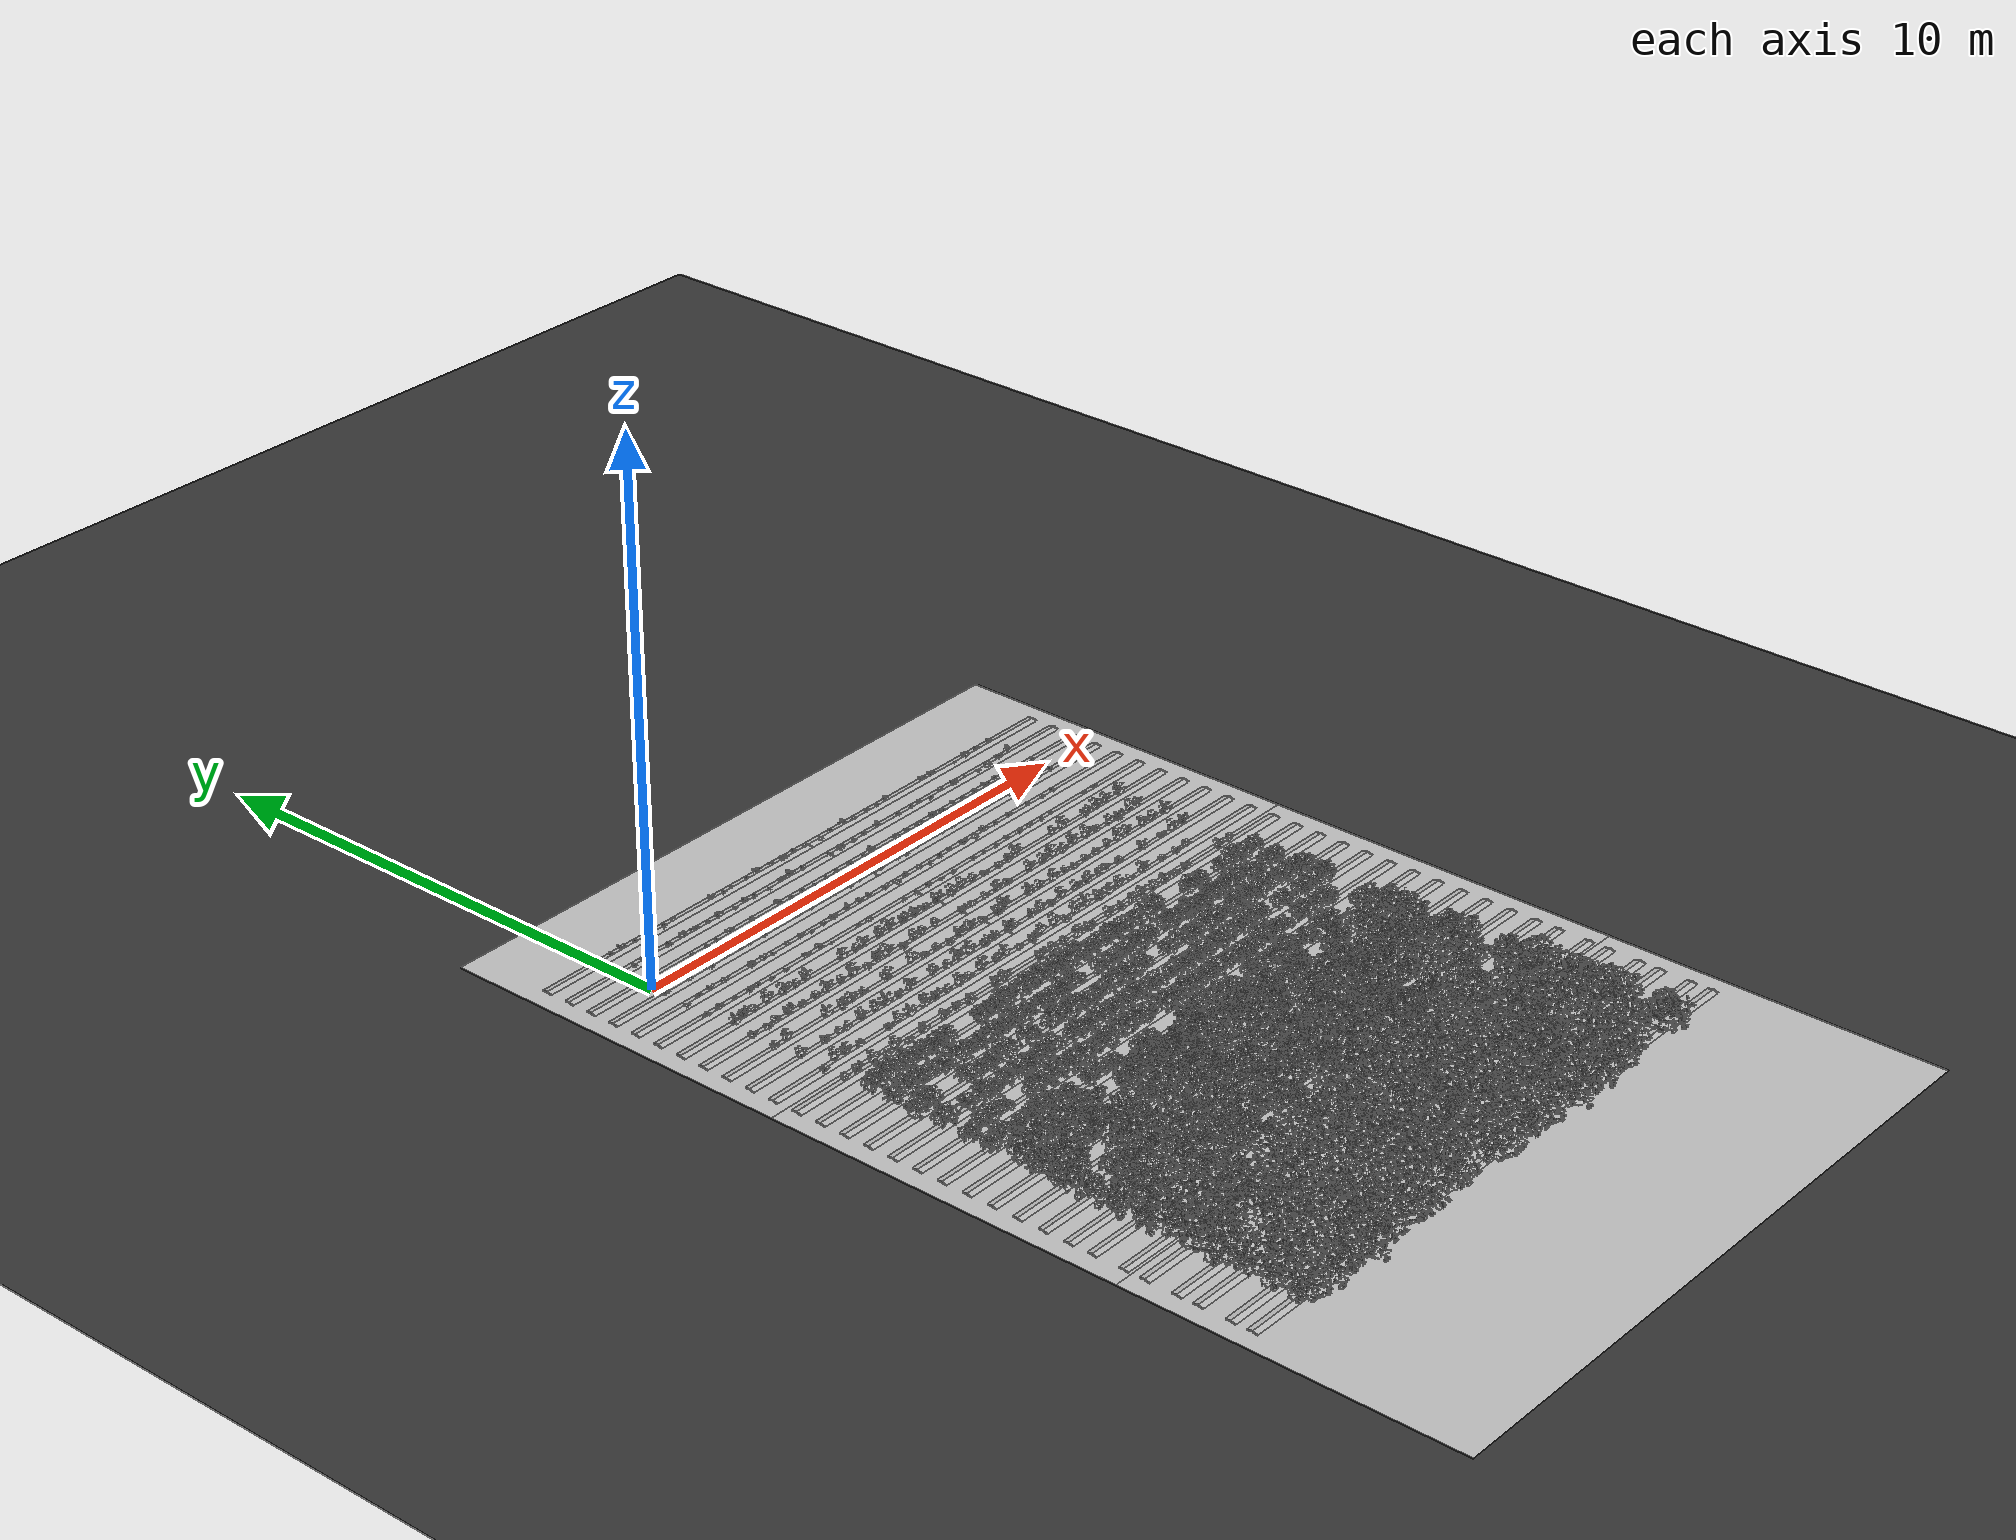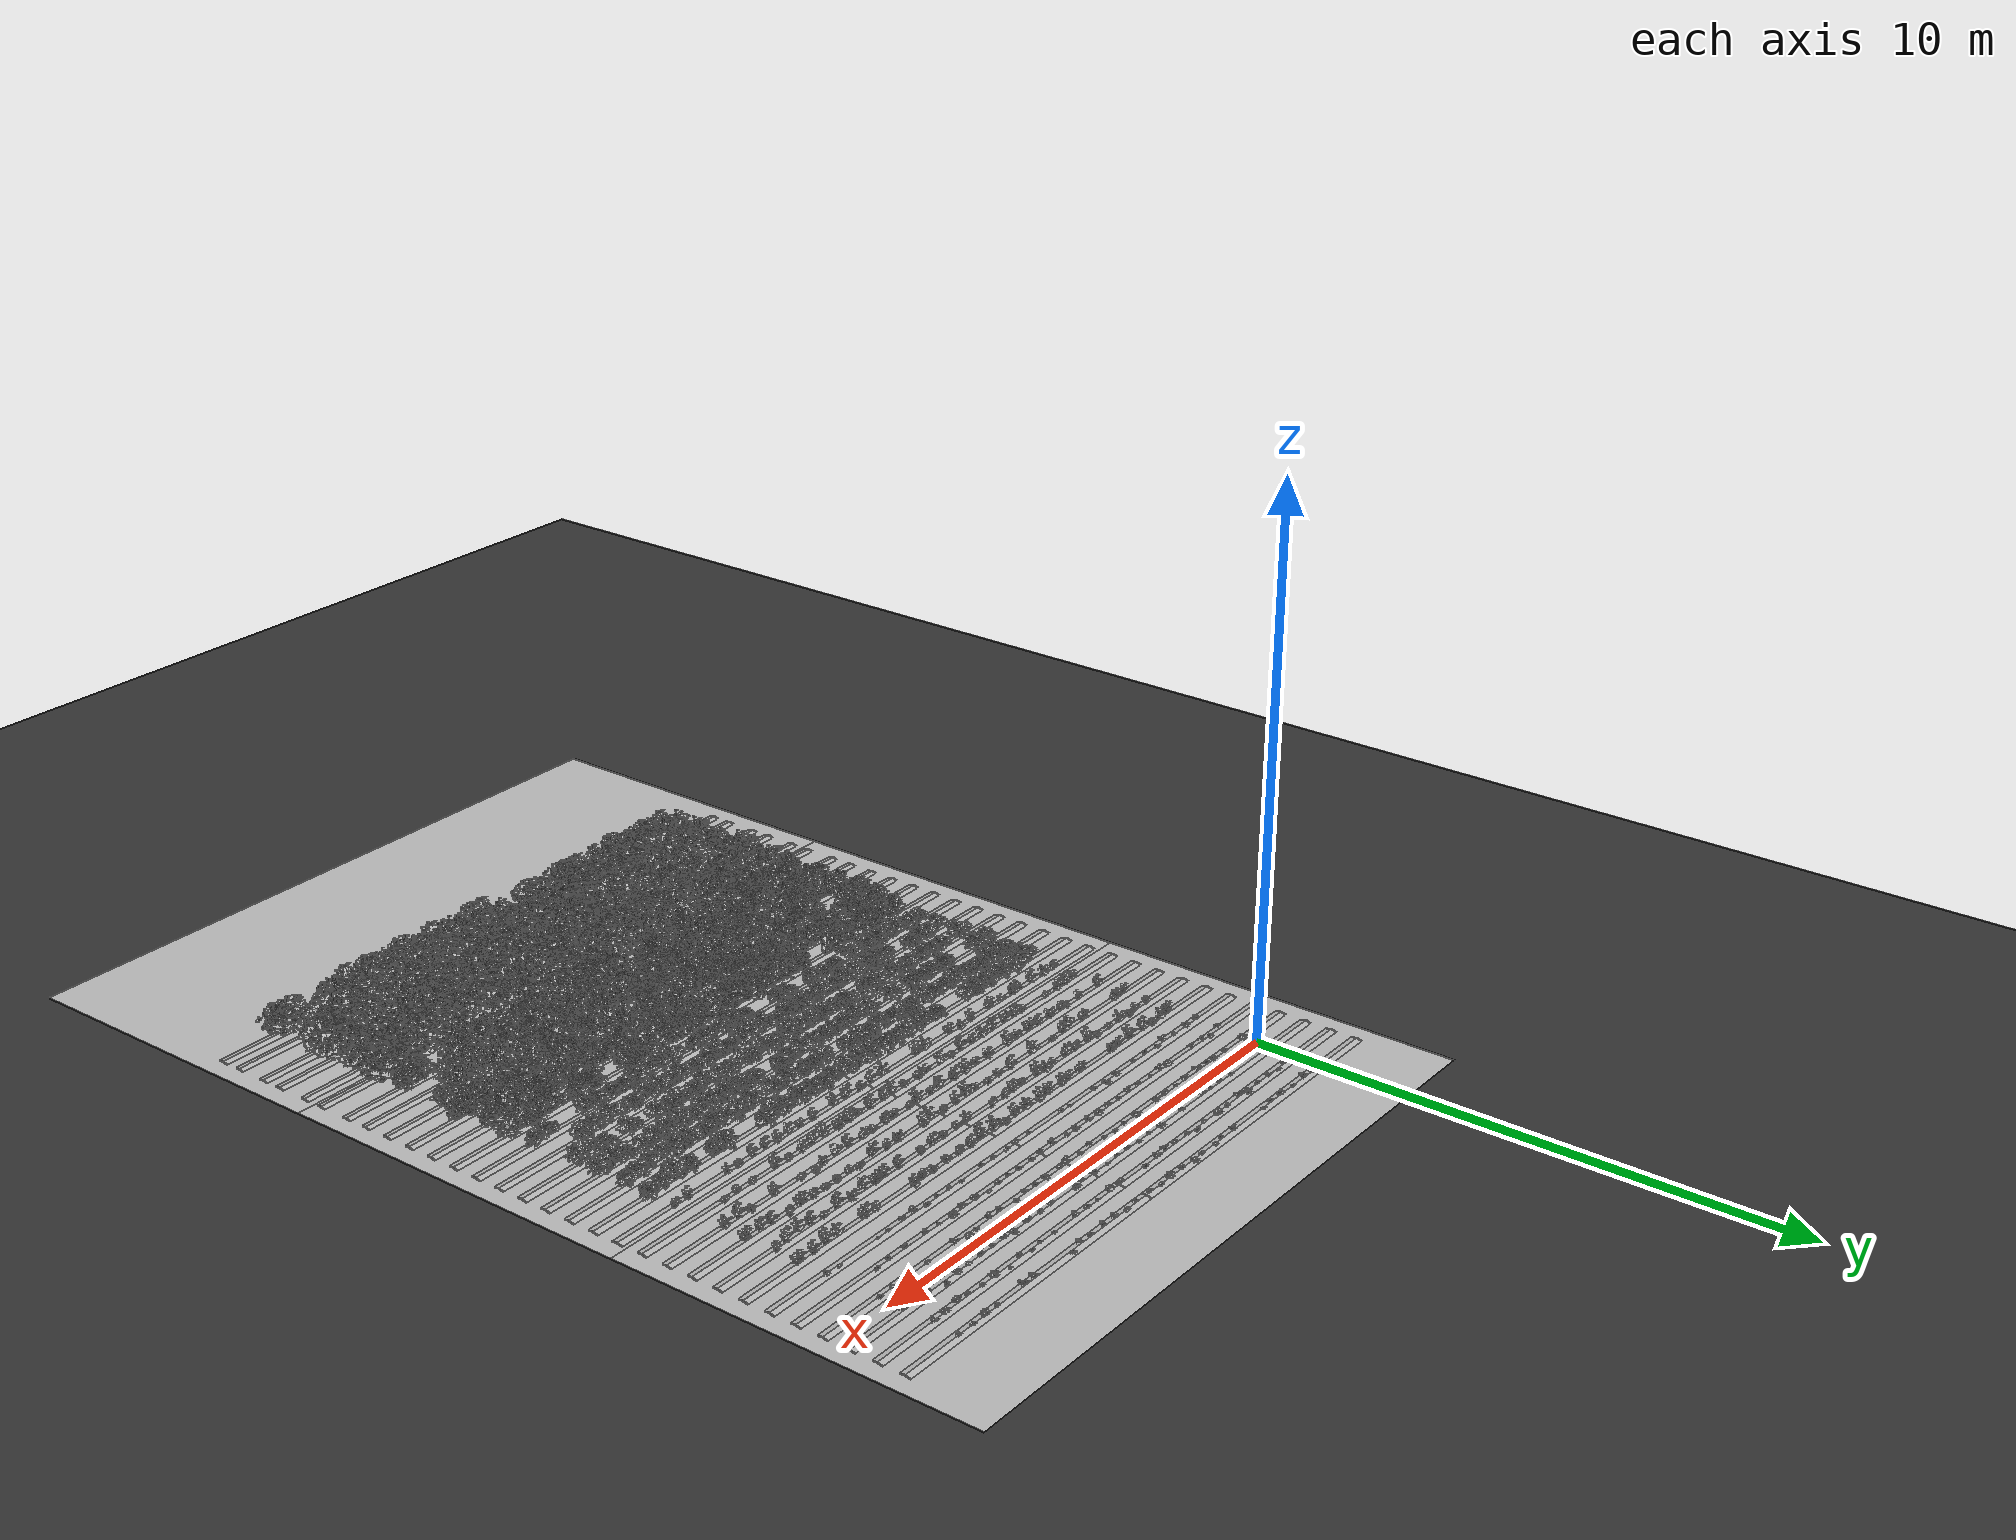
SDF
<sdf version="1.7">
 <world name="default">
  <light name="sun" type="directional">
   <pose>0 0 10 0 -0 0</pose>
   <diffuse>0.8 0.8 0.8 1</diffuse>
   <specular>0.2 0.2 0.2 1</specular>
   <attenuation>
    <range>1000</range>
    <constant>0.9</constant>
    <linear>0.01</linear>
    <quadratic>0.001</quadratic>
   </attenuation>
   <direction>-0.5 0.1 -0.9</direction>
   <spot><inner_angle>0</inner_angle><outer_angle>0</outer_angle><falloff>0</falloff></spot>
  </light>
  <model name="ground_plane">
   <static>1</static>
   <link name="link">
    <collision name="collision">
     <geometry><plane><normal>0 0 1</normal><size>100 100</size></plane></geometry>
     <surface>
      <contact><collide_bitmask>65535</collide_bitmask></contact>
      <friction><ode><mu>100</mu><mu2>50</mu2></ode></friction>
     </surface>
    </collision>
    <visual name="visual">
     <cast_shadows>0</cast_shadows>
     <geometry><plane><normal>0 0 1</normal><size>100 100</size></plane></geometry>
     <material>
      <ambient>0.2 0.2 0.2 1.0</ambient>
      <diffuse>0.2 0.2 0.2 1.0</diffuse>
      <specular>0.2 0.2 0.2 1.0</specular>
      <emissive>0.2 0.2 0.2 1.0</emissive>
     </material>
    </visual>
   </link>
  </model>
  <model name="ground">
   <pose>5 -0.5 0.01  3.141592654 0 0</pose>
   <static>true</static>
   <link name="body">
    <visual name="visual">
     <cast_shadows>0</cast_shadows>
     <geometry>
      <mesh><uri>file:///home/ifcosta/final_ws/src/cnn_line/worlds/models/ground.obj</uri></mesh>
     </geometry>
    </visual>
   </link>
  </model>
  <model name="ground_1">
   <pose>5 -7.4 0.01  3.1410592654 0 0</pose>
   <static>true</static>
   <link name="body">
    <visual name="visual">
     <cast_shadows>0</cast_shadows>
     <geometry>
      <mesh><uri>file:///home/ifcosta/final_ws/src/cnn_line/worlds/models/ground.obj</uri></mesh>
     </geometry>
    </visual>
   </link>
  </model>
  <model name="ground_2">
   <pose>5 -13.8 0.01  3.141592654 0 0</pose>
   <static>true</static>
   <link name="body">
    <visual name="visual">
     <cast_shadows>0</cast_shadows>
     <geometry>
      <mesh><uri>file:///home/ifcosta/final_ws/src/cnn_line/worlds/models/ground.obj</uri></mesh>
     </geometry>
    </visual>
   </link>
  </model>
  <model name="plt_0">
   <pose>-0.0155 -1.25 0.0139 0.0 0.0 0.71081</pose>
   <static>true</static>
   <link name="body">
    <visual name="visual">
     <geometry>
      <mesh><uri>file:///home/ifcosta/final_ws/src/cnn_line/worlds/models/plant2.obj</uri></mesh>
     </geometry>
    </visual>
   </link>
  </model>
  <model name="plt_10000">
   <pose>-0.0155 -4.25 0.0139 0.0 0.0 -0.20527</pose>
   <static>true</static>
   <link name="body">
    <visual name="visual">
     <geometry>
      <mesh><uri>file:///home/ifcosta/final_ws/src/cnn_line/worlds/models/plant11.obj</uri></mesh>
     </geometry>
    </visual>
   </link>
  </model>
  <model name="plt_20000">
   <pose>-0.0155 -7.25 0.0139 0.0 0.0 -1.8722</pose>
   <static>true</static>
   <link name="body">
    <visual name="visual">
     <geometry>
      <mesh><uri>file:///home/ifcosta/final_ws/src/cnn_line/worlds/models/plant20.obj</uri></mesh>
     </geometry>
    </visual>
   </link>
  </model>
  <model name="plt_30000">
   <pose>-0.0155 -10.3 0.0139 0.0 0.0 -0.073187</pose>
   <static>true</static>
   <link name="body">
    <visual name="visual">
     <geometry>
      <mesh><uri>file:///home/ifcosta/final_ws/src/cnn_line/worlds/models/plant34.obj</uri></mesh>
     </geometry>
    </visual>
   </link>
  </model>
  <model name="plt_40000">
   <pose>-0.0155 -13.3 0.0139 0.0 0.0 -0.48719</pose>
   <static>true</static>
   <link name="body">
    <visual name="visual">
     <geometry>
      <mesh><uri>file:///home/ifcosta/final_ws/src/cnn_line/worlds/models/plant37.obj</uri></mesh>
     </geometry>
    </visual>
   </link>
  </model>
  <model name="plt_1">
   <pose>0.29 -1.23 0.0123 0.0 0.0 1.4187</pose>
   <static>true</static>
   <link name="body">
    <visual name="visual">
     <geometry>
      <mesh><uri>file:///home/ifcosta/final_ws/src/cnn_line/worlds/models/plant2.obj</uri></mesh>
     </geometry>
    </visual>
   </link>
  </model>
  <model name="plt_10001">
   <pose>0.29 -4.23 0.0123 0.0 0.0 1.6509</pose>
   <static>true</static>
   <link name="body">
    <visual name="visual">
     <geometry>
      <mesh><uri>file:///home/ifcosta/final_ws/src/cnn_line/worlds/models/plant12.obj</uri></mesh>
     </geometry>
    </visual>
   </link>
  </model>
  <model name="plt_20001">
   <pose>0.29 -7.23 0.0123 0.0 0.0 0.9943</pose>
   <static>true</static>
   <link name="body">
    <visual name="visual">
     <geometry>
      <mesh><uri>file:///home/ifcosta/final_ws/src/cnn_line/worlds/models/plant21.obj</uri></mesh>
     </geometry>
    </visual>
   </link>
  </model>
  <model name="plt_30001">
   <pose>0.29 -10.2 0.0123 0.0 0.0 -0.051587</pose>
   <static>true</static>
   <link name="body">
    <visual name="visual">
     <geometry>
      <mesh><uri>file:///home/ifcosta/final_ws/src/cnn_line/worlds/models/plant36.obj</uri></mesh>
     </geometry>
    </visual>
   </link>
  </model>
  <model name="plt_40001">
   <pose>0.29 -13.2 0.0123 0.0 0.0 0.6554</pose>
   <static>true</static>
   <link name="body">
    <visual name="visual">
     <geometry>
      <mesh><uri>file:///home/ifcosta/final_ws/src/cnn_line/worlds/models/plant37.obj</uri></mesh>
     </geometry>
    </visual>
   </link>
  </model>
  <model name="plt_2">
   <pose>0.662 -1.25 0.0135 0.0 0.0 1.9066</pose>
   <static>true</static>
   <link name="body">
    <visual name="visual">
     <geometry>
      <mesh><uri>file:///home/ifcosta/final_ws/src/cnn_line/worlds/models/plant5.obj</uri></mesh>
     </geometry>
    </visual>
   </link>
  </model>
  <model name="plt_10002">
   <pose>0.662 -4.25 0.0135 0.0 0.0 -0.071589</pose>
   <static>true</static>
   <link name="body">
    <visual name="visual">
     <geometry>
      <mesh><uri>file:///home/ifcosta/final_ws/src/cnn_line/worlds/models/plant13.obj</uri></mesh>
     </geometry>
    </visual>
   </link>
  </model>
  <model name="plt_20002">
   <pose>0.662 -7.25 0.0135 0.0 0.0 -1.072</pose>
   <static>true</static>
   <link name="body">
    <visual name="visual">
     <geometry>
      <mesh><uri>file:///home/ifcosta/final_ws/src/cnn_line/worlds/models/plant20.obj</uri></mesh>
     </geometry>
    </visual>
   </link>
  </model>
  <model name="plt_30002">
   <pose>0.662 -10.3 0.0135 0.0 0.0 -0.3181</pose>
   <static>true</static>
   <link name="body">
    <visual name="visual">
     <geometry>
      <mesh><uri>file:///home/ifcosta/final_ws/src/cnn_line/worlds/models/plant33.obj</uri></mesh>
     </geometry>
    </visual>
   </link>
  </model>
  <model name="plt_40002">
   <pose>0.662 -13.3 0.0135 0.0 0.0 1.5998</pose>
   <static>true</static>
   <link name="body">
    <visual name="visual">
     <geometry>
      <mesh><uri>file:///home/ifcosta/final_ws/src/cnn_line/worlds/models/plant37.obj</uri></mesh>
     </geometry>
    </visual>
   </link>
  </model>
  <model name="plt_3">
   <pose>0.961 -1.27 0.0196 0.0 0.0 -0.54626</pose>
   <static>true</static>
   <link name="body">
    <visual name="visual">
     <geometry>
      <mesh><uri>file:///home/ifcosta/final_ws/src/cnn_line/worlds/models/plant3.obj</uri></mesh>
     </geometry>
    </visual>
   </link>
  </model>
  <model name="plt_10003">
   <pose>0.961 -4.27 0.0196 0.0 0.0 -1.2805</pose>
   <static>true</static>
   <link name="body">
    <visual name="visual">
     <geometry>
      <mesh><uri>file:///home/ifcosta/final_ws/src/cnn_line/worlds/models/plant10.obj</uri></mesh>
     </geometry>
    </visual>
   </link>
  </model>
  <model name="plt_20003">
   <pose>0.961 -7.27 0.0196 0.0 0.0 0.7189</pose>
   <static>true</static>
   <link name="body">
    <visual name="visual">
     <geometry>
      <mesh><uri>file:///home/ifcosta/final_ws/src/cnn_line/worlds/models/plant21.obj</uri></mesh>
     </geometry>
    </visual>
   </link>
  </model>
  <model name="plt_30003">
   <pose>0.961 -10.3 0.0196 0.0 0.0 0.10055</pose>
   <static>true</static>
   <link name="body">
    <visual name="visual">
     <geometry>
      <mesh><uri>file:///home/ifcosta/final_ws/src/cnn_line/worlds/models/plant34.obj</uri></mesh>
     </geometry>
    </visual>
   </link>
  </model>
  <model name="plt_40003">
   <pose>0.961 -13.3 0.0196 0.0 0.0 0.44064</pose>
   <static>true</static>
   <link name="body">
    <visual name="visual">
     <geometry>
      <mesh><uri>file:///home/ifcosta/final_ws/src/cnn_line/worlds/models/plant37.obj</uri></mesh>
     </geometry>
    </visual>
   </link>
  </model>
  <model name="plt_4">
   <pose>1.19 -1.24 0.012 0.0 0.0 -2.0811</pose>
   <static>true</static>
   <link name="body">
    <visual name="visual">
     <geometry>
      <mesh><uri>file:///home/ifcosta/final_ws/src/cnn_line/worlds/models/plant7.obj</uri></mesh>
     </geometry>
    </visual>
   </link>
  </model>
  <model name="plt_10004">
   <pose>1.19 -4.24 0.012 0.0 0.0 -0.21423</pose>
   <static>true</static>
   <link name="body">
    <visual name="visual">
     <geometry>
      <mesh><uri>file:///home/ifcosta/final_ws/src/cnn_line/worlds/models/plant13.obj</uri></mesh>
     </geometry>
    </visual>
   </link>
  </model>
  <model name="plt_20004">
   <pose>1.19 -7.24 0.012 0.0 0.0 0.95856</pose>
   <static>true</static>
   <link name="body">
    <visual name="visual">
     <geometry>
      <mesh><uri>file:///home/ifcosta/final_ws/src/cnn_line/worlds/models/plant22.obj</uri></mesh>
     </geometry>
    </visual>
   </link>
  </model>
  <model name="plt_30004">
   <pose>1.19 -10.2 0.012 0.0 0.0 -0.74742</pose>
   <static>true</static>
   <link name="body">
    <visual name="visual">
     <geometry>
      <mesh><uri>file:///home/ifcosta/final_ws/src/cnn_line/worlds/models/plant31.obj</uri></mesh>
     </geometry>
    </visual>
   </link>
  </model>
  <model name="plt_40004">
   <pose>1.19 -13.2 0.012 0.0 0.0 -0.44722</pose>
   <static>true</static>
   <link name="body">
    <visual name="visual">
     <geometry>
      <mesh><uri>file:///home/ifcosta/final_ws/src/cnn_line/worlds/models/plant37.obj</uri></mesh>
     </geometry>
    </visual>
   </link>
  </model>
  <model name="plt_5">
   <pose>1.48 -1.28 0.0138 0.0 0.0 0.26198</pose>
   <static>true</static>
   <link name="body">
    <visual name="visual">
     <geometry>
      <mesh><uri>file:///home/ifcosta/final_ws/src/cnn_line/worlds/models/plant6.obj</uri></mesh>
     </geometry>
    </visual>
   </link>
  </model>
  <model name="plt_10005">
   <pose>1.48 -4.28 0.0138 0.0 0.0 2.1689</pose>
   <static>true</static>
   <link name="body">
    <visual name="visual">
     <geometry>
      <mesh><uri>file:///home/ifcosta/final_ws/src/cnn_line/worlds/models/plant10.obj</uri></mesh>
     </geometry>
    </visual>
   </link>
  </model>
  <model name="plt_20005">
   <pose>1.48 -7.28 0.0138 0.0 0.0 1.5511</pose>
   <static>true</static>
   <link name="body">
    <visual name="visual">
     <geometry>
      <mesh><uri>file:///home/ifcosta/final_ws/src/cnn_line/worlds/models/plant21.obj</uri></mesh>
     </geometry>
    </visual>
   </link>
  </model>
  <model name="plt_30005">
   <pose>1.48 -10.3 0.0138 0.0 0.0 -0.058823</pose>
   <static>true</static>
   <link name="body">
    <visual name="visual">
     <geometry>
      <mesh><uri>file:///home/ifcosta/final_ws/src/cnn_line/worlds/models/plant36.obj</uri></mesh>
     </geometry>
    </visual>
   </link>
  </model>
  <model name="plt_40005">
   <pose>1.48 -13.3 0.0138 0.0 0.0 2.0321</pose>
   <static>true</static>
   <link name="body">
    <visual name="visual">
     <geometry>
      <mesh><uri>file:///home/ifcosta/final_ws/src/cnn_line/worlds/models/plant37.obj</uri></mesh>
     </geometry>
    </visual>
   </link>
  </model>
  <model name="plt_6">
   <pose>1.84 -1.27 0.0161 0.0 0.0 -0.82249</pose>
   <static>true</static>
   <link name="body">
    <visual name="visual">
     <geometry>
      <mesh><uri>file:///home/ifcosta/final_ws/src/cnn_line/worlds/models/plant4.obj</uri></mesh>
     </geometry>
    </visual>
   </link>
  </model>
  <model name="plt_10006">
   <pose>1.84 -4.27 0.0161 0.0 0.0 -0.95736</pose>
   <static>true</static>
   <link name="body">
    <visual name="visual">
     <geometry>
      <mesh><uri>file:///home/ifcosta/final_ws/src/cnn_line/worlds/models/plant12.obj</uri></mesh>
     </geometry>
    </visual>
   </link>
  </model>
  <model name="plt_20006">
   <pose>1.84 -7.27 0.0161 0.0 0.0 -1.0882</pose>
   <static>true</static>
   <link name="body">
    <visual name="visual">
     <geometry>
      <mesh><uri>file:///home/ifcosta/final_ws/src/cnn_line/worlds/models/plant20.obj</uri></mesh>
     </geometry>
    </visual>
   </link>
  </model>
  <model name="plt_30006">
   <pose>1.84 -10.3 0.0161 0.0 0.0 -0.92968</pose>
   <static>true</static>
   <link name="body">
    <visual name="visual">
     <geometry>
      <mesh><uri>file:///home/ifcosta/final_ws/src/cnn_line/worlds/models/plant36.obj</uri></mesh>
     </geometry>
    </visual>
   </link>
  </model>
  <model name="plt_40006">
   <pose>1.84 -13.3 0.0161 0.0 0.0 0.042525</pose>
   <static>true</static>
   <link name="body">
    <visual name="visual">
     <geometry>
      <mesh><uri>file:///home/ifcosta/final_ws/src/cnn_line/worlds/models/plant37.obj</uri></mesh>
     </geometry>
    </visual>
   </link>
  </model>
  <model name="plt_8">
   <pose>2.4 -1.24 0.0127 0.0 0.0 -0.70569</pose>
   <static>true</static>
   <link name="body">
    <visual name="visual">
     <geometry>
      <mesh><uri>file:///home/ifcosta/final_ws/src/cnn_line/worlds/models/plant2.obj</uri></mesh>
     </geometry>
    </visual>
   </link>
  </model>
  <model name="plt_10008">
   <pose>2.4 -4.24 0.0127 0.0 0.0 0.71833</pose>
   <static>true</static>
   <link name="body">
    <visual name="visual">
     <geometry>
      <mesh><uri>file:///home/ifcosta/final_ws/src/cnn_line/worlds/models/plant12.obj</uri></mesh>
     </geometry>
    </visual>
   </link>
  </model>
  <model name="plt_20008">
   <pose>2.4 -7.24 0.0127 0.0 0.0 0.013578</pose>
   <static>true</static>
   <link name="body">
    <visual name="visual">
     <geometry>
      <mesh><uri>file:///home/ifcosta/final_ws/src/cnn_line/worlds/models/plant20.obj</uri></mesh>
     </geometry>
    </visual>
   </link>
  </model>
  <model name="plt_30008">
   <pose>2.4 -10.2 0.0127 0.0 0.0 0.20575</pose>
   <static>true</static>
   <link name="body">
    <visual name="visual">
     <geometry>
      <mesh><uri>file:///home/ifcosta/final_ws/src/cnn_line/worlds/models/plant35.obj</uri></mesh>
     </geometry>
    </visual>
   </link>
  </model>
  <model name="plt_40008">
   <pose>2.4 -13.2 0.0127 0.0 0.0 -0.64506</pose>
   <static>true</static>
   <link name="body">
    <visual name="visual">
     <geometry>
      <mesh><uri>file:///home/ifcosta/final_ws/src/cnn_line/worlds/models/plant37.obj</uri></mesh>
     </geometry>
    </visual>
   </link>
  </model>
  <model name="plt_9">
   <pose>2.73 -1.2 0.0151 0.0 0.0 -0.49936</pose>
   <static>true</static>
   <link name="body">
    <visual name="visual">
     <geometry>
      <mesh><uri>file:///home/ifcosta/final_ws/src/cnn_line/worlds/models/plant2.obj</uri></mesh>
     </geometry>
    </visual>
   </link>
  </model>
  <model name="plt_10009">
   <pose>2.73 -4.2 0.0151 0.0 0.0 1.341</pose>
   <static>true</static>
   <link name="body">
    <visual name="visual">
     <geometry>
      <mesh><uri>file:///home/ifcosta/final_ws/src/cnn_line/worlds/models/plant11.obj</uri></mesh>
     </geometry>
    </visual>
   </link>
  </model>
  <model name="plt_20009">
   <pose>2.73 -7.2 0.0151 0.0 0.0 0.84642</pose>
   <static>true</static>
   <link name="body">
    <visual name="visual">
     <geometry>
      <mesh><uri>file:///home/ifcosta/final_ws/src/cnn_line/worlds/models/plant20.obj</uri></mesh>
     </geometry>
    </visual>
   </link>
  </model>
  <model name="plt_30009">
   <pose>2.73 -10.2 0.0151 0.0 0.0 -1.1172</pose>
   <static>true</static>
   <link name="body">
    <visual name="visual">
     <geometry>
      <mesh><uri>file:///home/ifcosta/final_ws/src/cnn_line/worlds/models/plant33.obj</uri></mesh>
     </geometry>
    </visual>
   </link>
  </model>
  <model name="plt_40009">
   <pose>2.73 -13.2 0.0151 0.0 0.0 -1.2915</pose>
   <static>true</static>
   <link name="body">
    <visual name="visual">
     <geometry>
      <mesh><uri>file:///home/ifcosta/final_ws/src/cnn_line/worlds/models/plant37.obj</uri></mesh>
     </geometry>
    </visual>
   </link>
  </model>
  <model name="plt_10">
   <pose>2.98 -1.27 0.0139 0.0 0.0 1.1967</pose>
   <static>true</static>
   <link name="body">
    <visual name="visual">
     <geometry>
      <mesh><uri>file:///home/ifcosta/final_ws/src/cnn_line/worlds/models/plant4.obj</uri></mesh>
     </geometry>
    </visual>
   </link>
  </model>
  <model name="plt_10010">
   <pose>2.98 -4.27 0.0139 0.0 0.0 -1.2602</pose>
   <static>true</static>
   <link name="body">
    <visual name="visual">
     <geometry>
      <mesh><uri>file:///home/ifcosta/final_ws/src/cnn_line/worlds/models/plant12.obj</uri></mesh>
     </geometry>
    </visual>
   </link>
  </model>
  <model name="plt_20010">
   <pose>2.98 -7.27 0.0139 0.0 0.0 -0.81675</pose>
   <static>true</static>
   <link name="body">
    <visual name="visual">
     <geometry>
      <mesh><uri>file:///home/ifcosta/final_ws/src/cnn_line/worlds/models/plant20.obj</uri></mesh>
     </geometry>
    </visual>
   </link>
  </model>
  <model name="plt_30010">
   <pose>2.98 -10.3 0.0139 0.0 0.0 -0.027045</pose>
   <static>true</static>
   <link name="body">
    <visual name="visual">
     <geometry>
      <mesh><uri>file:///home/ifcosta/final_ws/src/cnn_line/worlds/models/plant34.obj</uri></mesh>
     </geometry>
    </visual>
   </link>
  </model>
  <model name="plt_40010">
   <pose>2.98 -13.3 0.0139 0.0 0.0 1.1998</pose>
   <static>true</static>
   <link name="body">
    <visual name="visual">
     <geometry>
      <mesh><uri>file:///home/ifcosta/final_ws/src/cnn_line/worlds/models/plant37.obj</uri></mesh>
     </geometry>
    </visual>
   </link>
  </model>
  <model name="plt_12">
   <pose>3.68 -1.24 0.0168 0.0 0.0 -0.79892</pose>
   <static>true</static>
   <link name="body">
    <visual name="visual">
     <geometry>
      <mesh><uri>file:///home/ifcosta/final_ws/src/cnn_line/worlds/models/plant6.obj</uri></mesh>
     </geometry>
    </visual>
   </link>
  </model>
  <model name="plt_10012">
   <pose>3.68 -4.24 0.0168 0.0 0.0 1.4368</pose>
   <static>true</static>
   <link name="body">
    <visual name="visual">
     <geometry>
      <mesh><uri>file:///home/ifcosta/final_ws/src/cnn_line/worlds/models/plant13.obj</uri></mesh>
     </geometry>
    </visual>
   </link>
  </model>
  <model name="plt_20012">
   <pose>3.68 -7.24 0.0168 0.0 0.0 -1.1972</pose>
   <static>true</static>
   <link name="body">
    <visual name="visual">
     <geometry>
      <mesh><uri>file:///home/ifcosta/final_ws/src/cnn_line/worlds/models/plant20.obj</uri></mesh>
     </geometry>
    </visual>
   </link>
  </model>
  <model name="plt_30012">
   <pose>3.68 -10.2 0.0168 0.0 0.0 -0.72424</pose>
   <static>true</static>
   <link name="body">
    <visual name="visual">
     <geometry>
      <mesh><uri>file:///home/ifcosta/final_ws/src/cnn_line/worlds/models/plant31.obj</uri></mesh>
     </geometry>
    </visual>
   </link>
  </model>
  <model name="plt_40012">
   <pose>3.68 -13.2 0.0168 0.0 0.0 0.77402</pose>
   <static>true</static>
   <link name="body">
    <visual name="visual">
     <geometry>
      <mesh><uri>file:///home/ifcosta/final_ws/src/cnn_line/worlds/models/plant37.obj</uri></mesh>
     </geometry>
    </visual>
   </link>
  </model>
  <model name="plt_13">
   <pose>3.91 -1.25 0.0149 0.0 0.0 -1.5614</pose>
   <static>true</static>
   <link name="body">
    <visual name="visual">
     <geometry>
      <mesh><uri>file:///home/ifcosta/final_ws/src/cnn_line/worlds/models/plant5.obj</uri></mesh>
     </geometry>
    </visual>
   </link>
  </model>
  <model name="plt_10013">
   <pose>3.91 -4.25 0.0149 0.0 0.0 0.73426</pose>
   <static>true</static>
   <link name="body">
    <visual name="visual">
     <geometry>
      <mesh><uri>file:///home/ifcosta/final_ws/src/cnn_line/worlds/models/plant13.obj</uri></mesh>
     </geometry>
    </visual>
   </link>
  </model>
  <model name="plt_20013">
   <pose>3.91 -7.25 0.0149 0.0 0.0 -1.0897</pose>
   <static>true</static>
   <link name="body">
    <visual name="visual">
     <geometry>
      <mesh><uri>file:///home/ifcosta/final_ws/src/cnn_line/worlds/models/plant20.obj</uri></mesh>
     </geometry>
    </visual>
   </link>
  </model>
  <model name="plt_30013">
   <pose>3.91 -10.2 0.0149 0.0 0.0 -1.329</pose>
   <static>true</static>
   <link name="body">
    <visual name="visual">
     <geometry>
      <mesh><uri>file:///home/ifcosta/final_ws/src/cnn_line/worlds/models/plant33.obj</uri></mesh>
     </geometry>
    </visual>
   </link>
  </model>
  <model name="plt_40013">
   <pose>3.91 -13.2 0.0149 0.0 0.0 -1.9044</pose>
   <static>true</static>
   <link name="body">
    <visual name="visual">
     <geometry>
      <mesh><uri>file:///home/ifcosta/final_ws/src/cnn_line/worlds/models/plant37.obj</uri></mesh>
     </geometry>
    </visual>
   </link>
  </model>
  <model name="plt_16">
   <pose>4.79 -1.26 0.0151 0.0 0.0 -0.31027</pose>
   <static>true</static>
   <link name="body">
    <visual name="visual">
     <geometry>
      <mesh><uri>file:///home/ifcosta/final_ws/src/cnn_line/worlds/models/plant6.obj</uri></mesh>
     </geometry>
    </visual>
   </link>
  </model>
  <model name="plt_10016">
   <pose>4.79 -4.26 0.0151 0.0 0.0 1.4062</pose>
   <static>true</static>
   <link name="body">
    <visual name="visual">
     <geometry>
      <mesh><uri>file:///home/ifcosta/final_ws/src/cnn_line/worlds/models/plant13.obj</uri></mesh>
     </geometry>
    </visual>
   </link>
  </model>
  <model name="plt_20016">
   <pose>4.79 -7.26 0.0151 0.0 0.0 -0.2023</pose>
   <static>true</static>
   <link name="body">
    <visual name="visual">
     <geometry>
      <mesh><uri>file:///home/ifcosta/final_ws/src/cnn_line/worlds/models/plant20.obj</uri></mesh>
     </geometry>
    </visual>
   </link>
  </model>
  <model name="plt_30016">
   <pose>4.79 -10.3 0.0151 0.0 0.0 0.59571</pose>
   <static>true</static>
   <link name="body">
    <visual name="visual">
     <geometry>
      <mesh><uri>file:///home/ifcosta/final_ws/src/cnn_line/worlds/models/plant36.obj</uri></mesh>
     </geometry>
    </visual>
   </link>
  </model>
  <model name="plt_40016">
   <pose>4.79 -13.3 0.0151 0.0 0.0 -0.58913</pose>
   <static>true</static>
   <link name="body">
    <visual name="visual">
     <geometry>
      <mesh><uri>file:///home/ifcosta/final_ws/src/cnn_line/worlds/models/plant37.obj</uri></mesh>
     </geometry>
    </visual>
   </link>
  </model>
  <model name="plt_17">
   <pose>5.1 -1.27 0.0129 0.0 0.0 -1.016</pose>
   <static>true</static>
   <link name="body">
    <visual name="visual">
     <geometry>
      <mesh><uri>file:///home/ifcosta/final_ws/src/cnn_line/worlds/models/plant4.obj</uri></mesh>
     </geometry>
    </visual>
   </link>
  </model>
  <model name="plt_10017">
   <pose>5.1 -4.27 0.0129 0.0 0.0 0.11031</pose>
   <static>true</static>
   <link name="body">
    <visual name="visual">
     <geometry>
      <mesh><uri>file:///home/ifcosta/final_ws/src/cnn_line/worlds/models/plant12.obj</uri></mesh>
     </geometry>
    </visual>
   </link>
  </model>
  <model name="plt_20017">
   <pose>5.1 -7.27 0.0129 0.0 0.0 1.2066</pose>
   <static>true</static>
   <link name="body">
    <visual name="visual">
     <geometry>
      <mesh><uri>file:///home/ifcosta/final_ws/src/cnn_line/worlds/models/plant22.obj</uri></mesh>
     </geometry>
    </visual>
   </link>
  </model>
  <model name="plt_30017">
   <pose>5.1 -10.3 0.0129 0.0 0.0 0.31238</pose>
   <static>true</static>
   <link name="body">
    <visual name="visual">
     <geometry>
      <mesh><uri>file:///home/ifcosta/final_ws/src/cnn_line/worlds/models/plant33.obj</uri></mesh>
     </geometry>
    </visual>
   </link>
  </model>
  <model name="plt_40017">
   <pose>5.1 -13.3 0.0129 0.0 0.0 -1.0196</pose>
   <static>true</static>
   <link name="body">
    <visual name="visual">
     <geometry>
      <mesh><uri>file:///home/ifcosta/final_ws/src/cnn_line/worlds/models/plant37.obj</uri></mesh>
     </geometry>
    </visual>
   </link>
  </model>
  <model name="plt_18">
   <pose>5.41 -1.24 0.0167 0.0 0.0 1.5161</pose>
   <static>true</static>
   <link name="body">
    <visual name="visual">
     <geometry>
      <mesh><uri>file:///home/ifcosta/final_ws/src/cnn_line/worlds/models/plant7.obj</uri></mesh>
     </geometry>
    </visual>
   </link>
  </model>
  <model name="plt_10018">
   <pose>5.41 -4.24 0.0167 0.0 0.0 0.10898</pose>
   <static>true</static>
   <link name="body">
    <visual name="visual">
     <geometry>
      <mesh><uri>file:///home/ifcosta/final_ws/src/cnn_line/worlds/models/plant11.obj</uri></mesh>
     </geometry>
    </visual>
   </link>
  </model>
  <model name="plt_20018">
   <pose>5.41 -7.24 0.0167 0.0 0.0 0.76993</pose>
   <static>true</static>
   <link name="body">
    <visual name="visual">
     <geometry>
      <mesh><uri>file:///home/ifcosta/final_ws/src/cnn_line/worlds/models/plant21.obj</uri></mesh>
     </geometry>
    </visual>
   </link>
  </model>
  <model name="plt_30018">
   <pose>5.41 -10.2 0.0167 0.0 0.0 -0.31577</pose>
   <static>true</static>
   <link name="body">
    <visual name="visual">
     <geometry>
      <mesh><uri>file:///home/ifcosta/final_ws/src/cnn_line/worlds/models/plant30.obj</uri></mesh>
     </geometry>
    </visual>
   </link>
  </model>
  <model name="plt_40018">
   <pose>5.41 -13.2 0.0167 0.0 0.0 0.37927</pose>
   <static>true</static>
   <link name="body">
    <visual name="visual">
     <geometry>
      <mesh><uri>file:///home/ifcosta/final_ws/src/cnn_line/worlds/models/plant37.obj</uri></mesh>
     </geometry>
    </visual>
   </link>
  </model>
  <model name="plt_19">
   <pose>5.73 -1.27 0.012 0.0 0.0 2.2171</pose>
   <static>true</static>
   <link name="body">
    <visual name="visual">
     <geometry>
      <mesh><uri>file:///home/ifcosta/final_ws/src/cnn_line/worlds/models/plant4.obj</uri></mesh>
     </geometry>
    </visual>
   </link>
  </model>
  <model name="plt_10019">
   <pose>5.73 -4.27 0.012 0.0 0.0 -0.63378</pose>
   <static>true</static>
   <link name="body">
    <visual name="visual">
     <geometry>
      <mesh><uri>file:///home/ifcosta/final_ws/src/cnn_line/worlds/models/plant13.obj</uri></mesh>
     </geometry>
    </visual>
   </link>
  </model>
  <model name="plt_20019">
   <pose>5.73 -7.27 0.012 0.0 0.0 0.46287</pose>
   <static>true</static>
   <link name="body">
    <visual name="visual">
     <geometry>
      <mesh><uri>file:///home/ifcosta/final_ws/src/cnn_line/worlds/models/plant21.obj</uri></mesh>
     </geometry>
    </visual>
   </link>
  </model>
  <model name="plt_30019">
   <pose>5.73 -10.3 0.012 0.0 0.0 -0.173</pose>
   <static>true</static>
   <link name="body">
    <visual name="visual">
     <geometry>
      <mesh><uri>file:///home/ifcosta/final_ws/src/cnn_line/worlds/models/plant34.obj</uri></mesh>
     </geometry>
    </visual>
   </link>
  </model>
  <model name="plt_40019">
   <pose>5.73 -13.3 0.012 0.0 0.0 0.32636</pose>
   <static>true</static>
   <link name="body">
    <visual name="visual">
     <geometry>
      <mesh><uri>file:///home/ifcosta/final_ws/src/cnn_line/worlds/models/plant37.obj</uri></mesh>
     </geometry>
    </visual>
   </link>
  </model>
  <model name="plt_20">
   <pose>6.03 -1.28 0.0152 0.0 0.0 0.20169</pose>
   <static>true</static>
   <link name="body">
    <visual name="visual">
     <geometry>
      <mesh><uri>file:///home/ifcosta/final_ws/src/cnn_line/worlds/models/plant6.obj</uri></mesh>
     </geometry>
    </visual>
   </link>
  </model>
  <model name="plt_10020">
   <pose>6.03 -4.28 0.0152 0.0 0.0 1.1343</pose>
   <static>true</static>
   <link name="body">
    <visual name="visual">
     <geometry>
      <mesh><uri>file:///home/ifcosta/final_ws/src/cnn_line/worlds/models/plant12.obj</uri></mesh>
     </geometry>
    </visual>
   </link>
  </model>
  <model name="plt_20020">
   <pose>6.03 -7.28 0.0152 0.0 0.0 0.29218</pose>
   <static>true</static>
   <link name="body">
    <visual name="visual">
     <geometry>
      <mesh><uri>file:///home/ifcosta/final_ws/src/cnn_line/worlds/models/plant20.obj</uri></mesh>
     </geometry>
    </visual>
   </link>
  </model>
  <model name="plt_30020">
   <pose>6.03 -10.3 0.0152 0.0 0.0 -0.27084</pose>
   <static>true</static>
   <link name="body">
    <visual name="visual">
     <geometry>
      <mesh><uri>file:///home/ifcosta/final_ws/src/cnn_line/worlds/models/plant36.obj</uri></mesh>
     </geometry>
    </visual>
   </link>
  </model>
  <model name="plt_40020">
   <pose>6.03 -13.3 0.0152 0.0 0.0 -0.56396</pose>
   <static>true</static>
   <link name="body">
    <visual name="visual">
     <geometry>
      <mesh><uri>file:///home/ifcosta/final_ws/src/cnn_line/worlds/models/plant37.obj</uri></mesh>
     </geometry>
    </visual>
   </link>
  </model>
  <model name="plt_22">
   <pose>6.61 -1.23 0.0153 0.0 0.0 1.0452</pose>
   <static>true</static>
   <link name="body">
    <visual name="visual">
     <geometry>
      <mesh><uri>file:///home/ifcosta/final_ws/src/cnn_line/worlds/models/plant6.obj</uri></mesh>
     </geometry>
    </visual>
   </link>
  </model>
  <model name="plt_10022">
   <pose>6.61 -4.23 0.0153 0.0 0.0 0.51671</pose>
   <static>true</static>
   <link name="body">
    <visual name="visual">
     <geometry>
      <mesh><uri>file:///home/ifcosta/final_ws/src/cnn_line/worlds/models/plant12.obj</uri></mesh>
     </geometry>
    </visual>
   </link>
  </model>
  <model name="plt_20022">
   <pose>6.61 -7.23 0.0153 0.0 0.0 0.67324</pose>
   <static>true</static>
   <link name="body">
    <visual name="visual">
     <geometry>
      <mesh><uri>file:///home/ifcosta/final_ws/src/cnn_line/worlds/models/plant22.obj</uri></mesh>
     </geometry>
    </visual>
   </link>
  </model>
  <model name="plt_30022">
   <pose>6.61 -10.2 0.0153 0.0 0.0 -0.57249</pose>
   <static>true</static>
   <link name="body">
    <visual name="visual">
     <geometry>
      <mesh><uri>file:///home/ifcosta/final_ws/src/cnn_line/worlds/models/plant36.obj</uri></mesh>
     </geometry>
    </visual>
   </link>
  </model>
  <model name="plt_40022">
   <pose>6.61 -13.2 0.0153 0.0 0.0 1.1242</pose>
   <static>true</static>
   <link name="body">
    <visual name="visual">
     <geometry>
      <mesh><uri>file:///home/ifcosta/final_ws/src/cnn_line/worlds/models/plant37.obj</uri></mesh>
     </geometry>
    </visual>
   </link>
  </model>
  <model name="plt_23">
   <pose>6.89 -1.26 0.0155 0.0 0.0 0.58323</pose>
   <static>true</static>
   <link name="body">
    <visual name="visual">
     <geometry>
      <mesh><uri>file:///home/ifcosta/final_ws/src/cnn_line/worlds/models/plant4.obj</uri></mesh>
     </geometry>
    </visual>
   </link>
  </model>
  <model name="plt_10023">
   <pose>6.89 -4.26 0.0155 0.0 0.0 -1.4487</pose>
   <static>true</static>
   <link name="body">
    <visual name="visual">
     <geometry>
      <mesh><uri>file:///home/ifcosta/final_ws/src/cnn_line/worlds/models/plant11.obj</uri></mesh>
     </geometry>
    </visual>
   </link>
  </model>
  <model name="plt_20023">
   <pose>6.89 -7.26 0.0155 0.0 0.0 -0.047818</pose>
   <static>true</static>
   <link name="body">
    <visual name="visual">
     <geometry>
      <mesh><uri>file:///home/ifcosta/final_ws/src/cnn_line/worlds/models/plant21.obj</uri></mesh>
     </geometry>
    </visual>
   </link>
  </model>
  <model name="plt_30023">
   <pose>6.89 -10.3 0.0155 0.0 0.0 -0.2691</pose>
   <static>true</static>
   <link name="body">
    <visual name="visual">
     <geometry>
      <mesh><uri>file:///home/ifcosta/final_ws/src/cnn_line/worlds/models/plant31.obj</uri></mesh>
     </geometry>
    </visual>
   </link>
  </model>
  <model name="plt_40023">
   <pose>6.89 -13.3 0.0155 0.0 0.0 1.9247</pose>
   <static>true</static>
   <link name="body">
    <visual name="visual">
     <geometry>
      <mesh><uri>file:///home/ifcosta/final_ws/src/cnn_line/worlds/models/plant37.obj</uri></mesh>
     </geometry>
    </visual>
   </link>
  </model>
  <model name="plt_24">
   <pose>7.18 -1.26 0.0155 0.0 0.0 -0.44791</pose>
   <static>true</static>
   <link name="body">
    <visual name="visual">
     <geometry>
      <mesh><uri>file:///home/ifcosta/final_ws/src/cnn_line/worlds/models/plant6.obj</uri></mesh>
     </geometry>
    </visual>
   </link>
  </model>
  <model name="plt_10024">
   <pose>7.18 -4.26 0.0155 0.0 0.0 -0.59258</pose>
   <static>true</static>
   <link name="body">
    <visual name="visual">
     <geometry>
      <mesh><uri>file:///home/ifcosta/final_ws/src/cnn_line/worlds/models/plant12.obj</uri></mesh>
     </geometry>
    </visual>
   </link>
  </model>
  <model name="plt_20024">
   <pose>7.18 -7.26 0.0155 0.0 0.0 0.093608</pose>
   <static>true</static>
   <link name="body">
    <visual name="visual">
     <geometry>
      <mesh><uri>file:///home/ifcosta/final_ws/src/cnn_line/worlds/models/plant21.obj</uri></mesh>
     </geometry>
    </visual>
   </link>
  </model>
  <model name="plt_30024">
   <pose>7.18 -10.3 0.0155 0.0 0.0 -0.92946</pose>
   <static>true</static>
   <link name="body">
    <visual name="visual">
     <geometry>
      <mesh><uri>file:///home/ifcosta/final_ws/src/cnn_line/worlds/models/plant33.obj</uri></mesh>
     </geometry>
    </visual>
   </link>
  </model>
  <model name="plt_40024">
   <pose>7.18 -13.3 0.0155 0.0 0.0 0.82469</pose>
   <static>true</static>
   <link name="body">
    <visual name="visual">
     <geometry>
      <mesh><uri>file:///home/ifcosta/final_ws/src/cnn_line/worlds/models/plant37.obj</uri></mesh>
     </geometry>
    </visual>
   </link>
  </model>
  <model name="plt_25">
   <pose>7.49 -1.22 0.0176 0.0 0.0 -0.2236</pose>
   <static>true</static>
   <link name="body">
    <visual name="visual">
     <geometry>
      <mesh><uri>file:///home/ifcosta/final_ws/src/cnn_line/worlds/models/plant5.obj</uri></mesh>
     </geometry>
    </visual>
   </link>
  </model>
  <model name="plt_10025">
   <pose>7.49 -4.22 0.0176 0.0 0.0 0.74149</pose>
   <static>true</static>
   <link name="body">
    <visual name="visual">
     <geometry>
      <mesh><uri>file:///home/ifcosta/final_ws/src/cnn_line/worlds/models/plant12.obj</uri></mesh>
     </geometry>
    </visual>
   </link>
  </model>
  <model name="plt_20025">
   <pose>7.49 -7.22 0.0176 0.0 0.0 0.53895</pose>
   <static>true</static>
   <link name="body">
    <visual name="visual">
     <geometry>
      <mesh><uri>file:///home/ifcosta/final_ws/src/cnn_line/worlds/models/plant22.obj</uri></mesh>
     </geometry>
    </visual>
   </link>
  </model>
  <model name="plt_30025">
   <pose>7.49 -10.2 0.0176 0.0 0.0 0.76057</pose>
   <static>true</static>
   <link name="body">
    <visual name="visual">
     <geometry>
      <mesh><uri>file:///home/ifcosta/final_ws/src/cnn_line/worlds/models/plant33.obj</uri></mesh>
     </geometry>
    </visual>
   </link>
  </model>
  <model name="plt_40025">
   <pose>7.49 -13.2 0.0176 0.0 0.0 -0.050242</pose>
   <static>true</static>
   <link name="body">
    <visual name="visual">
     <geometry>
      <mesh><uri>file:///home/ifcosta/final_ws/src/cnn_line/worlds/models/plant37.obj</uri></mesh>
     </geometry>
    </visual>
   </link>
  </model>
  <model name="plt_26">
   <pose>7.75 -1.27 0.0115 0.0 0.0 0.39319</pose>
   <static>true</static>
   <link name="body">
    <visual name="visual">
     <geometry>
      <mesh><uri>file:///home/ifcosta/final_ws/src/cnn_line/worlds/models/plant3.obj</uri></mesh>
     </geometry>
    </visual>
   </link>
  </model>
  <model name="plt_10026">
   <pose>7.75 -4.27 0.0115 0.0 0.0 -0.22559</pose>
   <static>true</static>
   <link name="body">
    <visual name="visual">
     <geometry>
      <mesh><uri>file:///home/ifcosta/final_ws/src/cnn_line/worlds/models/plant12.obj</uri></mesh>
     </geometry>
    </visual>
   </link>
  </model>
  <model name="plt_20026">
   <pose>7.75 -7.27 0.0115 0.0 0.0 0.17191</pose>
   <static>true</static>
   <link name="body">
    <visual name="visual">
     <geometry>
      <mesh><uri>file:///home/ifcosta/final_ws/src/cnn_line/worlds/models/plant20.obj</uri></mesh>
     </geometry>
    </visual>
   </link>
  </model>
  <model name="plt_30026">
   <pose>7.75 -10.3 0.0115 0.0 0.0 -1.0217</pose>
   <static>true</static>
   <link name="body">
    <visual name="visual">
     <geometry>
      <mesh><uri>file:///home/ifcosta/final_ws/src/cnn_line/worlds/models/plant35.obj</uri></mesh>
     </geometry>
    </visual>
   </link>
  </model>
  <model name="plt_40026">
   <pose>7.75 -13.3 0.0115 0.0 0.0 1.6232</pose>
   <static>true</static>
   <link name="body">
    <visual name="visual">
     <geometry>
      <mesh><uri>file:///home/ifcosta/final_ws/src/cnn_line/worlds/models/plant37.obj</uri></mesh>
     </geometry>
    </visual>
   </link>
  </model>
  <model name="plt_27">
   <pose>8.06 -1.26 0.0198 0.0 0.0 -0.53112</pose>
   <static>true</static>
   <link name="body">
    <visual name="visual">
     <geometry>
      <mesh><uri>file:///home/ifcosta/final_ws/src/cnn_line/worlds/models/plant1.obj</uri></mesh>
     </geometry>
    </visual>
   </link>
  </model>
  <model name="plt_10027">
   <pose>8.06 -4.26 0.0198 0.0 0.0 0.52255</pose>
   <static>true</static>
   <link name="body">
    <visual name="visual">
     <geometry>
      <mesh><uri>file:///home/ifcosta/final_ws/src/cnn_line/worlds/models/plant12.obj</uri></mesh>
     </geometry>
    </visual>
   </link>
  </model>
  <model name="plt_20027">
   <pose>8.06 -7.26 0.0198 0.0 0.0 0.43862</pose>
   <static>true</static>
   <link name="body">
    <visual name="visual">
     <geometry>
      <mesh><uri>file:///home/ifcosta/final_ws/src/cnn_line/worlds/models/plant20.obj</uri></mesh>
     </geometry>
    </visual>
   </link>
  </model>
  <model name="plt_30027">
   <pose>8.06 -10.3 0.0198 0.0 0.0 0.20957</pose>
   <static>true</static>
   <link name="body">
    <visual name="visual">
     <geometry>
      <mesh><uri>file:///home/ifcosta/final_ws/src/cnn_line/worlds/models/plant31.obj</uri></mesh>
     </geometry>
    </visual>
   </link>
  </model>
  <model name="plt_40027">
   <pose>8.06 -13.3 0.0198 0.0 0.0 -0.42559</pose>
   <static>true</static>
   <link name="body">
    <visual name="visual">
     <geometry>
      <mesh><uri>file:///home/ifcosta/final_ws/src/cnn_line/worlds/models/plant37.obj</uri></mesh>
     </geometry>
    </visual>
   </link>
  </model>
  <model name="plt_28">
   <pose>8.4 -1.25 0.0158 0.0 0.0 0.4809</pose>
   <static>true</static>
   <link name="body">
    <visual name="visual">
     <geometry>
      <mesh><uri>file:///home/ifcosta/final_ws/src/cnn_line/worlds/models/plant6.obj</uri></mesh>
     </geometry>
    </visual>
   </link>
  </model>
  <model name="plt_10028">
   <pose>8.4 -4.25 0.0158 0.0 0.0 0.34888</pose>
   <static>true</static>
   <link name="body">
    <visual name="visual">
     <geometry>
      <mesh><uri>file:///home/ifcosta/final_ws/src/cnn_line/worlds/models/plant10.obj</uri></mesh>
     </geometry>
    </visual>
   </link>
  </model>
  <model name="plt_20028">
   <pose>8.4 -7.25 0.0158 0.0 0.0 -0.079509</pose>
   <static>true</static>
   <link name="body">
    <visual name="visual">
     <geometry>
      <mesh><uri>file:///home/ifcosta/final_ws/src/cnn_line/worlds/models/plant21.obj</uri></mesh>
     </geometry>
    </visual>
   </link>
  </model>
  <model name="plt_30028">
   <pose>8.4 -10.2 0.0158 0.0 0.0 1.0751</pose>
   <static>true</static>
   <link name="body">
    <visual name="visual">
     <geometry>
      <mesh><uri>file:///home/ifcosta/final_ws/src/cnn_line/worlds/models/plant34.obj</uri></mesh>
     </geometry>
    </visual>
   </link>
  </model>
  <model name="plt_40028">
   <pose>8.4 -13.2 0.0158 0.0 0.0 0.23405</pose>
   <static>true</static>
   <link name="body">
    <visual name="visual">
     <geometry>
      <mesh><uri>file:///home/ifcosta/final_ws/src/cnn_line/worlds/models/plant37.obj</uri></mesh>
     </geometry>
    </visual>
   </link>
  </model>
  <model name="plt_29">
   <pose>8.66 -1.24 0.0158 0.0 0.0 -1.4316</pose>
   <static>true</static>
   <link name="body">
    <visual name="visual">
     <geometry>
      <mesh><uri>file:///home/ifcosta/final_ws/src/cnn_line/worlds/models/plant4.obj</uri></mesh>
     </geometry>
    </visual>
   </link>
  </model>
  <model name="plt_10029">
   <pose>8.66 -4.24 0.0158 0.0 0.0 1.1464</pose>
   <static>true</static>
   <link name="body">
    <visual name="visual">
     <geometry>
      <mesh><uri>file:///home/ifcosta/final_ws/src/cnn_line/worlds/models/plant11.obj</uri></mesh>
     </geometry>
    </visual>
   </link>
  </model>
  <model name="plt_20029">
   <pose>8.66 -7.24 0.0158 0.0 0.0 -0.49195</pose>
   <static>true</static>
   <link name="body">
    <visual name="visual">
     <geometry>
      <mesh><uri>file:///home/ifcosta/final_ws/src/cnn_line/worlds/models/plant22.obj</uri></mesh>
     </geometry>
    </visual>
   </link>
  </model>
  <model name="plt_30029">
   <pose>8.66 -10.2 0.0158 0.0 0.0 1.8413</pose>
   <static>true</static>
   <link name="body">
    <visual name="visual">
     <geometry>
      <mesh><uri>file:///home/ifcosta/final_ws/src/cnn_line/worlds/models/plant33.obj</uri></mesh>
     </geometry>
    </visual>
   </link>
  </model>
  <model name="plt_40029">
   <pose>8.66 -13.2 0.0158 0.0 0.0 0.44361</pose>
   <static>true</static>
   <link name="body">
    <visual name="visual">
     <geometry>
      <mesh><uri>file:///home/ifcosta/final_ws/src/cnn_line/worlds/models/plant37.obj</uri></mesh>
     </geometry>
    </visual>
   </link>
  </model>
  <model name="plt_32">
   <pose>9.61 -1.22 0.014 0.0 0.0 1.3536</pose>
   <static>true</static>
   <link name="body">
    <visual name="visual">
     <geometry>
      <mesh><uri>file:///home/ifcosta/final_ws/src/cnn_line/worlds/models/plant6.obj</uri></mesh>
     </geometry>
    </visual>
   </link>
  </model>
  <model name="plt_10032">
   <pose>9.61 -4.22 0.014 0.0 0.0 0.66716</pose>
   <static>true</static>
   <link name="body">
    <visual name="visual">
     <geometry>
      <mesh><uri>file:///home/ifcosta/final_ws/src/cnn_line/worlds/models/plant12.obj</uri></mesh>
     </geometry>
    </visual>
   </link>
  </model>
  <model name="plt_20032">
   <pose>9.61 -7.22 0.014 0.0 0.0 -0.44802</pose>
   <static>true</static>
   <link name="body">
    <visual name="visual">
     <geometry>
      <mesh><uri>file:///home/ifcosta/final_ws/src/cnn_line/worlds/models/plant21.obj</uri></mesh>
     </geometry>
    </visual>
   </link>
  </model>
  <model name="plt_30032">
   <pose>9.61 -10.2 0.014 0.0 0.0 -0.65192</pose>
   <static>true</static>
   <link name="body">
    <visual name="visual">
     <geometry>
      <mesh><uri>file:///home/ifcosta/final_ws/src/cnn_line/worlds/models/plant35.obj</uri></mesh>
     </geometry>
    </visual>
   </link>
  </model>
  <model name="plt_40032">
   <pose>9.61 -13.2 0.014 0.0 0.0 -2.0054</pose>
   <static>true</static>
   <link name="body">
    <visual name="visual">
     <geometry>
      <mesh><uri>file:///home/ifcosta/final_ws/src/cnn_line/worlds/models/plant37.obj</uri></mesh>
     </geometry>
    </visual>
   </link>
  </model>
  <model name="plt_33">
   <pose>9.89 -1.22 0.014 0.0 0.0 1.8971</pose>
   <static>true</static>
   <link name="body">
    <visual name="visual">
     <geometry>
      <mesh><uri>file:///home/ifcosta/final_ws/src/cnn_line/worlds/models/plant5.obj</uri></mesh>
     </geometry>
    </visual>
   </link>
  </model>
  <model name="plt_10033">
   <pose>9.89 -4.22 0.014 0.0 0.0 -0.3081</pose>
   <static>true</static>
   <link name="body">
    <visual name="visual">
     <geometry>
      <mesh><uri>file:///home/ifcosta/final_ws/src/cnn_line/worlds/models/plant11.obj</uri></mesh>
     </geometry>
    </visual>
   </link>
  </model>
  <model name="plt_20033">
   <pose>9.89 -7.22 0.014 0.0 0.0 0.54796</pose>
   <static>true</static>
   <link name="body">
    <visual name="visual">
     <geometry>
      <mesh><uri>file:///home/ifcosta/final_ws/src/cnn_line/worlds/models/plant20.obj</uri></mesh>
     </geometry>
    </visual>
   </link>
  </model>
  <model name="plt_30033">
   <pose>9.89 -10.2 0.014 0.0 0.0 -0.21498</pose>
   <static>true</static>
   <link name="body">
    <visual name="visual">
     <geometry>
      <mesh><uri>file:///home/ifcosta/final_ws/src/cnn_line/worlds/models/plant33.obj</uri></mesh>
     </geometry>
    </visual>
   </link>
  </model>
  <model name="plt_40033">
   <pose>9.89 -13.2 0.014 0.0 0.0 1.7439</pose>
   <static>true</static>
   <link name="body">
    <visual name="visual">
     <geometry>
      <mesh><uri>file:///home/ifcosta/final_ws/src/cnn_line/worlds/models/plant37.obj</uri></mesh>
     </geometry>
    </visual>
   </link>
  </model>
  <model name="slope_34">
   <pose>8.0 -1.25 -0.005 0.0 0.0 0.0</pose>
   <static>true</static>
   <link name="body">
    <visual name="visual">
     <geometry>
      <mesh><uri>file:///home/ifcosta/final_ws/src/cnn_line/worlds/models/slope.obj</uri></mesh>
     </geometry>
    </visual>
   </link>
  </model>
  <model name="slope_134">
   <pose>8.0 -1.25 -0.005 0.0 0.0 3.1416</pose>
   <static>true</static>
   <link name="body">
    <visual name="visual">
     <geometry>
      <mesh><uri>file:///home/ifcosta/final_ws/src/cnn_line/worlds/models/slope.obj</uri></mesh>
     </geometry>
    </visual>
   </link>
  </model>
  <model name="slope_234">
   <pose>2.0 -1.25 -0.005 0.0 0.0 0.0</pose>
   <static>true</static>
   <link name="body">
    <visual name="visual">
     <geometry>
      <mesh><uri>file:///home/ifcosta/final_ws/src/cnn_line/worlds/models/slope.obj</uri></mesh>
     </geometry>
    </visual>
   </link>
  </model>
  <model name="slope_334">
   <pose>2.0 -1.25 -0.005 0.0 0.0 3.1416</pose>
   <static>true</static>
   <link name="body">
    <visual name="visual">
     <geometry>
      <mesh><uri>file:///home/ifcosta/final_ws/src/cnn_line/worlds/models/slope.obj</uri></mesh>
     </geometry>
    </visual>
   </link>
  </model>
  <model name="slope_434">
   <pose>8.0 -4.25 -0.005 0.0 0.0 0.0</pose>
   <static>true</static>
   <link name="body">
    <visual name="visual">
     <geometry>
      <mesh><uri>file:///home/ifcosta/final_ws/src/cnn_line/worlds/models/slope.obj</uri></mesh>
     </geometry>
    </visual>
   </link>
  </model>
  <model name="slope_534">
   <pose>8.0 -4.25 -0.005 0.0 0.0 3.1416</pose>
   <static>true</static>
   <link name="body">
    <visual name="visual">
     <geometry>
      <mesh><uri>file:///home/ifcosta/final_ws/src/cnn_line/worlds/models/slope.obj</uri></mesh>
     </geometry>
    </visual>
   </link>
  </model>
  <model name="slope_634">
   <pose>2.0 -4.25 -0.005 0.0 0.0 0.0</pose>
   <static>true</static>
   <link name="body">
    <visual name="visual">
     <geometry>
      <mesh><uri>file:///home/ifcosta/final_ws/src/cnn_line/worlds/models/slope.obj</uri></mesh>
     </geometry>
    </visual>
   </link>
  </model>
  <model name="slope_734">
   <pose>2.0 -4.25 -0.005 0.0 0.0 3.1416</pose>
   <static>true</static>
   <link name="body">
    <visual name="visual">
     <geometry>
      <mesh><uri>file:///home/ifcosta/final_ws/src/cnn_line/worlds/models/slope.obj</uri></mesh>
     </geometry>
    </visual>
   </link>
  </model>
  <model name="slope_834">
   <pose>8.0 -7.25 -0.005 0.0 0.0 0.0</pose>
   <static>true</static>
   <link name="body">
    <visual name="visual">
     <geometry>
      <mesh><uri>file:///home/ifcosta/final_ws/src/cnn_line/worlds/models/slope.obj</uri></mesh>
     </geometry>
    </visual>
   </link>
  </model>
  <model name="slope_934">
   <pose>8.0 -7.25 -0.005 0.0 0.0 3.1416</pose>
   <static>true</static>
   <link name="body">
    <visual name="visual">
     <geometry>
      <mesh><uri>file:///home/ifcosta/final_ws/src/cnn_line/worlds/models/slope.obj</uri></mesh>
     </geometry>
    </visual>
   </link>
  </model>
  <model name="slope_1034">
   <pose>2.0 -7.25 -0.005 0.0 0.0 0.0</pose>
   <static>true</static>
   <link name="body">
    <visual name="visual">
     <geometry>
      <mesh><uri>file:///home/ifcosta/final_ws/src/cnn_line/worlds/models/slope.obj</uri></mesh>
     </geometry>
    </visual>
   </link>
  </model>
  <model name="slope_1134">
   <pose>2.0 -7.25 -0.005 0.0 0.0 3.1416</pose>
   <static>true</static>
   <link name="body">
    <visual name="visual">
     <geometry>
      <mesh><uri>file:///home/ifcosta/final_ws/src/cnn_line/worlds/models/slope.obj</uri></mesh>
     </geometry>
    </visual>
   </link>
  </model>
  <model name="slope_1234">
   <pose>8.0 -10.2 -0.005 0.0 0.0 0.0</pose>
   <static>true</static>
   <link name="body">
    <visual name="visual">
     <geometry>
      <mesh><uri>file:///home/ifcosta/final_ws/src/cnn_line/worlds/models/slope.obj</uri></mesh>
     </geometry>
    </visual>
   </link>
  </model>
  <model name="slope_1334">
   <pose>8.0 -10.2 -0.005 0.0 0.0 3.1416</pose>
   <static>true</static>
   <link name="body">
    <visual name="visual">
     <geometry>
      <mesh><uri>file:///home/ifcosta/final_ws/src/cnn_line/worlds/models/slope.obj</uri></mesh>
     </geometry>
    </visual>
   </link>
  </model>
  <model name="slope_1434">
   <pose>2.0 -10.2 -0.005 0.0 0.0 0.0</pose>
   <static>true</static>
   <link name="body">
    <visual name="visual">
     <geometry>
      <mesh><uri>file:///home/ifcosta/final_ws/src/cnn_line/worlds/models/slope.obj</uri></mesh>
     </geometry>
    </visual>
   </link>
  </model>
  <model name="slope_1534">
   <pose>2.0 -10.2 -0.005 0.0 0.0 3.1416</pose>
   <static>true</static>
   <link name="body">
    <visual name="visual">
     <geometry>
      <mesh><uri>file:///home/ifcosta/final_ws/src/cnn_line/worlds/models/slope.obj</uri></mesh>
     </geometry>
    </visual>
   </link>
  </model>
  <model name="slope_1634">
   <pose>8.0 -13.2 -0.005 0.0 0.0 0.0</pose>
   <static>true</static>
   <link name="body">
    <visual name="visual">
     <geometry>
      <mesh><uri>file:///home/ifcosta/final_ws/src/cnn_line/worlds/models/slope.obj</uri></mesh>
     </geometry>
    </visual>
   </link>
  </model>
  <model name="slope_1734">
   <pose>8.0 -13.2 -0.005 0.0 0.0 3.1416</pose>
   <static>true</static>
   <link name="body">
    <visual name="visual">
     <geometry>
      <mesh><uri>file:///home/ifcosta/final_ws/src/cnn_line/worlds/models/slope.obj</uri></mesh>
     </geometry>
    </visual>
   </link>
  </model>
  <model name="slope_1834">
   <pose>2.0 -13.2 -0.005 0.0 0.0 0.0</pose>
   <static>true</static>
   <link name="body">
    <visual name="visual">
     <geometry>
      <mesh><uri>file:///home/ifcosta/final_ws/src/cnn_line/worlds/models/slope.obj</uri></mesh>
     </geometry>
    </visual>
   </link>
  </model>
  <model name="slope_1934">
   <pose>2.0 -13.2 -0.005 0.0 0.0 3.1416</pose>
   <static>true</static>
   <link name="body">
    <visual name="visual">
     <geometry>
      <mesh><uri>file:///home/ifcosta/final_ws/src/cnn_line/worlds/models/slope.obj</uri></mesh>
     </geometry>
    </visual>
   </link>
  </model>
  <model name="plt_34">
   <pose>-0.0142 -0.817 0.0136 0.0 0.0 -0.97261</pose>
   <static>true</static>
   <link name="body">
    <visual name="visual">
     <geometry>
      <mesh><uri>file:///home/ifcosta/final_ws/src/cnn_line/worlds/models/plant1.obj</uri></mesh>
     </geometry>
    </visual>
   </link>
  </model>
  <model name="plt_10034">
   <pose>-0.0142 -3.82 0.0136 0.0 0.0 -0.42217</pose>
   <static>true</static>
   <link name="body">
    <visual name="visual">
     <geometry>
      <mesh><uri>file:///home/ifcosta/final_ws/src/cnn_line/worlds/models/plant10.obj</uri></mesh>
     </geometry>
    </visual>
   </link>
  </model>
  <model name="plt_20034">
   <pose>-0.0142 -6.82 0.0136 0.0 0.0 -1.4093</pose>
   <static>true</static>
   <link name="body">
    <visual name="visual">
     <geometry>
      <mesh><uri>file:///home/ifcosta/final_ws/src/cnn_line/worlds/models/plant20.obj</uri></mesh>
     </geometry>
    </visual>
   </link>
  </model>
  <model name="plt_30034">
   <pose>-0.0142 -9.82 0.0136 0.0 0.0 -0.21044</pose>
   <static>true</static>
   <link name="body">
    <visual name="visual">
     <geometry>
      <mesh><uri>file:///home/ifcosta/final_ws/src/cnn_line/worlds/models/plant33.obj</uri></mesh>
     </geometry>
    </visual>
   </link>
  </model>
  <model name="plt_40034">
   <pose>-0.0142 -12.8 0.0136 0.0 0.0 -0.39804</pose>
   <static>true</static>
   <link name="body">
    <visual name="visual">
     <geometry>
      <mesh><uri>file:///home/ifcosta/final_ws/src/cnn_line/worlds/models/plant37.obj</uri></mesh>
     </geometry>
    </visual>
   </link>
  </model>
  <model name="plt_35">
   <pose>0.339 -0.734 0.0136 0.0 0.0 -2.3823</pose>
   <static>true</static>
   <link name="body">
    <visual name="visual">
     <geometry>
      <mesh><uri>file:///home/ifcosta/final_ws/src/cnn_line/worlds/models/plant7.obj</uri></mesh>
     </geometry>
    </visual>
   </link>
  </model>
  <model name="plt_10035">
   <pose>0.339 -3.73 0.0136 0.0 0.0 0.068219</pose>
   <static>true</static>
   <link name="body">
    <visual name="visual">
     <geometry>
      <mesh><uri>file:///home/ifcosta/final_ws/src/cnn_line/worlds/models/plant13.obj</uri></mesh>
     </geometry>
    </visual>
   </link>
  </model>
  <model name="plt_20035">
   <pose>0.339 -6.73 0.0136 0.0 0.0 -0.78925</pose>
   <static>true</static>
   <link name="body">
    <visual name="visual">
     <geometry>
      <mesh><uri>file:///home/ifcosta/final_ws/src/cnn_line/worlds/models/plant20.obj</uri></mesh>
     </geometry>
    </visual>
   </link>
  </model>
  <model name="plt_30035">
   <pose>0.339 -9.73 0.0136 0.0 0.0 0.74008</pose>
   <static>true</static>
   <link name="body">
    <visual name="visual">
     <geometry>
      <mesh><uri>file:///home/ifcosta/final_ws/src/cnn_line/worlds/models/plant33.obj</uri></mesh>
     </geometry>
    </visual>
   </link>
  </model>
  <model name="plt_40035">
   <pose>0.339 -12.7 0.0136 0.0 0.0 0.76334</pose>
   <static>true</static>
   <link name="body">
    <visual name="visual">
     <geometry>
      <mesh><uri>file:///home/ifcosta/final_ws/src/cnn_line/worlds/models/plant37.obj</uri></mesh>
     </geometry>
    </visual>
   </link>
  </model>
  <model name="plt_36">
   <pose>0.577 -0.733 0.0141 0.0 0.0 -0.1689</pose>
   <static>true</static>
   <link name="body">
    <visual name="visual">
     <geometry>
      <mesh><uri>file:///home/ifcosta/final_ws/src/cnn_line/worlds/models/plant3.obj</uri></mesh>
     </geometry>
    </visual>
   </link>
  </model>
  <model name="plt_10036">
   <pose>0.577 -3.73 0.0141 0.0 0.0 -0.56082</pose>
   <static>true</static>
   <link name="body">
    <visual name="visual">
     <geometry>
      <mesh><uri>file:///home/ifcosta/final_ws/src/cnn_line/worlds/models/plant12.obj</uri></mesh>
     </geometry>
    </visual>
   </link>
  </model>
  <model name="plt_20036">
   <pose>0.577 -6.73 0.0141 0.0 0.0 -1.4953</pose>
   <static>true</static>
   <link name="body">
    <visual name="visual">
     <geometry>
      <mesh><uri>file:///home/ifcosta/final_ws/src/cnn_line/worlds/models/plant21.obj</uri></mesh>
     </geometry>
    </visual>
   </link>
  </model>
  <model name="plt_30036">
   <pose>0.577 -9.73 0.0141 0.0 0.0 -0.1089</pose>
   <static>true</static>
   <link name="body">
    <visual name="visual">
     <geometry>
      <mesh><uri>file:///home/ifcosta/final_ws/src/cnn_line/worlds/models/plant35.obj</uri></mesh>
     </geometry>
    </visual>
   </link>
  </model>
  <model name="plt_40036">
   <pose>0.577 -12.7 0.0141 0.0 0.0 -0.52935</pose>
   <static>true</static>
   <link name="body">
    <visual name="visual">
     <geometry>
      <mesh><uri>file:///home/ifcosta/final_ws/src/cnn_line/worlds/models/plant37.obj</uri></mesh>
     </geometry>
    </visual>
   </link>
  </model>
  <model name="plt_37">
   <pose>0.902 -0.742 0.0154 0.0 0.0 -0.51036</pose>
   <static>true</static>
   <link name="body">
    <visual name="visual">
     <geometry>
      <mesh><uri>file:///home/ifcosta/final_ws/src/cnn_line/worlds/models/plant3.obj</uri></mesh>
     </geometry>
    </visual>
   </link>
  </model>
  <model name="plt_10037">
   <pose>0.902 -3.74 0.0154 0.0 0.0 -0.92033</pose>
   <static>true</static>
   <link name="body">
    <visual name="visual">
     <geometry>
      <mesh><uri>file:///home/ifcosta/final_ws/src/cnn_line/worlds/models/plant10.obj</uri></mesh>
     </geometry>
    </visual>
   </link>
  </model>
  <model name="plt_20037">
   <pose>0.902 -6.74 0.0154 0.0 0.0 1.406</pose>
   <static>true</static>
   <link name="body">
    <visual name="visual">
     <geometry>
      <mesh><uri>file:///home/ifcosta/final_ws/src/cnn_line/worlds/models/plant20.obj</uri></mesh>
     </geometry>
    </visual>
   </link>
  </model>
  <model name="plt_30037">
   <pose>0.902 -9.74 0.0154 0.0 0.0 -1.074</pose>
   <static>true</static>
   <link name="body">
    <visual name="visual">
     <geometry>
      <mesh><uri>file:///home/ifcosta/final_ws/src/cnn_line/worlds/models/plant36.obj</uri></mesh>
     </geometry>
    </visual>
   </link>
  </model>
  <model name="plt_40037">
   <pose>0.902 -12.7 0.0154 0.0 0.0 -0.58513</pose>
   <static>true</static>
   <link name="body">
    <visual name="visual">
     <geometry>
      <mesh><uri>file:///home/ifcosta/final_ws/src/cnn_line/worlds/models/plant37.obj</uri></mesh>
     </geometry>
    </visual>
   </link>
  </model>
  <model name="plt_39">
   <pose>1.59 -0.757 0.0153 0.0 0.0 -0.037332</pose>
   <static>true</static>
   <link name="body">
    <visual name="visual">
     <geometry>
      <mesh><uri>file:///home/ifcosta/final_ws/src/cnn_line/worlds/models/plant0.obj</uri></mesh>
     </geometry>
    </visual>
   </link>
  </model>
  <model name="plt_10039">
   <pose>1.59 -3.76 0.0153 0.0 0.0 0.54564</pose>
   <static>true</static>
   <link name="body">
    <visual name="visual">
     <geometry>
      <mesh><uri>file:///home/ifcosta/final_ws/src/cnn_line/worlds/models/plant10.obj</uri></mesh>
     </geometry>
    </visual>
   </link>
  </model>
  <model name="plt_20039">
   <pose>1.59 -6.76 0.0153 0.0 0.0 0.21965</pose>
   <static>true</static>
   <link name="body">
    <visual name="visual">
     <geometry>
      <mesh><uri>file:///home/ifcosta/final_ws/src/cnn_line/worlds/models/plant21.obj</uri></mesh>
     </geometry>
    </visual>
   </link>
  </model>
  <model name="plt_30039">
   <pose>1.59 -9.76 0.0153 0.0 0.0 0.15789</pose>
   <static>true</static>
   <link name="body">
    <visual name="visual">
     <geometry>
      <mesh><uri>file:///home/ifcosta/final_ws/src/cnn_line/worlds/models/plant30.obj</uri></mesh>
     </geometry>
    </visual>
   </link>
  </model>
  <model name="plt_40039">
   <pose>1.59 -12.8 0.0153 0.0 0.0 -0.074835</pose>
   <static>true</static>
   <link name="body">
    <visual name="visual">
     <geometry>
      <mesh><uri>file:///home/ifcosta/final_ws/src/cnn_line/worlds/models/plant37.obj</uri></mesh>
     </geometry>
    </visual>
   </link>
  </model>
  <model name="plt_40">
   <pose>1.82 -0.75 0.0142 0.0 0.0 -0.027375</pose>
   <static>true</static>
   <link name="body">
    <visual name="visual">
     <geometry>
      <mesh><uri>file:///home/ifcosta/final_ws/src/cnn_line/worlds/models/plant3.obj</uri></mesh>
     </geometry>
    </visual>
   </link>
  </model>
  <model name="plt_10040">
   <pose>1.82 -3.75 0.0142 0.0 0.0 -0.19202</pose>
   <static>true</static>
   <link name="body">
    <visual name="visual">
     <geometry>
      <mesh><uri>file:///home/ifcosta/final_ws/src/cnn_line/worlds/models/plant12.obj</uri></mesh>
     </geometry>
    </visual>
   </link>
  </model>
  <model name="plt_20040">
   <pose>1.82 -6.75 0.0142 0.0 0.0 0.78952</pose>
   <static>true</static>
   <link name="body">
    <visual name="visual">
     <geometry>
      <mesh><uri>file:///home/ifcosta/final_ws/src/cnn_line/worlds/models/plant22.obj</uri></mesh>
     </geometry>
    </visual>
   </link>
  </model>
  <model name="plt_30040">
   <pose>1.82 -9.75 0.0142 0.0 0.0 1.0688</pose>
   <static>true</static>
   <link name="body">
    <visual name="visual">
     <geometry>
      <mesh><uri>file:///home/ifcosta/final_ws/src/cnn_line/worlds/models/plant32.obj</uri></mesh>
     </geometry>
    </visual>
   </link>
  </model>
  <model name="plt_40040">
   <pose>1.82 -12.8 0.0142 0.0 0.0 -1.5101</pose>
   <static>true</static>
   <link name="body">
    <visual name="visual">
     <geometry>
      <mesh><uri>file:///home/ifcosta/final_ws/src/cnn_line/worlds/models/plant37.obj</uri></mesh>
     </geometry>
    </visual>
   </link>
  </model>
  <model name="plt_41">
   <pose>2.08 -0.762 0.0162 0.0 0.0 -0.56848</pose>
   <static>true</static>
   <link name="body">
    <visual name="visual">
     <geometry>
      <mesh><uri>file:///home/ifcosta/final_ws/src/cnn_line/worlds/models/plant4.obj</uri></mesh>
     </geometry>
    </visual>
   </link>
  </model>
  <model name="plt_10041">
   <pose>2.08 -3.76 0.0162 0.0 0.0 -1.6055</pose>
   <static>true</static>
   <link name="body">
    <visual name="visual">
     <geometry>
      <mesh><uri>file:///home/ifcosta/final_ws/src/cnn_line/worlds/models/plant12.obj</uri></mesh>
     </geometry>
    </visual>
   </link>
  </model>
  <model name="plt_20041">
   <pose>2.08 -6.76 0.0162 0.0 0.0 1.0447</pose>
   <static>true</static>
   <link name="body">
    <visual name="visual">
     <geometry>
      <mesh><uri>file:///home/ifcosta/final_ws/src/cnn_line/worlds/models/plant22.obj</uri></mesh>
     </geometry>
    </visual>
   </link>
  </model>
  <model name="plt_30041">
   <pose>2.08 -9.76 0.0162 0.0 0.0 0.15549</pose>
   <static>true</static>
   <link name="body">
    <visual name="visual">
     <geometry>
      <mesh><uri>file:///home/ifcosta/final_ws/src/cnn_line/worlds/models/plant34.obj</uri></mesh>
     </geometry>
    </visual>
   </link>
  </model>
  <model name="plt_40041">
   <pose>2.08 -12.8 0.0162 0.0 0.0 -0.30769</pose>
   <static>true</static>
   <link name="body">
    <visual name="visual">
     <geometry>
      <mesh><uri>file:///home/ifcosta/final_ws/src/cnn_line/worlds/models/plant37.obj</uri></mesh>
     </geometry>
    </visual>
   </link>
  </model>
  <model name="plt_42">
   <pose>2.45 -0.762 0.0149 0.0 0.0 -1.3486</pose>
   <static>true</static>
   <link name="body">
    <visual name="visual">
     <geometry>
      <mesh><uri>file:///home/ifcosta/final_ws/src/cnn_line/worlds/models/plant1.obj</uri></mesh>
     </geometry>
    </visual>
   </link>
  </model>
  <model name="plt_10042">
   <pose>2.45 -3.76 0.0149 0.0 0.0 -0.82227</pose>
   <static>true</static>
   <link name="body">
    <visual name="visual">
     <geometry>
      <mesh><uri>file:///home/ifcosta/final_ws/src/cnn_line/worlds/models/plant13.obj</uri></mesh>
     </geometry>
    </visual>
   </link>
  </model>
  <model name="plt_20042">
   <pose>2.45 -6.76 0.0149 0.0 0.0 0.053975</pose>
   <static>true</static>
   <link name="body">
    <visual name="visual">
     <geometry>
      <mesh><uri>file:///home/ifcosta/final_ws/src/cnn_line/worlds/models/plant22.obj</uri></mesh>
     </geometry>
    </visual>
   </link>
  </model>
  <model name="plt_30042">
   <pose>2.45 -9.76 0.0149 0.0 0.0 0.59767</pose>
   <static>true</static>
   <link name="body">
    <visual name="visual">
     <geometry>
      <mesh><uri>file:///home/ifcosta/final_ws/src/cnn_line/worlds/models/plant33.obj</uri></mesh>
     </geometry>
    </visual>
   </link>
  </model>
  <model name="plt_40042">
   <pose>2.45 -12.8 0.0149 0.0 0.0 0.00055246</pose>
   <static>true</static>
   <link name="body">
    <visual name="visual">
     <geometry>
      <mesh><uri>file:///home/ifcosta/final_ws/src/cnn_line/worlds/models/plant37.obj</uri></mesh>
     </geometry>
    </visual>
   </link>
  </model>
  <model name="plt_43">
   <pose>2.74 -0.75 0.0141 0.0 0.0 -0.31021</pose>
   <static>true</static>
   <link name="body">
    <visual name="visual">
     <geometry>
      <mesh><uri>file:///home/ifcosta/final_ws/src/cnn_line/worlds/models/plant3.obj</uri></mesh>
     </geometry>
    </visual>
   </link>
  </model>
  <model name="plt_10043">
   <pose>2.74 -3.75 0.0141 0.0 0.0 1.4664</pose>
   <static>true</static>
   <link name="body">
    <visual name="visual">
     <geometry>
      <mesh><uri>file:///home/ifcosta/final_ws/src/cnn_line/worlds/models/plant12.obj</uri></mesh>
     </geometry>
    </visual>
   </link>
  </model>
  <model name="plt_20043">
   <pose>2.74 -6.75 0.0141 0.0 0.0 0.0726</pose>
   <static>true</static>
   <link name="body">
    <visual name="visual">
     <geometry>
      <mesh><uri>file:///home/ifcosta/final_ws/src/cnn_line/worlds/models/plant22.obj</uri></mesh>
     </geometry>
    </visual>
   </link>
  </model>
  <model name="plt_30043">
   <pose>2.74 -9.75 0.0141 0.0 0.0 -0.092382</pose>
   <static>true</static>
   <link name="body">
    <visual name="visual">
     <geometry>
      <mesh><uri>file:///home/ifcosta/final_ws/src/cnn_line/worlds/models/plant35.obj</uri></mesh>
     </geometry>
    </visual>
   </link>
  </model>
  <model name="plt_40043">
   <pose>2.74 -12.8 0.0141 0.0 0.0 0.71517</pose>
   <static>true</static>
   <link name="body">
    <visual name="visual">
     <geometry>
      <mesh><uri>file:///home/ifcosta/final_ws/src/cnn_line/worlds/models/plant37.obj</uri></mesh>
     </geometry>
    </visual>
   </link>
  </model>
  <model name="plt_44">
   <pose>3.0 -0.77 0.0157 0.0 0.0 -1.9025</pose>
   <static>true</static>
   <link name="body">
    <visual name="visual">
     <geometry>
      <mesh><uri>file:///home/ifcosta/final_ws/src/cnn_line/worlds/models/plant6.obj</uri></mesh>
     </geometry>
    </visual>
   </link>
  </model>
  <model name="plt_10044">
   <pose>3.0 -3.77 0.0157 0.0 0.0 -0.57477</pose>
   <static>true</static>
   <link name="body">
    <visual name="visual">
     <geometry>
      <mesh><uri>file:///home/ifcosta/final_ws/src/cnn_line/worlds/models/plant11.obj</uri></mesh>
     </geometry>
    </visual>
   </link>
  </model>
  <model name="plt_20044">
   <pose>3.0 -6.77 0.0157 0.0 0.0 -0.073124</pose>
   <static>true</static>
   <link name="body">
    <visual name="visual">
     <geometry>
      <mesh><uri>file:///home/ifcosta/final_ws/src/cnn_line/worlds/models/plant20.obj</uri></mesh>
     </geometry>
    </visual>
   </link>
  </model>
  <model name="plt_30044">
   <pose>3.0 -9.77 0.0157 0.0 0.0 -2.7561</pose>
   <static>true</static>
   <link name="body">
    <visual name="visual">
     <geometry>
      <mesh><uri>file:///home/ifcosta/final_ws/src/cnn_line/worlds/models/plant30.obj</uri></mesh>
     </geometry>
    </visual>
   </link>
  </model>
  <model name="plt_40044">
   <pose>3.0 -12.8 0.0157 0.0 0.0 0.098631</pose>
   <static>true</static>
   <link name="body">
    <visual name="visual">
     <geometry>
      <mesh><uri>file:///home/ifcosta/final_ws/src/cnn_line/worlds/models/plant37.obj</uri></mesh>
     </geometry>
    </visual>
   </link>
  </model>
  <model name="plt_45">
   <pose>3.32 -0.773 0.0137 0.0 0.0 -0.81954</pose>
   <static>true</static>
   <link name="body">
    <visual name="visual">
     <geometry>
      <mesh><uri>file:///home/ifcosta/final_ws/src/cnn_line/worlds/models/plant1.obj</uri></mesh>
     </geometry>
    </visual>
   </link>
  </model>
  <model name="plt_10045">
   <pose>3.32 -3.77 0.0137 0.0 0.0 0.14079</pose>
   <static>true</static>
   <link name="body">
    <visual name="visual">
     <geometry>
      <mesh><uri>file:///home/ifcosta/final_ws/src/cnn_line/worlds/models/plant13.obj</uri></mesh>
     </geometry>
    </visual>
   </link>
  </model>
  <model name="plt_20045">
   <pose>3.32 -6.77 0.0137 0.0 0.0 0.39394</pose>
   <static>true</static>
   <link name="body">
    <visual name="visual">
     <geometry>
      <mesh><uri>file:///home/ifcosta/final_ws/src/cnn_line/worlds/models/plant22.obj</uri></mesh>
     </geometry>
    </visual>
   </link>
  </model>
  <model name="plt_30045">
   <pose>3.32 -9.77 0.0137 0.0 0.0 -0.80476</pose>
   <static>true</static>
   <link name="body">
    <visual name="visual">
     <geometry>
      <mesh><uri>file:///home/ifcosta/final_ws/src/cnn_line/worlds/models/plant31.obj</uri></mesh>
     </geometry>
    </visual>
   </link>
  </model>
  <model name="plt_40045">
   <pose>3.32 -12.8 0.0137 0.0 0.0 0.43885</pose>
   <static>true</static>
   <link name="body">
    <visual name="visual">
     <geometry>
      <mesh><uri>file:///home/ifcosta/final_ws/src/cnn_line/worlds/models/plant37.obj</uri></mesh>
     </geometry>
    </visual>
   </link>
  </model>
  <model name="plt_46">
   <pose>3.6 -0.74 0.0158 0.0 0.0 1.1076</pose>
   <static>true</static>
   <link name="body">
    <visual name="visual">
     <geometry>
      <mesh><uri>file:///home/ifcosta/final_ws/src/cnn_line/worlds/models/plant0.obj</uri></mesh>
     </geometry>
    </visual>
   </link>
  </model>
  <model name="plt_10046">
   <pose>3.6 -3.74 0.0158 0.0 0.0 0.02985</pose>
   <static>true</static>
   <link name="body">
    <visual name="visual">
     <geometry>
      <mesh><uri>file:///home/ifcosta/final_ws/src/cnn_line/worlds/models/plant10.obj</uri></mesh>
     </geometry>
    </visual>
   </link>
  </model>
  <model name="plt_20046">
   <pose>3.6 -6.74 0.0158 0.0 0.0 0.62963</pose>
   <static>true</static>
   <link name="body">
    <visual name="visual">
     <geometry>
      <mesh><uri>file:///home/ifcosta/final_ws/src/cnn_line/worlds/models/plant21.obj</uri></mesh>
     </geometry>
    </visual>
   </link>
  </model>
  <model name="plt_30046">
   <pose>3.6 -9.74 0.0158 0.0 0.0 0.53966</pose>
   <static>true</static>
   <link name="body">
    <visual name="visual">
     <geometry>
      <mesh><uri>file:///home/ifcosta/final_ws/src/cnn_line/worlds/models/plant35.obj</uri></mesh>
     </geometry>
    </visual>
   </link>
  </model>
  <model name="plt_40046">
   <pose>3.6 -12.7 0.0158 0.0 0.0 0.20573</pose>
   <static>true</static>
   <link name="body">
    <visual name="visual">
     <geometry>
      <mesh><uri>file:///home/ifcosta/final_ws/src/cnn_line/worlds/models/plant37.obj</uri></mesh>
     </geometry>
    </visual>
   </link>
  </model>
  <model name="plt_47">
   <pose>3.9 -0.72 0.0159 0.0 0.0 0.7081</pose>
   <static>true</static>
   <link name="body">
    <visual name="visual">
     <geometry>
      <mesh><uri>file:///home/ifcosta/final_ws/src/cnn_line/worlds/models/plant3.obj</uri></mesh>
     </geometry>
    </visual>
   </link>
  </model>
  <model name="plt_10047">
   <pose>3.9 -3.72 0.0159 0.0 0.0 2.5981</pose>
   <static>true</static>
   <link name="body">
    <visual name="visual">
     <geometry>
      <mesh><uri>file:///home/ifcosta/final_ws/src/cnn_line/worlds/models/plant13.obj</uri></mesh>
     </geometry>
    </visual>
   </link>
  </model>
  <model name="plt_20047">
   <pose>3.9 -6.72 0.0159 0.0 0.0 -0.15812</pose>
   <static>true</static>
   <link name="body">
    <visual name="visual">
     <geometry>
      <mesh><uri>file:///home/ifcosta/final_ws/src/cnn_line/worlds/models/plant22.obj</uri></mesh>
     </geometry>
    </visual>
   </link>
  </model>
  <model name="plt_30047">
   <pose>3.9 -9.72 0.0159 0.0 0.0 -1.8546</pose>
   <static>true</static>
   <link name="body">
    <visual name="visual">
     <geometry>
      <mesh><uri>file:///home/ifcosta/final_ws/src/cnn_line/worlds/models/plant33.obj</uri></mesh>
     </geometry>
    </visual>
   </link>
  </model>
  <model name="plt_40047">
   <pose>3.9 -12.7 0.0159 0.0 0.0 -0.13756</pose>
   <static>true</static>
   <link name="body">
    <visual name="visual">
     <geometry>
      <mesh><uri>file:///home/ifcosta/final_ws/src/cnn_line/worlds/models/plant37.obj</uri></mesh>
     </geometry>
    </visual>
   </link>
  </model>
  <model name="plt_48">
   <pose>4.25 -0.738 0.0164 0.0 0.0 -1.6958</pose>
   <static>true</static>
   <link name="body">
    <visual name="visual">
     <geometry>
      <mesh><uri>file:///home/ifcosta/final_ws/src/cnn_line/worlds/models/plant2.obj</uri></mesh>
     </geometry>
    </visual>
   </link>
  </model>
  <model name="plt_10048">
   <pose>4.25 -3.74 0.0164 0.0 0.0 -3.3697</pose>
   <static>true</static>
   <link name="body">
    <visual name="visual">
     <geometry>
      <mesh><uri>file:///home/ifcosta/final_ws/src/cnn_line/worlds/models/plant11.obj</uri></mesh>
     </geometry>
    </visual>
   </link>
  </model>
  <model name="plt_20048">
   <pose>4.25 -6.74 0.0164 0.0 0.0 -1.8725</pose>
   <static>true</static>
   <link name="body">
    <visual name="visual">
     <geometry>
      <mesh><uri>file:///home/ifcosta/final_ws/src/cnn_line/worlds/models/plant22.obj</uri></mesh>
     </geometry>
    </visual>
   </link>
  </model>
  <model name="plt_30048">
   <pose>4.25 -9.74 0.0164 0.0 0.0 -0.12643</pose>
   <static>true</static>
   <link name="body">
    <visual name="visual">
     <geometry>
      <mesh><uri>file:///home/ifcosta/final_ws/src/cnn_line/worlds/models/plant32.obj</uri></mesh>
     </geometry>
    </visual>
   </link>
  </model>
  <model name="plt_40048">
   <pose>4.25 -12.7 0.0164 0.0 0.0 0.38282</pose>
   <static>true</static>
   <link name="body">
    <visual name="visual">
     <geometry>
      <mesh><uri>file:///home/ifcosta/final_ws/src/cnn_line/worlds/models/plant37.obj</uri></mesh>
     </geometry>
    </visual>
   </link>
  </model>
  <model name="plt_49">
   <pose>4.5 -0.709 0.014 0.0 0.0 1.0418</pose>
   <static>true</static>
   <link name="body">
    <visual name="visual">
     <geometry>
      <mesh><uri>file:///home/ifcosta/final_ws/src/cnn_line/worlds/models/plant1.obj</uri></mesh>
     </geometry>
    </visual>
   </link>
  </model>
  <model name="plt_10049">
   <pose>4.5 -3.71 0.014 0.0 0.0 -1.2945</pose>
   <static>true</static>
   <link name="body">
    <visual name="visual">
     <geometry>
      <mesh><uri>file:///home/ifcosta/final_ws/src/cnn_line/worlds/models/plant12.obj</uri></mesh>
     </geometry>
    </visual>
   </link>
  </model>
  <model name="plt_20049">
   <pose>4.5 -6.71 0.014 0.0 0.0 0.39156</pose>
   <static>true</static>
   <link name="body">
    <visual name="visual">
     <geometry>
      <mesh><uri>file:///home/ifcosta/final_ws/src/cnn_line/worlds/models/plant20.obj</uri></mesh>
     </geometry>
    </visual>
   </link>
  </model>
  <model name="plt_30049">
   <pose>4.5 -9.71 0.014 0.0 0.0 -1.0114</pose>
   <static>true</static>
   <link name="body">
    <visual name="visual">
     <geometry>
      <mesh><uri>file:///home/ifcosta/final_ws/src/cnn_line/worlds/models/plant30.obj</uri></mesh>
     </geometry>
    </visual>
   </link>
  </model>
  <model name="plt_40049">
   <pose>4.5 -12.7 0.014 0.0 0.0 0.47879</pose>
   <static>true</static>
   <link name="body">
    <visual name="visual">
     <geometry>
      <mesh><uri>file:///home/ifcosta/final_ws/src/cnn_line/worlds/models/plant37.obj</uri></mesh>
     </geometry>
    </visual>
   </link>
  </model>
  <model name="plt_50">
   <pose>4.84 -0.764 0.0147 0.0 0.0 0.1015</pose>
   <static>true</static>
   <link name="body">
    <visual name="visual">
     <geometry>
      <mesh><uri>file:///home/ifcosta/final_ws/src/cnn_line/worlds/models/plant3.obj</uri></mesh>
     </geometry>
    </visual>
   </link>
  </model>
  <model name="plt_10050">
   <pose>4.84 -3.76 0.0147 0.0 0.0 1.0075</pose>
   <static>true</static>
   <link name="body">
    <visual name="visual">
     <geometry>
      <mesh><uri>file:///home/ifcosta/final_ws/src/cnn_line/worlds/models/plant10.obj</uri></mesh>
     </geometry>
    </visual>
   </link>
  </model>
  <model name="plt_20050">
   <pose>4.84 -6.76 0.0147 0.0 0.0 -0.11169</pose>
   <static>true</static>
   <link name="body">
    <visual name="visual">
     <geometry>
      <mesh><uri>file:///home/ifcosta/final_ws/src/cnn_line/worlds/models/plant22.obj</uri></mesh>
     </geometry>
    </visual>
   </link>
  </model>
  <model name="plt_30050">
   <pose>4.84 -9.76 0.0147 0.0 0.0 0.8638</pose>
   <static>true</static>
   <link name="body">
    <visual name="visual">
     <geometry>
      <mesh><uri>file:///home/ifcosta/final_ws/src/cnn_line/worlds/models/plant32.obj</uri></mesh>
     </geometry>
    </visual>
   </link>
  </model>
  <model name="plt_40050">
   <pose>4.84 -12.8 0.0147 0.0 0.0 1.2365</pose>
   <static>true</static>
   <link name="body">
    <visual name="visual">
     <geometry>
      <mesh><uri>file:///home/ifcosta/final_ws/src/cnn_line/worlds/models/plant37.obj</uri></mesh>
     </geometry>
    </visual>
   </link>
  </model>
  <model name="plt_51">
   <pose>5.14 -0.796 0.0164 0.0 0.0 -1.6176</pose>
   <static>true</static>
   <link name="body">
    <visual name="visual">
     <geometry>
      <mesh><uri>file:///home/ifcosta/final_ws/src/cnn_line/worlds/models/plant5.obj</uri></mesh>
     </geometry>
    </visual>
   </link>
  </model>
  <model name="plt_10051">
   <pose>5.14 -3.8 0.0164 0.0 0.0 1.5601</pose>
   <static>true</static>
   <link name="body">
    <visual name="visual">
     <geometry>
      <mesh><uri>file:///home/ifcosta/final_ws/src/cnn_line/worlds/models/plant12.obj</uri></mesh>
     </geometry>
    </visual>
   </link>
  </model>
  <model name="plt_20051">
   <pose>5.14 -6.8 0.0164 0.0 0.0 -1.9181</pose>
   <static>true</static>
   <link name="body">
    <visual name="visual">
     <geometry>
      <mesh><uri>file:///home/ifcosta/final_ws/src/cnn_line/worlds/models/plant21.obj</uri></mesh>
     </geometry>
    </visual>
   </link>
  </model>
  <model name="plt_30051">
   <pose>5.14 -9.8 0.0164 0.0 0.0 -1.2351</pose>
   <static>true</static>
   <link name="body">
    <visual name="visual">
     <geometry>
      <mesh><uri>file:///home/ifcosta/final_ws/src/cnn_line/worlds/models/plant35.obj</uri></mesh>
     </geometry>
    </visual>
   </link>
  </model>
  <model name="plt_40051">
   <pose>5.14 -12.8 0.0164 0.0 0.0 -0.76544</pose>
   <static>true</static>
   <link name="body">
    <visual name="visual">
     <geometry>
      <mesh><uri>file:///home/ifcosta/final_ws/src/cnn_line/worlds/models/plant37.obj</uri></mesh>
     </geometry>
    </visual>
   </link>
  </model>
  <model name="plt_52">
   <pose>5.42 -0.737 0.0171 0.0 0.0 -1.427</pose>
   <static>true</static>
   <link name="body">
    <visual name="visual">
     <geometry>
      <mesh><uri>file:///home/ifcosta/final_ws/src/cnn_line/worlds/models/plant5.obj</uri></mesh>
     </geometry>
    </visual>
   </link>
  </model>
  <model name="plt_10052">
   <pose>5.42 -3.74 0.0171 0.0 0.0 -0.0023712</pose>
   <static>true</static>
   <link name="body">
    <visual name="visual">
     <geometry>
      <mesh><uri>file:///home/ifcosta/final_ws/src/cnn_line/worlds/models/plant12.obj</uri></mesh>
     </geometry>
    </visual>
   </link>
  </model>
  <model name="plt_20052">
   <pose>5.42 -6.74 0.0171 0.0 0.0 -1.4529</pose>
   <static>true</static>
   <link name="body">
    <visual name="visual">
     <geometry>
      <mesh><uri>file:///home/ifcosta/final_ws/src/cnn_line/worlds/models/plant22.obj</uri></mesh>
     </geometry>
    </visual>
   </link>
  </model>
  <model name="plt_30052">
   <pose>5.42 -9.74 0.0171 0.0 0.0 -1.2948</pose>
   <static>true</static>
   <link name="body">
    <visual name="visual">
     <geometry>
      <mesh><uri>file:///home/ifcosta/final_ws/src/cnn_line/worlds/models/plant34.obj</uri></mesh>
     </geometry>
    </visual>
   </link>
  </model>
  <model name="plt_40052">
   <pose>5.42 -12.7 0.0171 0.0 0.0 -1.0659</pose>
   <static>true</static>
   <link name="body">
    <visual name="visual">
     <geometry>
      <mesh><uri>file:///home/ifcosta/final_ws/src/cnn_line/worlds/models/plant37.obj</uri></mesh>
     </geometry>
    </visual>
   </link>
  </model>
  <model name="plt_53">
   <pose>5.77 -0.738 0.0141 0.0 0.0 -1.6843</pose>
   <static>true</static>
   <link name="body">
    <visual name="visual">
     <geometry>
      <mesh><uri>file:///home/ifcosta/final_ws/src/cnn_line/worlds/models/plant5.obj</uri></mesh>
     </geometry>
    </visual>
   </link>
  </model>
  <model name="plt_10053">
   <pose>5.77 -3.74 0.0141 0.0 0.0 0.089069</pose>
   <static>true</static>
   <link name="body">
    <visual name="visual">
     <geometry>
      <mesh><uri>file:///home/ifcosta/final_ws/src/cnn_line/worlds/models/plant13.obj</uri></mesh>
     </geometry>
    </visual>
   </link>
  </model>
  <model name="plt_20053">
   <pose>5.77 -6.74 0.0141 0.0 0.0 -0.0077025</pose>
   <static>true</static>
   <link name="body">
    <visual name="visual">
     <geometry>
      <mesh><uri>file:///home/ifcosta/final_ws/src/cnn_line/worlds/models/plant20.obj</uri></mesh>
     </geometry>
    </visual>
   </link>
  </model>
  <model name="plt_30053">
   <pose>5.77 -9.74 0.0141 0.0 0.0 0.37879</pose>
   <static>true</static>
   <link name="body">
    <visual name="visual">
     <geometry>
      <mesh><uri>file:///home/ifcosta/final_ws/src/cnn_line/worlds/models/plant35.obj</uri></mesh>
     </geometry>
    </visual>
   </link>
  </model>
  <model name="plt_40053">
   <pose>5.77 -12.7 0.0141 0.0 0.0 1.11</pose>
   <static>true</static>
   <link name="body">
    <visual name="visual">
     <geometry>
      <mesh><uri>file:///home/ifcosta/final_ws/src/cnn_line/worlds/models/plant37.obj</uri></mesh>
     </geometry>
    </visual>
   </link>
  </model>
  <model name="plt_54">
   <pose>6.01 -0.782 0.0155 0.0 0.0 0.36197</pose>
   <static>true</static>
   <link name="body">
    <visual name="visual">
     <geometry>
      <mesh><uri>file:///home/ifcosta/final_ws/src/cnn_line/worlds/models/plant6.obj</uri></mesh>
     </geometry>
    </visual>
   </link>
  </model>
  <model name="plt_10054">
   <pose>6.01 -3.78 0.0155 0.0 0.0 -1.603</pose>
   <static>true</static>
   <link name="body">
    <visual name="visual">
     <geometry>
      <mesh><uri>file:///home/ifcosta/final_ws/src/cnn_line/worlds/models/plant10.obj</uri></mesh>
     </geometry>
    </visual>
   </link>
  </model>
  <model name="plt_20054">
   <pose>6.01 -6.78 0.0155 0.0 0.0 -1.5062</pose>
   <static>true</static>
   <link name="body">
    <visual name="visual">
     <geometry>
      <mesh><uri>file:///home/ifcosta/final_ws/src/cnn_line/worlds/models/plant21.obj</uri></mesh>
     </geometry>
    </visual>
   </link>
  </model>
  <model name="plt_30054">
   <pose>6.01 -9.78 0.0155 0.0 0.0 -0.52844</pose>
   <static>true</static>
   <link name="body">
    <visual name="visual">
     <geometry>
      <mesh><uri>file:///home/ifcosta/final_ws/src/cnn_line/worlds/models/plant30.obj</uri></mesh>
     </geometry>
    </visual>
   </link>
  </model>
  <model name="plt_40054">
   <pose>6.01 -12.8 0.0155 0.0 0.0 0.67032</pose>
   <static>true</static>
   <link name="body">
    <visual name="visual">
     <geometry>
      <mesh><uri>file:///home/ifcosta/final_ws/src/cnn_line/worlds/models/plant37.obj</uri></mesh>
     </geometry>
    </visual>
   </link>
  </model>
  <model name="plt_55">
   <pose>6.29 -0.748 0.015 0.0 0.0 -0.42849</pose>
   <static>true</static>
   <link name="body">
    <visual name="visual">
     <geometry>
      <mesh><uri>file:///home/ifcosta/final_ws/src/cnn_line/worlds/models/plant7.obj</uri></mesh>
     </geometry>
    </visual>
   </link>
  </model>
  <model name="plt_10055">
   <pose>6.29 -3.75 0.015 0.0 0.0 -0.609</pose>
   <static>true</static>
   <link name="body">
    <visual name="visual">
     <geometry>
      <mesh><uri>file:///home/ifcosta/final_ws/src/cnn_line/worlds/models/plant13.obj</uri></mesh>
     </geometry>
    </visual>
   </link>
  </model>
  <model name="plt_20055">
   <pose>6.29 -6.75 0.015 0.0 0.0 1.2402</pose>
   <static>true</static>
   <link name="body">
    <visual name="visual">
     <geometry>
      <mesh><uri>file:///home/ifcosta/final_ws/src/cnn_line/worlds/models/plant21.obj</uri></mesh>
     </geometry>
    </visual>
   </link>
  </model>
  <model name="plt_30055">
   <pose>6.29 -9.75 0.015 0.0 0.0 -0.61661</pose>
   <static>true</static>
   <link name="body">
    <visual name="visual">
     <geometry>
      <mesh><uri>file:///home/ifcosta/final_ws/src/cnn_line/worlds/models/plant31.obj</uri></mesh>
     </geometry>
    </visual>
   </link>
  </model>
  <model name="plt_40055">
   <pose>6.29 -12.7 0.015 0.0 0.0 -0.73969</pose>
   <static>true</static>
   <link name="body">
    <visual name="visual">
     <geometry>
      <mesh><uri>file:///home/ifcosta/final_ws/src/cnn_line/worlds/models/plant37.obj</uri></mesh>
     </geometry>
    </visual>
   </link>
  </model>
  <model name="plt_56">
   <pose>6.58 -0.712 0.0156 0.0 0.0 -0.15389</pose>
   <static>true</static>
   <link name="body">
    <visual name="visual">
     <geometry>
      <mesh><uri>file:///home/ifcosta/final_ws/src/cnn_line/worlds/models/plant4.obj</uri></mesh>
     </geometry>
    </visual>
   </link>
  </model>
  <model name="plt_10056">
   <pose>6.58 -3.71 0.0156 0.0 0.0 -1.4947</pose>
   <static>true</static>
   <link name="body">
    <visual name="visual">
     <geometry>
      <mesh><uri>file:///home/ifcosta/final_ws/src/cnn_line/worlds/models/plant13.obj</uri></mesh>
     </geometry>
    </visual>
   </link>
  </model>
  <model name="plt_20056">
   <pose>6.58 -6.71 0.0156 0.0 0.0 -1.3465</pose>
   <static>true</static>
   <link name="body">
    <visual name="visual">
     <geometry>
      <mesh><uri>file:///home/ifcosta/final_ws/src/cnn_line/worlds/models/plant20.obj</uri></mesh>
     </geometry>
    </visual>
   </link>
  </model>
  <model name="plt_30056">
   <pose>6.58 -9.71 0.0156 0.0 0.0 -1.2176</pose>
   <static>true</static>
   <link name="body">
    <visual name="visual">
     <geometry>
      <mesh><uri>file:///home/ifcosta/final_ws/src/cnn_line/worlds/models/plant32.obj</uri></mesh>
     </geometry>
    </visual>
   </link>
  </model>
  <model name="plt_40056">
   <pose>6.58 -12.7 0.0156 0.0 0.0 0.72047</pose>
   <static>true</static>
   <link name="body">
    <visual name="visual">
     <geometry>
      <mesh><uri>file:///home/ifcosta/final_ws/src/cnn_line/worlds/models/plant37.obj</uri></mesh>
     </geometry>
    </visual>
   </link>
  </model>
  <model name="plt_57">
   <pose>6.9 -0.768 0.0161 0.0 0.0 -0.47939</pose>
   <static>true</static>
   <link name="body">
    <visual name="visual">
     <geometry>
      <mesh><uri>file:///home/ifcosta/final_ws/src/cnn_line/worlds/models/plant2.obj</uri></mesh>
     </geometry>
    </visual>
   </link>
  </model>
  <model name="plt_10057">
   <pose>6.9 -3.77 0.0161 0.0 0.0 0.98929</pose>
   <static>true</static>
   <link name="body">
    <visual name="visual">
     <geometry>
      <mesh><uri>file:///home/ifcosta/final_ws/src/cnn_line/worlds/models/plant13.obj</uri></mesh>
     </geometry>
    </visual>
   </link>
  </model>
  <model name="plt_20057">
   <pose>6.9 -6.77 0.0161 0.0 0.0 -0.19476</pose>
   <static>true</static>
   <link name="body">
    <visual name="visual">
     <geometry>
      <mesh><uri>file:///home/ifcosta/final_ws/src/cnn_line/worlds/models/plant21.obj</uri></mesh>
     </geometry>
    </visual>
   </link>
  </model>
  <model name="plt_30057">
   <pose>6.9 -9.77 0.0161 0.0 0.0 1.0536</pose>
   <static>true</static>
   <link name="body">
    <visual name="visual">
     <geometry>
      <mesh><uri>file:///home/ifcosta/final_ws/src/cnn_line/worlds/models/plant30.obj</uri></mesh>
     </geometry>
    </visual>
   </link>
  </model>
  <model name="plt_40057">
   <pose>6.9 -12.8 0.0161 0.0 0.0 -0.61179</pose>
   <static>true</static>
   <link name="body">
    <visual name="visual">
     <geometry>
      <mesh><uri>file:///home/ifcosta/final_ws/src/cnn_line/worlds/models/plant37.obj</uri></mesh>
     </geometry>
    </visual>
   </link>
  </model>
  <model name="plt_58">
   <pose>7.17 -0.783 0.016 0.0 0.0 -1.8267</pose>
   <static>true</static>
   <link name="body">
    <visual name="visual">
     <geometry>
      <mesh><uri>file:///home/ifcosta/final_ws/src/cnn_line/worlds/models/plant0.obj</uri></mesh>
     </geometry>
    </visual>
   </link>
  </model>
  <model name="plt_10058">
   <pose>7.17 -3.78 0.016 0.0 0.0 -0.61877</pose>
   <static>true</static>
   <link name="body">
    <visual name="visual">
     <geometry>
      <mesh><uri>file:///home/ifcosta/final_ws/src/cnn_line/worlds/models/plant12.obj</uri></mesh>
     </geometry>
    </visual>
   </link>
  </model>
  <model name="plt_20058">
   <pose>7.17 -6.78 0.016 0.0 0.0 0.21348</pose>
   <static>true</static>
   <link name="body">
    <visual name="visual">
     <geometry>
      <mesh><uri>file:///home/ifcosta/final_ws/src/cnn_line/worlds/models/plant20.obj</uri></mesh>
     </geometry>
    </visual>
   </link>
  </model>
  <model name="plt_30058">
   <pose>7.17 -9.78 0.016 0.0 0.0 2.6557</pose>
   <static>true</static>
   <link name="body">
    <visual name="visual">
     <geometry>
      <mesh><uri>file:///home/ifcosta/final_ws/src/cnn_line/worlds/models/plant30.obj</uri></mesh>
     </geometry>
    </visual>
   </link>
  </model>
  <model name="plt_40058">
   <pose>7.17 -12.8 0.016 0.0 0.0 -0.096596</pose>
   <static>true</static>
   <link name="body">
    <visual name="visual">
     <geometry>
      <mesh><uri>file:///home/ifcosta/final_ws/src/cnn_line/worlds/models/plant37.obj</uri></mesh>
     </geometry>
    </visual>
   </link>
  </model>
  <model name="plt_59">
   <pose>7.47 -0.731 0.0152 0.0 0.0 -0.64841</pose>
   <static>true</static>
   <link name="body">
    <visual name="visual">
     <geometry>
      <mesh><uri>file:///home/ifcosta/final_ws/src/cnn_line/worlds/models/plant0.obj</uri></mesh>
     </geometry>
    </visual>
   </link>
  </model>
  <model name="plt_10059">
   <pose>7.47 -3.73 0.0152 0.0 0.0 -0.60778</pose>
   <static>true</static>
   <link name="body">
    <visual name="visual">
     <geometry>
      <mesh><uri>file:///home/ifcosta/final_ws/src/cnn_line/worlds/models/plant12.obj</uri></mesh>
     </geometry>
    </visual>
   </link>
  </model>
  <model name="plt_20059">
   <pose>7.47 -6.73 0.0152 0.0 0.0 0.97257</pose>
   <static>true</static>
   <link name="body">
    <visual name="visual">
     <geometry>
      <mesh><uri>file:///home/ifcosta/final_ws/src/cnn_line/worlds/models/plant22.obj</uri></mesh>
     </geometry>
    </visual>
   </link>
  </model>
  <model name="plt_30059">
   <pose>7.47 -9.73 0.0152 0.0 0.0 -0.35451</pose>
   <static>true</static>
   <link name="body">
    <visual name="visual">
     <geometry>
      <mesh><uri>file:///home/ifcosta/final_ws/src/cnn_line/worlds/models/plant34.obj</uri></mesh>
     </geometry>
    </visual>
   </link>
  </model>
  <model name="plt_40059">
   <pose>7.47 -12.7 0.0152 0.0 0.0 0.22412</pose>
   <static>true</static>
   <link name="body">
    <visual name="visual">
     <geometry>
      <mesh><uri>file:///home/ifcosta/final_ws/src/cnn_line/worlds/models/plant37.obj</uri></mesh>
     </geometry>
    </visual>
   </link>
  </model>
  <model name="plt_60">
   <pose>7.77 -0.749 0.014 0.0 0.0 -0.32669</pose>
   <static>true</static>
   <link name="body">
    <visual name="visual">
     <geometry>
      <mesh><uri>file:///home/ifcosta/final_ws/src/cnn_line/worlds/models/plant6.obj</uri></mesh>
     </geometry>
    </visual>
   </link>
  </model>
  <model name="plt_10060">
   <pose>7.77 -3.75 0.014 0.0 0.0 0.033476</pose>
   <static>true</static>
   <link name="body">
    <visual name="visual">
     <geometry>
      <mesh><uri>file:///home/ifcosta/final_ws/src/cnn_line/worlds/models/plant10.obj</uri></mesh>
     </geometry>
    </visual>
   </link>
  </model>
  <model name="plt_20060">
   <pose>7.77 -6.75 0.014 0.0 0.0 -0.6189</pose>
   <static>true</static>
   <link name="body">
    <visual name="visual">
     <geometry>
      <mesh><uri>file:///home/ifcosta/final_ws/src/cnn_line/worlds/models/plant22.obj</uri></mesh>
     </geometry>
    </visual>
   </link>
  </model>
  <model name="plt_30060">
   <pose>7.77 -9.75 0.014 0.0 0.0 0.74392</pose>
   <static>true</static>
   <link name="body">
    <visual name="visual">
     <geometry>
      <mesh><uri>file:///home/ifcosta/final_ws/src/cnn_line/worlds/models/plant34.obj</uri></mesh>
     </geometry>
    </visual>
   </link>
  </model>
  <model name="plt_40060">
   <pose>7.77 -12.7 0.014 0.0 0.0 -2.2603</pose>
   <static>true</static>
   <link name="body">
    <visual name="visual">
     <geometry>
      <mesh><uri>file:///home/ifcosta/final_ws/src/cnn_line/worlds/models/plant37.obj</uri></mesh>
     </geometry>
    </visual>
   </link>
  </model>
  <model name="plt_61">
   <pose>8.11 -0.751 0.0173 0.0 0.0 1.3139</pose>
   <static>true</static>
   <link name="body">
    <visual name="visual">
     <geometry>
      <mesh><uri>file:///home/ifcosta/final_ws/src/cnn_line/worlds/models/plant1.obj</uri></mesh>
     </geometry>
    </visual>
   </link>
  </model>
  <model name="plt_10061">
   <pose>8.11 -3.75 0.0173 0.0 0.0 0.56324</pose>
   <static>true</static>
   <link name="body">
    <visual name="visual">
     <geometry>
      <mesh><uri>file:///home/ifcosta/final_ws/src/cnn_line/worlds/models/plant13.obj</uri></mesh>
     </geometry>
    </visual>
   </link>
  </model>
  <model name="plt_20061">
   <pose>8.11 -6.75 0.0173 0.0 0.0 1.5317</pose>
   <static>true</static>
   <link name="body">
    <visual name="visual">
     <geometry>
      <mesh><uri>file:///home/ifcosta/final_ws/src/cnn_line/worlds/models/plant20.obj</uri></mesh>
     </geometry>
    </visual>
   </link>
  </model>
  <model name="plt_30061">
   <pose>8.11 -9.75 0.0173 0.0 0.0 1.2409</pose>
   <static>true</static>
   <link name="body">
    <visual name="visual">
     <geometry>
      <mesh><uri>file:///home/ifcosta/final_ws/src/cnn_line/worlds/models/plant33.obj</uri></mesh>
     </geometry>
    </visual>
   </link>
  </model>
  <model name="plt_40061">
   <pose>8.11 -12.8 0.0173 0.0 0.0 -2.2937</pose>
   <static>true</static>
   <link name="body">
    <visual name="visual">
     <geometry>
      <mesh><uri>file:///home/ifcosta/final_ws/src/cnn_line/worlds/models/plant37.obj</uri></mesh>
     </geometry>
    </visual>
   </link>
  </model>
  <model name="plt_63">
   <pose>8.62 -0.747 0.0153 0.0 0.0 0.38001</pose>
   <static>true</static>
   <link name="body">
    <visual name="visual">
     <geometry>
      <mesh><uri>file:///home/ifcosta/final_ws/src/cnn_line/worlds/models/plant1.obj</uri></mesh>
     </geometry>
    </visual>
   </link>
  </model>
  <model name="plt_10063">
   <pose>8.62 -3.75 0.0153 0.0 0.0 -0.6554</pose>
   <static>true</static>
   <link name="body">
    <visual name="visual">
     <geometry>
      <mesh><uri>file:///home/ifcosta/final_ws/src/cnn_line/worlds/models/plant10.obj</uri></mesh>
     </geometry>
    </visual>
   </link>
  </model>
  <model name="plt_20063">
   <pose>8.62 -6.75 0.0153 0.0 0.0 0.19099</pose>
   <static>true</static>
   <link name="body">
    <visual name="visual">
     <geometry>
      <mesh><uri>file:///home/ifcosta/final_ws/src/cnn_line/worlds/models/plant22.obj</uri></mesh>
     </geometry>
    </visual>
   </link>
  </model>
  <model name="plt_30063">
   <pose>8.62 -9.75 0.0153 0.0 0.0 0.64871</pose>
   <static>true</static>
   <link name="body">
    <visual name="visual">
     <geometry>
      <mesh><uri>file:///home/ifcosta/final_ws/src/cnn_line/worlds/models/plant31.obj</uri></mesh>
     </geometry>
    </visual>
   </link>
  </model>
  <model name="plt_40063">
   <pose>8.62 -12.7 0.0153 0.0 0.0 -0.35887</pose>
   <static>true</static>
   <link name="body">
    <visual name="visual">
     <geometry>
      <mesh><uri>file:///home/ifcosta/final_ws/src/cnn_line/worlds/models/plant37.obj</uri></mesh>
     </geometry>
    </visual>
   </link>
  </model>
  <model name="plt_64">
   <pose>9.0 -0.768 0.0196 0.0 0.0 -1.511</pose>
   <static>true</static>
   <link name="body">
    <visual name="visual">
     <geometry>
      <mesh><uri>file:///home/ifcosta/final_ws/src/cnn_line/worlds/models/plant6.obj</uri></mesh>
     </geometry>
    </visual>
   </link>
  </model>
  <model name="plt_10064">
   <pose>9.0 -3.77 0.0196 0.0 0.0 0.34951</pose>
   <static>true</static>
   <link name="body">
    <visual name="visual">
     <geometry>
      <mesh><uri>file:///home/ifcosta/final_ws/src/cnn_line/worlds/models/plant10.obj</uri></mesh>
     </geometry>
    </visual>
   </link>
  </model>
  <model name="plt_20064">
   <pose>9.0 -6.77 0.0196 0.0 0.0 0.69321</pose>
   <static>true</static>
   <link name="body">
    <visual name="visual">
     <geometry>
      <mesh><uri>file:///home/ifcosta/final_ws/src/cnn_line/worlds/models/plant21.obj</uri></mesh>
     </geometry>
    </visual>
   </link>
  </model>
  <model name="plt_30064">
   <pose>9.0 -9.77 0.0196 0.0 0.0 0.99251</pose>
   <static>true</static>
   <link name="body">
    <visual name="visual">
     <geometry>
      <mesh><uri>file:///home/ifcosta/final_ws/src/cnn_line/worlds/models/plant33.obj</uri></mesh>
     </geometry>
    </visual>
   </link>
  </model>
  <model name="plt_40064">
   <pose>9.0 -12.8 0.0196 0.0 0.0 -1.013</pose>
   <static>true</static>
   <link name="body">
    <visual name="visual">
     <geometry>
      <mesh><uri>file:///home/ifcosta/final_ws/src/cnn_line/worlds/models/plant37.obj</uri></mesh>
     </geometry>
    </visual>
   </link>
  </model>
  <model name="plt_65">
   <pose>9.31 -0.732 0.0123 0.0 0.0 1.2598</pose>
   <static>true</static>
   <link name="body">
    <visual name="visual">
     <geometry>
      <mesh><uri>file:///home/ifcosta/final_ws/src/cnn_line/worlds/models/plant7.obj</uri></mesh>
     </geometry>
    </visual>
   </link>
  </model>
  <model name="plt_10065">
   <pose>9.31 -3.73 0.0123 0.0 0.0 -1.0946</pose>
   <static>true</static>
   <link name="body">
    <visual name="visual">
     <geometry>
      <mesh><uri>file:///home/ifcosta/final_ws/src/cnn_line/worlds/models/plant10.obj</uri></mesh>
     </geometry>
    </visual>
   </link>
  </model>
  <model name="plt_20065">
   <pose>9.31 -6.73 0.0123 0.0 0.0 -1.0074</pose>
   <static>true</static>
   <link name="body">
    <visual name="visual">
     <geometry>
      <mesh><uri>file:///home/ifcosta/final_ws/src/cnn_line/worlds/models/plant21.obj</uri></mesh>
     </geometry>
    </visual>
   </link>
  </model>
  <model name="plt_30065">
   <pose>9.31 -9.73 0.0123 0.0 0.0 -0.77732</pose>
   <static>true</static>
   <link name="body">
    <visual name="visual">
     <geometry>
      <mesh><uri>file:///home/ifcosta/final_ws/src/cnn_line/worlds/models/plant35.obj</uri></mesh>
     </geometry>
    </visual>
   </link>
  </model>
  <model name="plt_40065">
   <pose>9.31 -12.7 0.0123 0.0 0.0 -0.51901</pose>
   <static>true</static>
   <link name="body">
    <visual name="visual">
     <geometry>
      <mesh><uri>file:///home/ifcosta/final_ws/src/cnn_line/worlds/models/plant37.obj</uri></mesh>
     </geometry>
    </visual>
   </link>
  </model>
  <model name="slope_68">
   <pose>8.0 -0.75 -0.005 0.0 0.0 0.0</pose>
   <static>true</static>
   <link name="body">
    <visual name="visual">
     <geometry>
      <mesh><uri>file:///home/ifcosta/final_ws/src/cnn_line/worlds/models/slope.obj</uri></mesh>
     </geometry>
    </visual>
   </link>
  </model>
  <model name="slope_168">
   <pose>8.0 -0.75 -0.005 0.0 0.0 3.1416</pose>
   <static>true</static>
   <link name="body">
    <visual name="visual">
     <geometry>
      <mesh><uri>file:///home/ifcosta/final_ws/src/cnn_line/worlds/models/slope.obj</uri></mesh>
     </geometry>
    </visual>
   </link>
  </model>
  <model name="slope_268">
   <pose>2.0 -0.75 -0.005 0.0 0.0 0.0</pose>
   <static>true</static>
   <link name="body">
    <visual name="visual">
     <geometry>
      <mesh><uri>file:///home/ifcosta/final_ws/src/cnn_line/worlds/models/slope.obj</uri></mesh>
     </geometry>
    </visual>
   </link>
  </model>
  <model name="slope_368">
   <pose>2.0 -0.75 -0.005 0.0 0.0 3.1416</pose>
   <static>true</static>
   <link name="body">
    <visual name="visual">
     <geometry>
      <mesh><uri>file:///home/ifcosta/final_ws/src/cnn_line/worlds/models/slope.obj</uri></mesh>
     </geometry>
    </visual>
   </link>
  </model>
  <model name="slope_468">
   <pose>8.0 -3.75 -0.005 0.0 0.0 0.0</pose>
   <static>true</static>
   <link name="body">
    <visual name="visual">
     <geometry>
      <mesh><uri>file:///home/ifcosta/final_ws/src/cnn_line/worlds/models/slope.obj</uri></mesh>
     </geometry>
    </visual>
   </link>
  </model>
  <model name="slope_568">
   <pose>8.0 -3.75 -0.005 0.0 0.0 3.1416</pose>
   <static>true</static>
   <link name="body">
    <visual name="visual">
     <geometry>
      <mesh><uri>file:///home/ifcosta/final_ws/src/cnn_line/worlds/models/slope.obj</uri></mesh>
     </geometry>
    </visual>
   </link>
  </model>
  <model name="slope_668">
   <pose>2.0 -3.75 -0.005 0.0 0.0 0.0</pose>
   <static>true</static>
   <link name="body">
    <visual name="visual">
     <geometry>
      <mesh><uri>file:///home/ifcosta/final_ws/src/cnn_line/worlds/models/slope.obj</uri></mesh>
     </geometry>
    </visual>
   </link>
  </model>
  <model name="slope_768">
   <pose>2.0 -3.75 -0.005 0.0 0.0 3.1416</pose>
   <static>true</static>
   <link name="body">
    <visual name="visual">
     <geometry>
      <mesh><uri>file:///home/ifcosta/final_ws/src/cnn_line/worlds/models/slope.obj</uri></mesh>
     </geometry>
    </visual>
   </link>
  </model>
  <model name="slope_868">
   <pose>8.0 -6.75 -0.005 0.0 0.0 0.0</pose>
   <static>true</static>
   <link name="body">
    <visual name="visual">
     <geometry>
      <mesh><uri>file:///home/ifcosta/final_ws/src/cnn_line/worlds/models/slope.obj</uri></mesh>
     </geometry>
    </visual>
   </link>
  </model>
  <model name="slope_968">
   <pose>8.0 -6.75 -0.005 0.0 0.0 3.1416</pose>
   <static>true</static>
   <link name="body">
    <visual name="visual">
     <geometry>
      <mesh><uri>file:///home/ifcosta/final_ws/src/cnn_line/worlds/models/slope.obj</uri></mesh>
     </geometry>
    </visual>
   </link>
  </model>
  <model name="slope_1068">
   <pose>2.0 -6.75 -0.005 0.0 0.0 0.0</pose>
   <static>true</static>
   <link name="body">
    <visual name="visual">
     <geometry>
      <mesh><uri>file:///home/ifcosta/final_ws/src/cnn_line/worlds/models/slope.obj</uri></mesh>
     </geometry>
    </visual>
   </link>
  </model>
  <model name="slope_1168">
   <pose>2.0 -6.75 -0.005 0.0 0.0 3.1416</pose>
   <static>true</static>
   <link name="body">
    <visual name="visual">
     <geometry>
      <mesh><uri>file:///home/ifcosta/final_ws/src/cnn_line/worlds/models/slope.obj</uri></mesh>
     </geometry>
    </visual>
   </link>
  </model>
  <model name="slope_1268">
   <pose>8.0 -9.75 -0.005 0.0 0.0 0.0</pose>
   <static>true</static>
   <link name="body">
    <visual name="visual">
     <geometry>
      <mesh><uri>file:///home/ifcosta/final_ws/src/cnn_line/worlds/models/slope.obj</uri></mesh>
     </geometry>
    </visual>
   </link>
  </model>
  <model name="slope_1368">
   <pose>8.0 -9.75 -0.005 0.0 0.0 3.1416</pose>
   <static>true</static>
   <link name="body">
    <visual name="visual">
     <geometry>
      <mesh><uri>file:///home/ifcosta/final_ws/src/cnn_line/worlds/models/slope.obj</uri></mesh>
     </geometry>
    </visual>
   </link>
  </model>
  <model name="slope_1468">
   <pose>2.0 -9.75 -0.005 0.0 0.0 0.0</pose>
   <static>true</static>
   <link name="body">
    <visual name="visual">
     <geometry>
      <mesh><uri>file:///home/ifcosta/final_ws/src/cnn_line/worlds/models/slope.obj</uri></mesh>
     </geometry>
    </visual>
   </link>
  </model>
  <model name="slope_1568">
   <pose>2.0 -9.75 -0.005 0.0 0.0 3.1416</pose>
   <static>true</static>
   <link name="body">
    <visual name="visual">
     <geometry>
      <mesh><uri>file:///home/ifcosta/final_ws/src/cnn_line/worlds/models/slope.obj</uri></mesh>
     </geometry>
    </visual>
   </link>
  </model>
  <model name="slope_1668">
   <pose>8.0 -12.8 -0.005 0.0 0.0 0.0</pose>
   <static>true</static>
   <link name="body">
    <visual name="visual">
     <geometry>
      <mesh><uri>file:///home/ifcosta/final_ws/src/cnn_line/worlds/models/slope.obj</uri></mesh>
     </geometry>
    </visual>
   </link>
  </model>
  <model name="slope_1768">
   <pose>8.0 -12.8 -0.005 0.0 0.0 3.1416</pose>
   <static>true</static>
   <link name="body">
    <visual name="visual">
     <geometry>
      <mesh><uri>file:///home/ifcosta/final_ws/src/cnn_line/worlds/models/slope.obj</uri></mesh>
     </geometry>
    </visual>
   </link>
  </model>
  <model name="slope_1868">
   <pose>2.0 -12.8 -0.005 0.0 0.0 0.0</pose>
   <static>true</static>
   <link name="body">
    <visual name="visual">
     <geometry>
      <mesh><uri>file:///home/ifcosta/final_ws/src/cnn_line/worlds/models/slope.obj</uri></mesh>
     </geometry>
    </visual>
   </link>
  </model>
  <model name="slope_1968">
   <pose>2.0 -12.8 -0.005 0.0 0.0 3.1416</pose>
   <static>true</static>
   <link name="body">
    <visual name="visual">
     <geometry>
      <mesh><uri>file:///home/ifcosta/final_ws/src/cnn_line/worlds/models/slope.obj</uri></mesh>
     </geometry>
    </visual>
   </link>
  </model>
  <model name="plt_68">
   <pose>0.0498 -0.261 0.0142 0.0 0.0 1.0189</pose>
   <static>true</static>
   <link name="body">
    <visual name="visual">
     <geometry>
      <mesh><uri>file:///home/ifcosta/final_ws/src/cnn_line/worlds/models/plant0.obj</uri></mesh>
     </geometry>
    </visual>
   </link>
  </model>
  <model name="plt_10068">
   <pose>0.0498 -3.26 0.0142 0.0 0.0 0.10917</pose>
   <static>true</static>
   <link name="body">
    <visual name="visual">
     <geometry>
      <mesh><uri>file:///home/ifcosta/final_ws/src/cnn_line/worlds/models/plant12.obj</uri></mesh>
     </geometry>
    </visual>
   </link>
  </model>
  <model name="plt_20068">
   <pose>0.0498 -6.26 0.0142 0.0 0.0 0.49213</pose>
   <static>true</static>
   <link name="body">
    <visual name="visual">
     <geometry>
      <mesh><uri>file:///home/ifcosta/final_ws/src/cnn_line/worlds/models/plant22.obj</uri></mesh>
     </geometry>
    </visual>
   </link>
  </model>
  <model name="plt_30068">
   <pose>0.0498 -9.26 0.0142 0.0 0.0 0.35871</pose>
   <static>true</static>
   <link name="body">
    <visual name="visual">
     <geometry>
      <mesh><uri>file:///home/ifcosta/final_ws/src/cnn_line/worlds/models/plant33.obj</uri></mesh>
     </geometry>
    </visual>
   </link>
  </model>
  <model name="plt_40068">
   <pose>0.0498 -12.3 0.0142 0.0 0.0 -1.3245</pose>
   <static>true</static>
   <link name="body">
    <visual name="visual">
     <geometry>
      <mesh><uri>file:///home/ifcosta/final_ws/src/cnn_line/worlds/models/plant37.obj</uri></mesh>
     </geometry>
    </visual>
   </link>
  </model>
  <model name="plt_70">
   <pose>0.612 -0.256 0.0137 0.0 0.0 -1.4315</pose>
   <static>true</static>
   <link name="body">
    <visual name="visual">
     <geometry>
      <mesh><uri>file:///home/ifcosta/final_ws/src/cnn_line/worlds/models/plant5.obj</uri></mesh>
     </geometry>
    </visual>
   </link>
  </model>
  <model name="plt_10070">
   <pose>0.612 -3.26 0.0137 0.0 0.0 0.96108</pose>
   <static>true</static>
   <link name="body">
    <visual name="visual">
     <geometry>
      <mesh><uri>file:///home/ifcosta/final_ws/src/cnn_line/worlds/models/plant11.obj</uri></mesh>
     </geometry>
    </visual>
   </link>
  </model>
  <model name="plt_20070">
   <pose>0.612 -6.26 0.0137 0.0 0.0 0.57161</pose>
   <static>true</static>
   <link name="body">
    <visual name="visual">
     <geometry>
      <mesh><uri>file:///home/ifcosta/final_ws/src/cnn_line/worlds/models/plant20.obj</uri></mesh>
     </geometry>
    </visual>
   </link>
  </model>
  <model name="plt_30070">
   <pose>0.612 -9.26 0.0137 0.0 0.0 -1.3715</pose>
   <static>true</static>
   <link name="body">
    <visual name="visual">
     <geometry>
      <mesh><uri>file:///home/ifcosta/final_ws/src/cnn_line/worlds/models/plant35.obj</uri></mesh>
     </geometry>
    </visual>
   </link>
  </model>
  <model name="plt_40070">
   <pose>0.612 -12.3 0.0137 0.0 0.0 0.46737</pose>
   <static>true</static>
   <link name="body">
    <visual name="visual">
     <geometry>
      <mesh><uri>file:///home/ifcosta/final_ws/src/cnn_line/worlds/models/plant37.obj</uri></mesh>
     </geometry>
    </visual>
   </link>
  </model>
  <model name="plt_71">
   <pose>0.981 -0.236 0.0156 0.0 0.0 2.0014</pose>
   <static>true</static>
   <link name="body">
    <visual name="visual">
     <geometry>
      <mesh><uri>file:///home/ifcosta/final_ws/src/cnn_line/worlds/models/plant3.obj</uri></mesh>
     </geometry>
    </visual>
   </link>
  </model>
  <model name="plt_10071">
   <pose>0.981 -3.24 0.0156 0.0 0.0 -0.22432</pose>
   <static>true</static>
   <link name="body">
    <visual name="visual">
     <geometry>
      <mesh><uri>file:///home/ifcosta/final_ws/src/cnn_line/worlds/models/plant10.obj</uri></mesh>
     </geometry>
    </visual>
   </link>
  </model>
  <model name="plt_20071">
   <pose>0.981 -6.24 0.0156 0.0 0.0 0.35679</pose>
   <static>true</static>
   <link name="body">
    <visual name="visual">
     <geometry>
      <mesh><uri>file:///home/ifcosta/final_ws/src/cnn_line/worlds/models/plant21.obj</uri></mesh>
     </geometry>
    </visual>
   </link>
  </model>
  <model name="plt_30071">
   <pose>0.981 -9.24 0.0156 0.0 0.0 1.1473</pose>
   <static>true</static>
   <link name="body">
    <visual name="visual">
     <geometry>
      <mesh><uri>file:///home/ifcosta/final_ws/src/cnn_line/worlds/models/plant34.obj</uri></mesh>
     </geometry>
    </visual>
   </link>
  </model>
  <model name="plt_40071">
   <pose>0.981 -12.2 0.0156 0.0 0.0 -0.64731</pose>
   <static>true</static>
   <link name="body">
    <visual name="visual">
     <geometry>
      <mesh><uri>file:///home/ifcosta/final_ws/src/cnn_line/worlds/models/plant37.obj</uri></mesh>
     </geometry>
    </visual>
   </link>
  </model>
  <model name="plt_72">
   <pose>1.13 -0.271 0.0126 0.0 0.0 -1.1237</pose>
   <static>true</static>
   <link name="body">
    <visual name="visual">
     <geometry>
      <mesh><uri>file:///home/ifcosta/final_ws/src/cnn_line/worlds/models/plant7.obj</uri></mesh>
     </geometry>
    </visual>
   </link>
  </model>
  <model name="plt_10072">
   <pose>1.13 -3.27 0.0126 0.0 0.0 -0.60124</pose>
   <static>true</static>
   <link name="body">
    <visual name="visual">
     <geometry>
      <mesh><uri>file:///home/ifcosta/final_ws/src/cnn_line/worlds/models/plant11.obj</uri></mesh>
     </geometry>
    </visual>
   </link>
  </model>
  <model name="plt_20072">
   <pose>1.13 -6.27 0.0126 0.0 0.0 -0.74189</pose>
   <static>true</static>
   <link name="body">
    <visual name="visual">
     <geometry>
      <mesh><uri>file:///home/ifcosta/final_ws/src/cnn_line/worlds/models/plant20.obj</uri></mesh>
     </geometry>
    </visual>
   </link>
  </model>
  <model name="plt_30072">
   <pose>1.13 -9.27 0.0126 0.0 0.0 -0.25701</pose>
   <static>true</static>
   <link name="body">
    <visual name="visual">
     <geometry>
      <mesh><uri>file:///home/ifcosta/final_ws/src/cnn_line/worlds/models/plant35.obj</uri></mesh>
     </geometry>
    </visual>
   </link>
  </model>
  <model name="plt_40072">
   <pose>1.13 -12.3 0.0126 0.0 0.0 -2.7398</pose>
   <static>true</static>
   <link name="body">
    <visual name="visual">
     <geometry>
      <mesh><uri>file:///home/ifcosta/final_ws/src/cnn_line/worlds/models/plant37.obj</uri></mesh>
     </geometry>
    </visual>
   </link>
  </model>
  <model name="plt_73">
   <pose>1.48 -0.238 0.0167 0.0 0.0 -0.93692</pose>
   <static>true</static>
   <link name="body">
    <visual name="visual">
     <geometry>
      <mesh><uri>file:///home/ifcosta/final_ws/src/cnn_line/worlds/models/plant3.obj</uri></mesh>
     </geometry>
    </visual>
   </link>
  </model>
  <model name="plt_10073">
   <pose>1.48 -3.24 0.0167 0.0 0.0 -2.2975</pose>
   <static>true</static>
   <link name="body">
    <visual name="visual">
     <geometry>
      <mesh><uri>file:///home/ifcosta/final_ws/src/cnn_line/worlds/models/plant12.obj</uri></mesh>
     </geometry>
    </visual>
   </link>
  </model>
  <model name="plt_20073">
   <pose>1.48 -6.24 0.0167 0.0 0.0 -0.85016</pose>
   <static>true</static>
   <link name="body">
    <visual name="visual">
     <geometry>
      <mesh><uri>file:///home/ifcosta/final_ws/src/cnn_line/worlds/models/plant20.obj</uri></mesh>
     </geometry>
    </visual>
   </link>
  </model>
  <model name="plt_30073">
   <pose>1.48 -9.24 0.0167 0.0 0.0 1.6403</pose>
   <static>true</static>
   <link name="body">
    <visual name="visual">
     <geometry>
      <mesh><uri>file:///home/ifcosta/final_ws/src/cnn_line/worlds/models/plant36.obj</uri></mesh>
     </geometry>
    </visual>
   </link>
  </model>
  <model name="plt_40073">
   <pose>1.48 -12.2 0.0167 0.0 0.0 -1.1513</pose>
   <static>true</static>
   <link name="body">
    <visual name="visual">
     <geometry>
      <mesh><uri>file:///home/ifcosta/final_ws/src/cnn_line/worlds/models/plant37.obj</uri></mesh>
     </geometry>
    </visual>
   </link>
  </model>
  <model name="plt_74">
   <pose>1.84 -0.236 0.0138 0.0 0.0 -0.57053</pose>
   <static>true</static>
   <link name="body">
    <visual name="visual">
     <geometry>
      <mesh><uri>file:///home/ifcosta/final_ws/src/cnn_line/worlds/models/plant3.obj</uri></mesh>
     </geometry>
    </visual>
   </link>
  </model>
  <model name="plt_10074">
   <pose>1.84 -3.24 0.0138 0.0 0.0 -0.044385</pose>
   <static>true</static>
   <link name="body">
    <visual name="visual">
     <geometry>
      <mesh><uri>file:///home/ifcosta/final_ws/src/cnn_line/worlds/models/plant12.obj</uri></mesh>
     </geometry>
    </visual>
   </link>
  </model>
  <model name="plt_20074">
   <pose>1.84 -6.24 0.0138 0.0 0.0 -0.93682</pose>
   <static>true</static>
   <link name="body">
    <visual name="visual">
     <geometry>
      <mesh><uri>file:///home/ifcosta/final_ws/src/cnn_line/worlds/models/plant21.obj</uri></mesh>
     </geometry>
    </visual>
   </link>
  </model>
  <model name="plt_30074">
   <pose>1.84 -9.24 0.0138 0.0 0.0 2.4186</pose>
   <static>true</static>
   <link name="body">
    <visual name="visual">
     <geometry>
      <mesh><uri>file:///home/ifcosta/final_ws/src/cnn_line/worlds/models/plant32.obj</uri></mesh>
     </geometry>
    </visual>
   </link>
  </model>
  <model name="plt_40074">
   <pose>1.84 -12.2 0.0138 0.0 0.0 -1.0559</pose>
   <static>true</static>
   <link name="body">
    <visual name="visual">
     <geometry>
      <mesh><uri>file:///home/ifcosta/final_ws/src/cnn_line/worlds/models/plant37.obj</uri></mesh>
     </geometry>
    </visual>
   </link>
  </model>
  <model name="plt_75">
   <pose>2.07 -0.254 0.0153 0.0 0.0 -0.21783</pose>
   <static>true</static>
   <link name="body">
    <visual name="visual">
     <geometry>
      <mesh><uri>file:///home/ifcosta/final_ws/src/cnn_line/worlds/models/plant6.obj</uri></mesh>
     </geometry>
    </visual>
   </link>
  </model>
  <model name="plt_10075">
   <pose>2.07 -3.25 0.0153 0.0 0.0 -1.4695</pose>
   <static>true</static>
   <link name="body">
    <visual name="visual">
     <geometry>
      <mesh><uri>file:///home/ifcosta/final_ws/src/cnn_line/worlds/models/plant13.obj</uri></mesh>
     </geometry>
    </visual>
   </link>
  </model>
  <model name="plt_20075">
   <pose>2.07 -6.25 0.0153 0.0 0.0 -1.4833</pose>
   <static>true</static>
   <link name="body">
    <visual name="visual">
     <geometry>
      <mesh><uri>file:///home/ifcosta/final_ws/src/cnn_line/worlds/models/plant21.obj</uri></mesh>
     </geometry>
    </visual>
   </link>
  </model>
  <model name="plt_30075">
   <pose>2.07 -9.25 0.0153 0.0 0.0 -1.616</pose>
   <static>true</static>
   <link name="body">
    <visual name="visual">
     <geometry>
      <mesh><uri>file:///home/ifcosta/final_ws/src/cnn_line/worlds/models/plant35.obj</uri></mesh>
     </geometry>
    </visual>
   </link>
  </model>
  <model name="plt_40075">
   <pose>2.07 -12.3 0.0153 0.0 0.0 -0.36767</pose>
   <static>true</static>
   <link name="body">
    <visual name="visual">
     <geometry>
      <mesh><uri>file:///home/ifcosta/final_ws/src/cnn_line/worlds/models/plant37.obj</uri></mesh>
     </geometry>
    </visual>
   </link>
  </model>
  <model name="plt_76">
   <pose>2.4 -0.26 0.0146 0.0 0.0 0.46877</pose>
   <static>true</static>
   <link name="body">
    <visual name="visual">
     <geometry>
      <mesh><uri>file:///home/ifcosta/final_ws/src/cnn_line/worlds/models/plant5.obj</uri></mesh>
     </geometry>
    </visual>
   </link>
  </model>
  <model name="plt_10076">
   <pose>2.4 -3.26 0.0146 0.0 0.0 1.5459</pose>
   <static>true</static>
   <link name="body">
    <visual name="visual">
     <geometry>
      <mesh><uri>file:///home/ifcosta/final_ws/src/cnn_line/worlds/models/plant11.obj</uri></mesh>
     </geometry>
    </visual>
   </link>
  </model>
  <model name="plt_20076">
   <pose>2.4 -6.26 0.0146 0.0 0.0 0.56914</pose>
   <static>true</static>
   <link name="body">
    <visual name="visual">
     <geometry>
      <mesh><uri>file:///home/ifcosta/final_ws/src/cnn_line/worlds/models/plant22.obj</uri></mesh>
     </geometry>
    </visual>
   </link>
  </model>
  <model name="plt_30076">
   <pose>2.4 -9.26 0.0146 0.0 0.0 -0.79213</pose>
   <static>true</static>
   <link name="body">
    <visual name="visual">
     <geometry>
      <mesh><uri>file:///home/ifcosta/final_ws/src/cnn_line/worlds/models/plant30.obj</uri></mesh>
     </geometry>
    </visual>
   </link>
  </model>
  <model name="plt_40076">
   <pose>2.4 -12.3 0.0146 0.0 0.0 0.89183</pose>
   <static>true</static>
   <link name="body">
    <visual name="visual">
     <geometry>
      <mesh><uri>file:///home/ifcosta/final_ws/src/cnn_line/worlds/models/plant37.obj</uri></mesh>
     </geometry>
    </visual>
   </link>
  </model>
  <model name="plt_77">
   <pose>2.7 -0.24 0.0145 0.0 0.0 2.448</pose>
   <static>true</static>
   <link name="body">
    <visual name="visual">
     <geometry>
      <mesh><uri>file:///home/ifcosta/final_ws/src/cnn_line/worlds/models/plant3.obj</uri></mesh>
     </geometry>
    </visual>
   </link>
  </model>
  <model name="plt_10077">
   <pose>2.7 -3.24 0.0145 0.0 0.0 0.80367</pose>
   <static>true</static>
   <link name="body">
    <visual name="visual">
     <geometry>
      <mesh><uri>file:///home/ifcosta/final_ws/src/cnn_line/worlds/models/plant13.obj</uri></mesh>
     </geometry>
    </visual>
   </link>
  </model>
  <model name="plt_20077">
   <pose>2.7 -6.24 0.0145 0.0 0.0 -3.2251</pose>
   <static>true</static>
   <link name="body">
    <visual name="visual">
     <geometry>
      <mesh><uri>file:///home/ifcosta/final_ws/src/cnn_line/worlds/models/plant22.obj</uri></mesh>
     </geometry>
    </visual>
   </link>
  </model>
  <model name="plt_30077">
   <pose>2.7 -9.24 0.0145 0.0 0.0 -0.13937</pose>
   <static>true</static>
   <link name="body">
    <visual name="visual">
     <geometry>
      <mesh><uri>file:///home/ifcosta/final_ws/src/cnn_line/worlds/models/plant35.obj</uri></mesh>
     </geometry>
    </visual>
   </link>
  </model>
  <model name="plt_40077">
   <pose>2.7 -12.2 0.0145 0.0 0.0 -0.24792</pose>
   <static>true</static>
   <link name="body">
    <visual name="visual">
     <geometry>
      <mesh><uri>file:///home/ifcosta/final_ws/src/cnn_line/worlds/models/plant37.obj</uri></mesh>
     </geometry>
    </visual>
   </link>
  </model>
  <model name="plt_79">
   <pose>3.28 -0.215 0.0128 0.0 0.0 1.2336</pose>
   <static>true</static>
   <link name="body">
    <visual name="visual">
     <geometry>
      <mesh><uri>file:///home/ifcosta/final_ws/src/cnn_line/worlds/models/plant0.obj</uri></mesh>
     </geometry>
    </visual>
   </link>
  </model>
  <model name="plt_10079">
   <pose>3.28 -3.22 0.0128 0.0 0.0 -0.28753</pose>
   <static>true</static>
   <link name="body">
    <visual name="visual">
     <geometry>
      <mesh><uri>file:///home/ifcosta/final_ws/src/cnn_line/worlds/models/plant12.obj</uri></mesh>
     </geometry>
    </visual>
   </link>
  </model>
  <model name="plt_20079">
   <pose>3.28 -6.22 0.0128 0.0 0.0 -0.051346</pose>
   <static>true</static>
   <link name="body">
    <visual name="visual">
     <geometry>
      <mesh><uri>file:///home/ifcosta/final_ws/src/cnn_line/worlds/models/plant21.obj</uri></mesh>
     </geometry>
    </visual>
   </link>
  </model>
  <model name="plt_30079">
   <pose>3.28 -9.22 0.0128 0.0 0.0 0.30534</pose>
   <static>true</static>
   <link name="body">
    <visual name="visual">
     <geometry>
      <mesh><uri>file:///home/ifcosta/final_ws/src/cnn_line/worlds/models/plant33.obj</uri></mesh>
     </geometry>
    </visual>
   </link>
  </model>
  <model name="plt_40079">
   <pose>3.28 -12.2 0.0128 0.0 0.0 -1.0591</pose>
   <static>true</static>
   <link name="body">
    <visual name="visual">
     <geometry>
      <mesh><uri>file:///home/ifcosta/final_ws/src/cnn_line/worlds/models/plant37.obj</uri></mesh>
     </geometry>
    </visual>
   </link>
  </model>
  <model name="plt_80">
   <pose>3.59 -0.249 0.0123 0.0 0.0 0.52518</pose>
   <static>true</static>
   <link name="body">
    <visual name="visual">
     <geometry>
      <mesh><uri>file:///home/ifcosta/final_ws/src/cnn_line/worlds/models/plant6.obj</uri></mesh>
     </geometry>
    </visual>
   </link>
  </model>
  <model name="plt_10080">
   <pose>3.59 -3.25 0.0123 0.0 0.0 -0.81156</pose>
   <static>true</static>
   <link name="body">
    <visual name="visual">
     <geometry>
      <mesh><uri>file:///home/ifcosta/final_ws/src/cnn_line/worlds/models/plant11.obj</uri></mesh>
     </geometry>
    </visual>
   </link>
  </model>
  <model name="plt_20080">
   <pose>3.59 -6.25 0.0123 0.0 0.0 -1.5539</pose>
   <static>true</static>
   <link name="body">
    <visual name="visual">
     <geometry>
      <mesh><uri>file:///home/ifcosta/final_ws/src/cnn_line/worlds/models/plant20.obj</uri></mesh>
     </geometry>
    </visual>
   </link>
  </model>
  <model name="plt_30080">
   <pose>3.59 -9.25 0.0123 0.0 0.0 0.42134</pose>
   <static>true</static>
   <link name="body">
    <visual name="visual">
     <geometry>
      <mesh><uri>file:///home/ifcosta/final_ws/src/cnn_line/worlds/models/plant31.obj</uri></mesh>
     </geometry>
    </visual>
   </link>
  </model>
  <model name="plt_40080">
   <pose>3.59 -12.2 0.0123 0.0 0.0 0.62255</pose>
   <static>true</static>
   <link name="body">
    <visual name="visual">
     <geometry>
      <mesh><uri>file:///home/ifcosta/final_ws/src/cnn_line/worlds/models/plant37.obj</uri></mesh>
     </geometry>
    </visual>
   </link>
  </model>
  <model name="plt_81">
   <pose>3.89 -0.219 0.0166 0.0 0.0 0.21807</pose>
   <static>true</static>
   <link name="body">
    <visual name="visual">
     <geometry>
      <mesh><uri>file:///home/ifcosta/final_ws/src/cnn_line/worlds/models/plant4.obj</uri></mesh>
     </geometry>
    </visual>
   </link>
  </model>
  <model name="plt_10081">
   <pose>3.89 -3.22 0.0166 0.0 0.0 0.79821</pose>
   <static>true</static>
   <link name="body">
    <visual name="visual">
     <geometry>
      <mesh><uri>file:///home/ifcosta/final_ws/src/cnn_line/worlds/models/plant13.obj</uri></mesh>
     </geometry>
    </visual>
   </link>
  </model>
  <model name="plt_20081">
   <pose>3.89 -6.22 0.0166 0.0 0.0 -0.32431</pose>
   <static>true</static>
   <link name="body">
    <visual name="visual">
     <geometry>
      <mesh><uri>file:///home/ifcosta/final_ws/src/cnn_line/worlds/models/plant21.obj</uri></mesh>
     </geometry>
    </visual>
   </link>
  </model>
  <model name="plt_30081">
   <pose>3.89 -9.22 0.0166 0.0 0.0 2.1917</pose>
   <static>true</static>
   <link name="body">
    <visual name="visual">
     <geometry>
      <mesh><uri>file:///home/ifcosta/final_ws/src/cnn_line/worlds/models/plant31.obj</uri></mesh>
     </geometry>
    </visual>
   </link>
  </model>
  <model name="plt_40081">
   <pose>3.89 -12.2 0.0166 0.0 0.0 0.5924</pose>
   <static>true</static>
   <link name="body">
    <visual name="visual">
     <geometry>
      <mesh><uri>file:///home/ifcosta/final_ws/src/cnn_line/worlds/models/plant37.obj</uri></mesh>
     </geometry>
    </visual>
   </link>
  </model>
  <model name="plt_82">
   <pose>4.17 -0.237 0.0134 0.0 0.0 -1.6252</pose>
   <static>true</static>
   <link name="body">
    <visual name="visual">
     <geometry>
      <mesh><uri>file:///home/ifcosta/final_ws/src/cnn_line/worlds/models/plant5.obj</uri></mesh>
     </geometry>
    </visual>
   </link>
  </model>
  <model name="plt_10082">
   <pose>4.17 -3.24 0.0134 0.0 0.0 -0.51475</pose>
   <static>true</static>
   <link name="body">
    <visual name="visual">
     <geometry>
      <mesh><uri>file:///home/ifcosta/final_ws/src/cnn_line/worlds/models/plant13.obj</uri></mesh>
     </geometry>
    </visual>
   </link>
  </model>
  <model name="plt_20082">
   <pose>4.17 -6.24 0.0134 0.0 0.0 -0.54973</pose>
   <static>true</static>
   <link name="body">
    <visual name="visual">
     <geometry>
      <mesh><uri>file:///home/ifcosta/final_ws/src/cnn_line/worlds/models/plant21.obj</uri></mesh>
     </geometry>
    </visual>
   </link>
  </model>
  <model name="plt_30082">
   <pose>4.17 -9.24 0.0134 0.0 0.0 0.085329</pose>
   <static>true</static>
   <link name="body">
    <visual name="visual">
     <geometry>
      <mesh><uri>file:///home/ifcosta/final_ws/src/cnn_line/worlds/models/plant34.obj</uri></mesh>
     </geometry>
    </visual>
   </link>
  </model>
  <model name="plt_40082">
   <pose>4.17 -12.2 0.0134 0.0 0.0 -1.5226</pose>
   <static>true</static>
   <link name="body">
    <visual name="visual">
     <geometry>
      <mesh><uri>file:///home/ifcosta/final_ws/src/cnn_line/worlds/models/plant37.obj</uri></mesh>
     </geometry>
    </visual>
   </link>
  </model>
  <model name="plt_83">
   <pose>4.52 -0.29 0.014 0.0 0.0 -0.92954</pose>
   <static>true</static>
   <link name="body">
    <visual name="visual">
     <geometry>
      <mesh><uri>file:///home/ifcosta/final_ws/src/cnn_line/worlds/models/plant1.obj</uri></mesh>
     </geometry>
    </visual>
   </link>
  </model>
  <model name="plt_10083">
   <pose>4.52 -3.29 0.014 0.0 0.0 2.0841</pose>
   <static>true</static>
   <link name="body">
    <visual name="visual">
     <geometry>
      <mesh><uri>file:///home/ifcosta/final_ws/src/cnn_line/worlds/models/plant12.obj</uri></mesh>
     </geometry>
    </visual>
   </link>
  </model>
  <model name="plt_20083">
   <pose>4.52 -6.29 0.014 0.0 0.0 1.0593</pose>
   <static>true</static>
   <link name="body">
    <visual name="visual">
     <geometry>
      <mesh><uri>file:///home/ifcosta/final_ws/src/cnn_line/worlds/models/plant21.obj</uri></mesh>
     </geometry>
    </visual>
   </link>
  </model>
  <model name="plt_30083">
   <pose>4.52 -9.29 0.014 0.0 0.0 -0.68579</pose>
   <static>true</static>
   <link name="body">
    <visual name="visual">
     <geometry>
      <mesh><uri>file:///home/ifcosta/final_ws/src/cnn_line/worlds/models/plant31.obj</uri></mesh>
     </geometry>
    </visual>
   </link>
  </model>
  <model name="plt_40083">
   <pose>4.52 -12.3 0.014 0.0 0.0 -1.128</pose>
   <static>true</static>
   <link name="body">
    <visual name="visual">
     <geometry>
      <mesh><uri>file:///home/ifcosta/final_ws/src/cnn_line/worlds/models/plant37.obj</uri></mesh>
     </geometry>
    </visual>
   </link>
  </model>
  <model name="plt_84">
   <pose>4.79 -0.254 0.0162 0.0 0.0 1.173</pose>
   <static>true</static>
   <link name="body">
    <visual name="visual">
     <geometry>
      <mesh><uri>file:///home/ifcosta/final_ws/src/cnn_line/worlds/models/plant4.obj</uri></mesh>
     </geometry>
    </visual>
   </link>
  </model>
  <model name="plt_10084">
   <pose>4.79 -3.25 0.0162 0.0 0.0 -1.3864</pose>
   <static>true</static>
   <link name="body">
    <visual name="visual">
     <geometry>
      <mesh><uri>file:///home/ifcosta/final_ws/src/cnn_line/worlds/models/plant11.obj</uri></mesh>
     </geometry>
    </visual>
   </link>
  </model>
  <model name="plt_20084">
   <pose>4.79 -6.25 0.0162 0.0 0.0 -1.8713</pose>
   <static>true</static>
   <link name="body">
    <visual name="visual">
     <geometry>
      <mesh><uri>file:///home/ifcosta/final_ws/src/cnn_line/worlds/models/plant22.obj</uri></mesh>
     </geometry>
    </visual>
   </link>
  </model>
  <model name="plt_30084">
   <pose>4.79 -9.25 0.0162 0.0 0.0 -0.47242</pose>
   <static>true</static>
   <link name="body">
    <visual name="visual">
     <geometry>
      <mesh><uri>file:///home/ifcosta/final_ws/src/cnn_line/worlds/models/plant32.obj</uri></mesh>
     </geometry>
    </visual>
   </link>
  </model>
  <model name="plt_40084">
   <pose>4.79 -12.3 0.0162 0.0 0.0 2.6591</pose>
   <static>true</static>
   <link name="body">
    <visual name="visual">
     <geometry>
      <mesh><uri>file:///home/ifcosta/final_ws/src/cnn_line/worlds/models/plant37.obj</uri></mesh>
     </geometry>
    </visual>
   </link>
  </model>
  <model name="plt_85">
   <pose>5.14 -0.267 0.0163 0.0 0.0 0.084957</pose>
   <static>true</static>
   <link name="body">
    <visual name="visual">
     <geometry>
      <mesh><uri>file:///home/ifcosta/final_ws/src/cnn_line/worlds/models/plant3.obj</uri></mesh>
     </geometry>
    </visual>
   </link>
  </model>
  <model name="plt_10085">
   <pose>5.14 -3.27 0.0163 0.0 0.0 1.1297</pose>
   <static>true</static>
   <link name="body">
    <visual name="visual">
     <geometry>
      <mesh><uri>file:///home/ifcosta/final_ws/src/cnn_line/worlds/models/plant13.obj</uri></mesh>
     </geometry>
    </visual>
   </link>
  </model>
  <model name="plt_20085">
   <pose>5.14 -6.27 0.0163 0.0 0.0 1.4066</pose>
   <static>true</static>
   <link name="body">
    <visual name="visual">
     <geometry>
      <mesh><uri>file:///home/ifcosta/final_ws/src/cnn_line/worlds/models/plant20.obj</uri></mesh>
     </geometry>
    </visual>
   </link>
  </model>
  <model name="plt_30085">
   <pose>5.14 -9.27 0.0163 0.0 0.0 0.88233</pose>
   <static>true</static>
   <link name="body">
    <visual name="visual">
     <geometry>
      <mesh><uri>file:///home/ifcosta/final_ws/src/cnn_line/worlds/models/plant32.obj</uri></mesh>
     </geometry>
    </visual>
   </link>
  </model>
  <model name="plt_40085">
   <pose>5.14 -12.3 0.0163 0.0 0.0 -0.0048758</pose>
   <static>true</static>
   <link name="body">
    <visual name="visual">
     <geometry>
      <mesh><uri>file:///home/ifcosta/final_ws/src/cnn_line/worlds/models/plant37.obj</uri></mesh>
     </geometry>
    </visual>
   </link>
  </model>
  <model name="plt_86">
   <pose>5.33 -0.258 0.0139 0.0 0.0 -0.69965</pose>
   <static>true</static>
   <link name="body">
    <visual name="visual">
     <geometry>
      <mesh><uri>file:///home/ifcosta/final_ws/src/cnn_line/worlds/models/plant7.obj</uri></mesh>
     </geometry>
    </visual>
   </link>
  </model>
  <model name="plt_10086">
   <pose>5.33 -3.26 0.0139 0.0 0.0 -0.073709</pose>
   <static>true</static>
   <link name="body">
    <visual name="visual">
     <geometry>
      <mesh><uri>file:///home/ifcosta/final_ws/src/cnn_line/worlds/models/plant10.obj</uri></mesh>
     </geometry>
    </visual>
   </link>
  </model>
  <model name="plt_20086">
   <pose>5.33 -6.26 0.0139 0.0 0.0 2.1815</pose>
   <static>true</static>
   <link name="body">
    <visual name="visual">
     <geometry>
      <mesh><uri>file:///home/ifcosta/final_ws/src/cnn_line/worlds/models/plant21.obj</uri></mesh>
     </geometry>
    </visual>
   </link>
  </model>
  <model name="plt_30086">
   <pose>5.33 -9.26 0.0139 0.0 0.0 -0.44202</pose>
   <static>true</static>
   <link name="body">
    <visual name="visual">
     <geometry>
      <mesh><uri>file:///home/ifcosta/final_ws/src/cnn_line/worlds/models/plant32.obj</uri></mesh>
     </geometry>
    </visual>
   </link>
  </model>
  <model name="plt_40086">
   <pose>5.33 -12.3 0.0139 0.0 0.0 -0.49202</pose>
   <static>true</static>
   <link name="body">
    <visual name="visual">
     <geometry>
      <mesh><uri>file:///home/ifcosta/final_ws/src/cnn_line/worlds/models/plant37.obj</uri></mesh>
     </geometry>
    </visual>
   </link>
  </model>
  <model name="plt_87">
   <pose>5.74 -0.26 0.0161 0.0 0.0 -1.2894</pose>
   <static>true</static>
   <link name="body">
    <visual name="visual">
     <geometry>
      <mesh><uri>file:///home/ifcosta/final_ws/src/cnn_line/worlds/models/plant2.obj</uri></mesh>
     </geometry>
    </visual>
   </link>
  </model>
  <model name="plt_10087">
   <pose>5.74 -3.26 0.0161 0.0 0.0 -1.1449</pose>
   <static>true</static>
   <link name="body">
    <visual name="visual">
     <geometry>
      <mesh><uri>file:///home/ifcosta/final_ws/src/cnn_line/worlds/models/plant11.obj</uri></mesh>
     </geometry>
    </visual>
   </link>
  </model>
  <model name="plt_20087">
   <pose>5.74 -6.26 0.0161 0.0 0.0 1.0853</pose>
   <static>true</static>
   <link name="body">
    <visual name="visual">
     <geometry>
      <mesh><uri>file:///home/ifcosta/final_ws/src/cnn_line/worlds/models/plant20.obj</uri></mesh>
     </geometry>
    </visual>
   </link>
  </model>
  <model name="plt_30087">
   <pose>5.74 -9.26 0.0161 0.0 0.0 0.57358</pose>
   <static>true</static>
   <link name="body">
    <visual name="visual">
     <geometry>
      <mesh><uri>file:///home/ifcosta/final_ws/src/cnn_line/worlds/models/plant30.obj</uri></mesh>
     </geometry>
    </visual>
   </link>
  </model>
  <model name="plt_40087">
   <pose>5.74 -12.3 0.0161 0.0 0.0 -1.7032</pose>
   <static>true</static>
   <link name="body">
    <visual name="visual">
     <geometry>
      <mesh><uri>file:///home/ifcosta/final_ws/src/cnn_line/worlds/models/plant37.obj</uri></mesh>
     </geometry>
    </visual>
   </link>
  </model>
  <model name="plt_88">
   <pose>5.98 -0.251 0.0138 0.0 0.0 0.051044</pose>
   <static>true</static>
   <link name="body">
    <visual name="visual">
     <geometry>
      <mesh><uri>file:///home/ifcosta/final_ws/src/cnn_line/worlds/models/plant7.obj</uri></mesh>
     </geometry>
    </visual>
   </link>
  </model>
  <model name="plt_10088">
   <pose>5.98 -3.25 0.0138 0.0 0.0 -0.32739</pose>
   <static>true</static>
   <link name="body">
    <visual name="visual">
     <geometry>
      <mesh><uri>file:///home/ifcosta/final_ws/src/cnn_line/worlds/models/plant12.obj</uri></mesh>
     </geometry>
    </visual>
   </link>
  </model>
  <model name="plt_20088">
   <pose>5.98 -6.25 0.0138 0.0 0.0 -1.1308</pose>
   <static>true</static>
   <link name="body">
    <visual name="visual">
     <geometry>
      <mesh><uri>file:///home/ifcosta/final_ws/src/cnn_line/worlds/models/plant21.obj</uri></mesh>
     </geometry>
    </visual>
   </link>
  </model>
  <model name="plt_30088">
   <pose>5.98 -9.25 0.0138 0.0 0.0 0.58369</pose>
   <static>true</static>
   <link name="body">
    <visual name="visual">
     <geometry>
      <mesh><uri>file:///home/ifcosta/final_ws/src/cnn_line/worlds/models/plant36.obj</uri></mesh>
     </geometry>
    </visual>
   </link>
  </model>
  <model name="plt_40088">
   <pose>5.98 -12.3 0.0138 0.0 0.0 -1.5017</pose>
   <static>true</static>
   <link name="body">
    <visual name="visual">
     <geometry>
      <mesh><uri>file:///home/ifcosta/final_ws/src/cnn_line/worlds/models/plant37.obj</uri></mesh>
     </geometry>
    </visual>
   </link>
  </model>
  <model name="plt_89">
   <pose>6.28 -0.256 0.012 0.0 0.0 -1.7884</pose>
   <static>true</static>
   <link name="body">
    <visual name="visual">
     <geometry>
      <mesh><uri>file:///home/ifcosta/final_ws/src/cnn_line/worlds/models/plant1.obj</uri></mesh>
     </geometry>
    </visual>
   </link>
  </model>
  <model name="plt_10089">
   <pose>6.28 -3.26 0.012 0.0 0.0 0.69733</pose>
   <static>true</static>
   <link name="body">
    <visual name="visual">
     <geometry>
      <mesh><uri>file:///home/ifcosta/final_ws/src/cnn_line/worlds/models/plant10.obj</uri></mesh>
     </geometry>
    </visual>
   </link>
  </model>
  <model name="plt_20089">
   <pose>6.28 -6.26 0.012 0.0 0.0 -0.45415</pose>
   <static>true</static>
   <link name="body">
    <visual name="visual">
     <geometry>
      <mesh><uri>file:///home/ifcosta/final_ws/src/cnn_line/worlds/models/plant20.obj</uri></mesh>
     </geometry>
    </visual>
   </link>
  </model>
  <model name="plt_30089">
   <pose>6.28 -9.26 0.012 0.0 0.0 -1.3113</pose>
   <static>true</static>
   <link name="body">
    <visual name="visual">
     <geometry>
      <mesh><uri>file:///home/ifcosta/final_ws/src/cnn_line/worlds/models/plant30.obj</uri></mesh>
     </geometry>
    </visual>
   </link>
  </model>
  <model name="plt_40089">
   <pose>6.28 -12.3 0.012 0.0 0.0 -0.56995</pose>
   <static>true</static>
   <link name="body">
    <visual name="visual">
     <geometry>
      <mesh><uri>file:///home/ifcosta/final_ws/src/cnn_line/worlds/models/plant37.obj</uri></mesh>
     </geometry>
    </visual>
   </link>
  </model>
  <model name="plt_90">
   <pose>6.55 -0.218 0.0124 0.0 0.0 -0.88424</pose>
   <static>true</static>
   <link name="body">
    <visual name="visual">
     <geometry>
      <mesh><uri>file:///home/ifcosta/final_ws/src/cnn_line/worlds/models/plant5.obj</uri></mesh>
     </geometry>
    </visual>
   </link>
  </model>
  <model name="plt_10090">
   <pose>6.55 -3.22 0.0124 0.0 0.0 -0.75371</pose>
   <static>true</static>
   <link name="body">
    <visual name="visual">
     <geometry>
      <mesh><uri>file:///home/ifcosta/final_ws/src/cnn_line/worlds/models/plant12.obj</uri></mesh>
     </geometry>
    </visual>
   </link>
  </model>
  <model name="plt_20090">
   <pose>6.55 -6.22 0.0124 0.0 0.0 -0.88031</pose>
   <static>true</static>
   <link name="body">
    <visual name="visual">
     <geometry>
      <mesh><uri>file:///home/ifcosta/final_ws/src/cnn_line/worlds/models/plant21.obj</uri></mesh>
     </geometry>
    </visual>
   </link>
  </model>
  <model name="plt_30090">
   <pose>6.55 -9.22 0.0124 0.0 0.0 0.79015</pose>
   <static>true</static>
   <link name="body">
    <visual name="visual">
     <geometry>
      <mesh><uri>file:///home/ifcosta/final_ws/src/cnn_line/worlds/models/plant33.obj</uri></mesh>
     </geometry>
    </visual>
   </link>
  </model>
  <model name="plt_40090">
   <pose>6.55 -12.2 0.0124 0.0 0.0 -0.75555</pose>
   <static>true</static>
   <link name="body">
    <visual name="visual">
     <geometry>
      <mesh><uri>file:///home/ifcosta/final_ws/src/cnn_line/worlds/models/plant37.obj</uri></mesh>
     </geometry>
    </visual>
   </link>
  </model>
  <model name="plt_91">
   <pose>6.91 -0.267 0.0171 0.0 0.0 1.5979</pose>
   <static>true</static>
   <link name="body">
    <visual name="visual">
     <geometry>
      <mesh><uri>file:///home/ifcosta/final_ws/src/cnn_line/worlds/models/plant1.obj</uri></mesh>
     </geometry>
    </visual>
   </link>
  </model>
  <model name="plt_10091">
   <pose>6.91 -3.27 0.0171 0.0 0.0 0.43154</pose>
   <static>true</static>
   <link name="body">
    <visual name="visual">
     <geometry>
      <mesh><uri>file:///home/ifcosta/final_ws/src/cnn_line/worlds/models/plant12.obj</uri></mesh>
     </geometry>
    </visual>
   </link>
  </model>
  <model name="plt_20091">
   <pose>6.91 -6.27 0.0171 0.0 0.0 0.21214</pose>
   <static>true</static>
   <link name="body">
    <visual name="visual">
     <geometry>
      <mesh><uri>file:///home/ifcosta/final_ws/src/cnn_line/worlds/models/plant22.obj</uri></mesh>
     </geometry>
    </visual>
   </link>
  </model>
  <model name="plt_30091">
   <pose>6.91 -9.27 0.0171 0.0 0.0 -1.5528</pose>
   <static>true</static>
   <link name="body">
    <visual name="visual">
     <geometry>
      <mesh><uri>file:///home/ifcosta/final_ws/src/cnn_line/worlds/models/plant35.obj</uri></mesh>
     </geometry>
    </visual>
   </link>
  </model>
  <model name="plt_40091">
   <pose>6.91 -12.3 0.0171 0.0 0.0 -0.94452</pose>
   <static>true</static>
   <link name="body">
    <visual name="visual">
     <geometry>
      <mesh><uri>file:///home/ifcosta/final_ws/src/cnn_line/worlds/models/plant37.obj</uri></mesh>
     </geometry>
    </visual>
   </link>
  </model>
  <model name="plt_92">
   <pose>7.19 -0.25 0.016 0.0 0.0 -0.01928</pose>
   <static>true</static>
   <link name="body">
    <visual name="visual">
     <geometry>
      <mesh><uri>file:///home/ifcosta/final_ws/src/cnn_line/worlds/models/plant3.obj</uri></mesh>
     </geometry>
    </visual>
   </link>
  </model>
  <model name="plt_10092">
   <pose>7.19 -3.25 0.016 0.0 0.0 3.2665</pose>
   <static>true</static>
   <link name="body">
    <visual name="visual">
     <geometry>
      <mesh><uri>file:///home/ifcosta/final_ws/src/cnn_line/worlds/models/plant12.obj</uri></mesh>
     </geometry>
    </visual>
   </link>
  </model>
  <model name="plt_20092">
   <pose>7.19 -6.25 0.016 0.0 0.0 1.1844</pose>
   <static>true</static>
   <link name="body">
    <visual name="visual">
     <geometry>
      <mesh><uri>file:///home/ifcosta/final_ws/src/cnn_line/worlds/models/plant20.obj</uri></mesh>
     </geometry>
    </visual>
   </link>
  </model>
  <model name="plt_30092">
   <pose>7.19 -9.25 0.016 0.0 0.0 2.2782</pose>
   <static>true</static>
   <link name="body">
    <visual name="visual">
     <geometry>
      <mesh><uri>file:///home/ifcosta/final_ws/src/cnn_line/worlds/models/plant36.obj</uri></mesh>
     </geometry>
    </visual>
   </link>
  </model>
  <model name="plt_40092">
   <pose>7.19 -12.2 0.016 0.0 0.0 0.98304</pose>
   <static>true</static>
   <link name="body">
    <visual name="visual">
     <geometry>
      <mesh><uri>file:///home/ifcosta/final_ws/src/cnn_line/worlds/models/plant37.obj</uri></mesh>
     </geometry>
    </visual>
   </link>
  </model>
  <model name="plt_93">
   <pose>7.56 -0.223 0.0167 0.0 0.0 1.6038</pose>
   <static>true</static>
   <link name="body">
    <visual name="visual">
     <geometry>
      <mesh><uri>file:///home/ifcosta/final_ws/src/cnn_line/worlds/models/plant4.obj</uri></mesh>
     </geometry>
    </visual>
   </link>
  </model>
  <model name="plt_10093">
   <pose>7.56 -3.22 0.0167 0.0 0.0 1.775</pose>
   <static>true</static>
   <link name="body">
    <visual name="visual">
     <geometry>
      <mesh><uri>file:///home/ifcosta/final_ws/src/cnn_line/worlds/models/plant11.obj</uri></mesh>
     </geometry>
    </visual>
   </link>
  </model>
  <model name="plt_20093">
   <pose>7.56 -6.22 0.0167 0.0 0.0 -0.5616</pose>
   <static>true</static>
   <link name="body">
    <visual name="visual">
     <geometry>
      <mesh><uri>file:///home/ifcosta/final_ws/src/cnn_line/worlds/models/plant21.obj</uri></mesh>
     </geometry>
    </visual>
   </link>
  </model>
  <model name="plt_30093">
   <pose>7.56 -9.22 0.0167 0.0 0.0 0.11553</pose>
   <static>true</static>
   <link name="body">
    <visual name="visual">
     <geometry>
      <mesh><uri>file:///home/ifcosta/final_ws/src/cnn_line/worlds/models/plant30.obj</uri></mesh>
     </geometry>
    </visual>
   </link>
  </model>
  <model name="plt_40093">
   <pose>7.56 -12.2 0.0167 0.0 0.0 -0.25359</pose>
   <static>true</static>
   <link name="body">
    <visual name="visual">
     <geometry>
      <mesh><uri>file:///home/ifcosta/final_ws/src/cnn_line/worlds/models/plant37.obj</uri></mesh>
     </geometry>
    </visual>
   </link>
  </model>
  <model name="plt_94">
   <pose>7.8 -0.18 0.015 0.0 0.0 0.069845</pose>
   <static>true</static>
   <link name="body">
    <visual name="visual">
     <geometry>
      <mesh><uri>file:///home/ifcosta/final_ws/src/cnn_line/worlds/models/plant0.obj</uri></mesh>
     </geometry>
    </visual>
   </link>
  </model>
  <model name="plt_10094">
   <pose>7.8 -3.18 0.015 0.0 0.0 0.58934</pose>
   <static>true</static>
   <link name="body">
    <visual name="visual">
     <geometry>
      <mesh><uri>file:///home/ifcosta/final_ws/src/cnn_line/worlds/models/plant10.obj</uri></mesh>
     </geometry>
    </visual>
   </link>
  </model>
  <model name="plt_20094">
   <pose>7.8 -6.18 0.015 0.0 0.0 1.7887</pose>
   <static>true</static>
   <link name="body">
    <visual name="visual">
     <geometry>
      <mesh><uri>file:///home/ifcosta/final_ws/src/cnn_line/worlds/models/plant21.obj</uri></mesh>
     </geometry>
    </visual>
   </link>
  </model>
  <model name="plt_30094">
   <pose>7.8 -9.18 0.015 0.0 0.0 -0.97665</pose>
   <static>true</static>
   <link name="body">
    <visual name="visual">
     <geometry>
      <mesh><uri>file:///home/ifcosta/final_ws/src/cnn_line/worlds/models/plant34.obj</uri></mesh>
     </geometry>
    </visual>
   </link>
  </model>
  <model name="plt_40094">
   <pose>7.8 -12.2 0.015 0.0 0.0 -0.44054</pose>
   <static>true</static>
   <link name="body">
    <visual name="visual">
     <geometry>
      <mesh><uri>file:///home/ifcosta/final_ws/src/cnn_line/worlds/models/plant37.obj</uri></mesh>
     </geometry>
    </visual>
   </link>
  </model>
  <model name="plt_95">
   <pose>8.09 -0.216 0.0172 0.0 0.0 -1.1795</pose>
   <static>true</static>
   <link name="body">
    <visual name="visual">
     <geometry>
      <mesh><uri>file:///home/ifcosta/final_ws/src/cnn_line/worlds/models/plant3.obj</uri></mesh>
     </geometry>
    </visual>
   </link>
  </model>
  <model name="plt_10095">
   <pose>8.09 -3.22 0.0172 0.0 0.0 -0.97627</pose>
   <static>true</static>
   <link name="body">
    <visual name="visual">
     <geometry>
      <mesh><uri>file:///home/ifcosta/final_ws/src/cnn_line/worlds/models/plant10.obj</uri></mesh>
     </geometry>
    </visual>
   </link>
  </model>
  <model name="plt_20095">
   <pose>8.09 -6.22 0.0172 0.0 0.0 -0.42992</pose>
   <static>true</static>
   <link name="body">
    <visual name="visual">
     <geometry>
      <mesh><uri>file:///home/ifcosta/final_ws/src/cnn_line/worlds/models/plant21.obj</uri></mesh>
     </geometry>
    </visual>
   </link>
  </model>
  <model name="plt_30095">
   <pose>8.09 -9.22 0.0172 0.0 0.0 2.9195</pose>
   <static>true</static>
   <link name="body">
    <visual name="visual">
     <geometry>
      <mesh><uri>file:///home/ifcosta/final_ws/src/cnn_line/worlds/models/plant36.obj</uri></mesh>
     </geometry>
    </visual>
   </link>
  </model>
  <model name="plt_40095">
   <pose>8.09 -12.2 0.0172 0.0 0.0 0.21421</pose>
   <static>true</static>
   <link name="body">
    <visual name="visual">
     <geometry>
      <mesh><uri>file:///home/ifcosta/final_ws/src/cnn_line/worlds/models/plant37.obj</uri></mesh>
     </geometry>
    </visual>
   </link>
  </model>
  <model name="plt_97">
   <pose>8.71 -0.254 0.0126 0.0 0.0 0.045951</pose>
   <static>true</static>
   <link name="body">
    <visual name="visual">
     <geometry>
      <mesh><uri>file:///home/ifcosta/final_ws/src/cnn_line/worlds/models/plant4.obj</uri></mesh>
     </geometry>
    </visual>
   </link>
  </model>
  <model name="plt_10097">
   <pose>8.71 -3.25 0.0126 0.0 0.0 0.91126</pose>
   <static>true</static>
   <link name="body">
    <visual name="visual">
     <geometry>
      <mesh><uri>file:///home/ifcosta/final_ws/src/cnn_line/worlds/models/plant12.obj</uri></mesh>
     </geometry>
    </visual>
   </link>
  </model>
  <model name="plt_20097">
   <pose>8.71 -6.25 0.0126 0.0 0.0 -0.27284</pose>
   <static>true</static>
   <link name="body">
    <visual name="visual">
     <geometry>
      <mesh><uri>file:///home/ifcosta/final_ws/src/cnn_line/worlds/models/plant21.obj</uri></mesh>
     </geometry>
    </visual>
   </link>
  </model>
  <model name="plt_30097">
   <pose>8.71 -9.25 0.0126 0.0 0.0 0.49256</pose>
   <static>true</static>
   <link name="body">
    <visual name="visual">
     <geometry>
      <mesh><uri>file:///home/ifcosta/final_ws/src/cnn_line/worlds/models/plant30.obj</uri></mesh>
     </geometry>
    </visual>
   </link>
  </model>
  <model name="plt_40097">
   <pose>8.71 -12.3 0.0126 0.0 0.0 0.72401</pose>
   <static>true</static>
   <link name="body">
    <visual name="visual">
     <geometry>
      <mesh><uri>file:///home/ifcosta/final_ws/src/cnn_line/worlds/models/plant37.obj</uri></mesh>
     </geometry>
    </visual>
   </link>
  </model>
  <model name="plt_99">
   <pose>9.27 -0.229 0.0146 0.0 0.0 1.807</pose>
   <static>true</static>
   <link name="body">
    <visual name="visual">
     <geometry>
      <mesh><uri>file:///home/ifcosta/final_ws/src/cnn_line/worlds/models/plant1.obj</uri></mesh>
     </geometry>
    </visual>
   </link>
  </model>
  <model name="plt_10099">
   <pose>9.27 -3.23 0.0146 0.0 0.0 1.0455</pose>
   <static>true</static>
   <link name="body">
    <visual name="visual">
     <geometry>
      <mesh><uri>file:///home/ifcosta/final_ws/src/cnn_line/worlds/models/plant10.obj</uri></mesh>
     </geometry>
    </visual>
   </link>
  </model>
  <model name="plt_20099">
   <pose>9.27 -6.23 0.0146 0.0 0.0 -1.4853</pose>
   <static>true</static>
   <link name="body">
    <visual name="visual">
     <geometry>
      <mesh><uri>file:///home/ifcosta/final_ws/src/cnn_line/worlds/models/plant20.obj</uri></mesh>
     </geometry>
    </visual>
   </link>
  </model>
  <model name="plt_30099">
   <pose>9.27 -9.23 0.0146 0.0 0.0 -0.63484</pose>
   <static>true</static>
   <link name="body">
    <visual name="visual">
     <geometry>
      <mesh><uri>file:///home/ifcosta/final_ws/src/cnn_line/worlds/models/plant32.obj</uri></mesh>
     </geometry>
    </visual>
   </link>
  </model>
  <model name="plt_40099">
   <pose>9.27 -12.2 0.0146 0.0 0.0 1.3255</pose>
   <static>true</static>
   <link name="body">
    <visual name="visual">
     <geometry>
      <mesh><uri>file:///home/ifcosta/final_ws/src/cnn_line/worlds/models/plant37.obj</uri></mesh>
     </geometry>
    </visual>
   </link>
  </model>
  <model name="plt_100">
   <pose>9.55 -0.257 0.0164 0.0 0.0 0.78483</pose>
   <static>true</static>
   <link name="body">
    <visual name="visual">
     <geometry>
      <mesh><uri>file:///home/ifcosta/final_ws/src/cnn_line/worlds/models/plant4.obj</uri></mesh>
     </geometry>
    </visual>
   </link>
  </model>
  <model name="plt_10100">
   <pose>9.55 -3.26 0.0164 0.0 0.0 0.11065</pose>
   <static>true</static>
   <link name="body">
    <visual name="visual">
     <geometry>
      <mesh><uri>file:///home/ifcosta/final_ws/src/cnn_line/worlds/models/plant13.obj</uri></mesh>
     </geometry>
    </visual>
   </link>
  </model>
  <model name="plt_20100">
   <pose>9.55 -6.26 0.0164 0.0 0.0 -0.75488</pose>
   <static>true</static>
   <link name="body">
    <visual name="visual">
     <geometry>
      <mesh><uri>file:///home/ifcosta/final_ws/src/cnn_line/worlds/models/plant21.obj</uri></mesh>
     </geometry>
    </visual>
   </link>
  </model>
  <model name="plt_30100">
   <pose>9.55 -9.26 0.0164 0.0 0.0 0.55622</pose>
   <static>true</static>
   <link name="body">
    <visual name="visual">
     <geometry>
      <mesh><uri>file:///home/ifcosta/final_ws/src/cnn_line/worlds/models/plant30.obj</uri></mesh>
     </geometry>
    </visual>
   </link>
  </model>
  <model name="plt_40100">
   <pose>9.55 -12.3 0.0164 0.0 0.0 -0.0056098</pose>
   <static>true</static>
   <link name="body">
    <visual name="visual">
     <geometry>
      <mesh><uri>file:///home/ifcosta/final_ws/src/cnn_line/worlds/models/plant37.obj</uri></mesh>
     </geometry>
    </visual>
   </link>
  </model>
  <model name="plt_101">
   <pose>9.87 -0.225 0.0153 0.0 0.0 0.037876</pose>
   <static>true</static>
   <link name="body">
    <visual name="visual">
     <geometry>
      <mesh><uri>file:///home/ifcosta/final_ws/src/cnn_line/worlds/models/plant7.obj</uri></mesh>
     </geometry>
    </visual>
   </link>
  </model>
  <model name="plt_10101">
   <pose>9.87 -3.23 0.0153 0.0 0.0 1.1529</pose>
   <static>true</static>
   <link name="body">
    <visual name="visual">
     <geometry>
      <mesh><uri>file:///home/ifcosta/final_ws/src/cnn_line/worlds/models/plant12.obj</uri></mesh>
     </geometry>
    </visual>
   </link>
  </model>
  <model name="plt_20101">
   <pose>9.87 -6.23 0.0153 0.0 0.0 0.11749</pose>
   <static>true</static>
   <link name="body">
    <visual name="visual">
     <geometry>
      <mesh><uri>file:///home/ifcosta/final_ws/src/cnn_line/worlds/models/plant22.obj</uri></mesh>
     </geometry>
    </visual>
   </link>
  </model>
  <model name="plt_30101">
   <pose>9.87 -9.23 0.0153 0.0 0.0 -0.72069</pose>
   <static>true</static>
   <link name="body">
    <visual name="visual">
     <geometry>
      <mesh><uri>file:///home/ifcosta/final_ws/src/cnn_line/worlds/models/plant31.obj</uri></mesh>
     </geometry>
    </visual>
   </link>
  </model>
  <model name="plt_40101">
   <pose>9.87 -12.2 0.0153 0.0 0.0 -0.41771</pose>
   <static>true</static>
   <link name="body">
    <visual name="visual">
     <geometry>
      <mesh><uri>file:///home/ifcosta/final_ws/src/cnn_line/worlds/models/plant37.obj</uri></mesh>
     </geometry>
    </visual>
   </link>
  </model>
  <model name="slope_102">
   <pose>8.0 -0.25 -0.005 0.0 0.0 0.0</pose>
   <static>true</static>
   <link name="body">
    <visual name="visual">
     <geometry>
      <mesh><uri>file:///home/ifcosta/final_ws/src/cnn_line/worlds/models/slope.obj</uri></mesh>
     </geometry>
    </visual>
   </link>
  </model>
  <model name="slope_202">
   <pose>8.0 -0.25 -0.005 0.0 0.0 3.1416</pose>
   <static>true</static>
   <link name="body">
    <visual name="visual">
     <geometry>
      <mesh><uri>file:///home/ifcosta/final_ws/src/cnn_line/worlds/models/slope.obj</uri></mesh>
     </geometry>
    </visual>
   </link>
  </model>
  <model name="slope_302">
   <pose>2.0 -0.25 -0.005 0.0 0.0 0.0</pose>
   <static>true</static>
   <link name="body">
    <visual name="visual">
     <geometry>
      <mesh><uri>file:///home/ifcosta/final_ws/src/cnn_line/worlds/models/slope.obj</uri></mesh>
     </geometry>
    </visual>
   </link>
  </model>
  <model name="slope_402">
   <pose>2.0 -0.25 -0.005 0.0 0.0 3.1416</pose>
   <static>true</static>
   <link name="body">
    <visual name="visual">
     <geometry>
      <mesh><uri>file:///home/ifcosta/final_ws/src/cnn_line/worlds/models/slope.obj</uri></mesh>
     </geometry>
    </visual>
   </link>
  </model>
  <model name="slope_502">
   <pose>8.0 -3.25 -0.005 0.0 0.0 0.0</pose>
   <static>true</static>
   <link name="body">
    <visual name="visual">
     <geometry>
      <mesh><uri>file:///home/ifcosta/final_ws/src/cnn_line/worlds/models/slope.obj</uri></mesh>
     </geometry>
    </visual>
   </link>
  </model>
  <model name="slope_602">
   <pose>8.0 -3.25 -0.005 0.0 0.0 3.1416</pose>
   <static>true</static>
   <link name="body">
    <visual name="visual">
     <geometry>
      <mesh><uri>file:///home/ifcosta/final_ws/src/cnn_line/worlds/models/slope.obj</uri></mesh>
     </geometry>
    </visual>
   </link>
  </model>
  <model name="slope_702">
   <pose>2.0 -3.25 -0.005 0.0 0.0 0.0</pose>
   <static>true</static>
   <link name="body">
    <visual name="visual">
     <geometry>
      <mesh><uri>file:///home/ifcosta/final_ws/src/cnn_line/worlds/models/slope.obj</uri></mesh>
     </geometry>
    </visual>
   </link>
  </model>
  <model name="slope_802">
   <pose>2.0 -3.25 -0.005 0.0 0.0 3.1416</pose>
   <static>true</static>
   <link name="body">
    <visual name="visual">
     <geometry>
      <mesh><uri>file:///home/ifcosta/final_ws/src/cnn_line/worlds/models/slope.obj</uri></mesh>
     </geometry>
    </visual>
   </link>
  </model>
  <model name="slope_902">
   <pose>8.0 -6.25 -0.005 0.0 0.0 0.0</pose>
   <static>true</static>
   <link name="body">
    <visual name="visual">
     <geometry>
      <mesh><uri>file:///home/ifcosta/final_ws/src/cnn_line/worlds/models/slope.obj</uri></mesh>
     </geometry>
    </visual>
   </link>
  </model>
  <model name="slope_1002">
   <pose>8.0 -6.25 -0.005 0.0 0.0 3.1416</pose>
   <static>true</static>
   <link name="body">
    <visual name="visual">
     <geometry>
      <mesh><uri>file:///home/ifcosta/final_ws/src/cnn_line/worlds/models/slope.obj</uri></mesh>
     </geometry>
    </visual>
   </link>
  </model>
  <model name="slope_1102">
   <pose>2.0 -6.25 -0.005 0.0 0.0 0.0</pose>
   <static>true</static>
   <link name="body">
    <visual name="visual">
     <geometry>
      <mesh><uri>file:///home/ifcosta/final_ws/src/cnn_line/worlds/models/slope.obj</uri></mesh>
     </geometry>
    </visual>
   </link>
  </model>
  <model name="slope_1202">
   <pose>2.0 -6.25 -0.005 0.0 0.0 3.1416</pose>
   <static>true</static>
   <link name="body">
    <visual name="visual">
     <geometry>
      <mesh><uri>file:///home/ifcosta/final_ws/src/cnn_line/worlds/models/slope.obj</uri></mesh>
     </geometry>
    </visual>
   </link>
  </model>
  <model name="slope_1302">
   <pose>8.0 -9.25 -0.005 0.0 0.0 0.0</pose>
   <static>true</static>
   <link name="body">
    <visual name="visual">
     <geometry>
      <mesh><uri>file:///home/ifcosta/final_ws/src/cnn_line/worlds/models/slope.obj</uri></mesh>
     </geometry>
    </visual>
   </link>
  </model>
  <model name="slope_1402">
   <pose>8.0 -9.25 -0.005 0.0 0.0 3.1416</pose>
   <static>true</static>
   <link name="body">
    <visual name="visual">
     <geometry>
      <mesh><uri>file:///home/ifcosta/final_ws/src/cnn_line/worlds/models/slope.obj</uri></mesh>
     </geometry>
    </visual>
   </link>
  </model>
  <model name="slope_1502">
   <pose>2.0 -9.25 -0.005 0.0 0.0 0.0</pose>
   <static>true</static>
   <link name="body">
    <visual name="visual">
     <geometry>
      <mesh><uri>file:///home/ifcosta/final_ws/src/cnn_line/worlds/models/slope.obj</uri></mesh>
     </geometry>
    </visual>
   </link>
  </model>
  <model name="slope_1602">
   <pose>2.0 -9.25 -0.005 0.0 0.0 3.1416</pose>
   <static>true</static>
   <link name="body">
    <visual name="visual">
     <geometry>
      <mesh><uri>file:///home/ifcosta/final_ws/src/cnn_line/worlds/models/slope.obj</uri></mesh>
     </geometry>
    </visual>
   </link>
  </model>
  <model name="slope_1702">
   <pose>8.0 -12.2 -0.005 0.0 0.0 0.0</pose>
   <static>true</static>
   <link name="body">
    <visual name="visual">
     <geometry>
      <mesh><uri>file:///home/ifcosta/final_ws/src/cnn_line/worlds/models/slope.obj</uri></mesh>
     </geometry>
    </visual>
   </link>
  </model>
  <model name="slope_1802">
   <pose>8.0 -12.2 -0.005 0.0 0.0 3.1416</pose>
   <static>true</static>
   <link name="body">
    <visual name="visual">
     <geometry>
      <mesh><uri>file:///home/ifcosta/final_ws/src/cnn_line/worlds/models/slope.obj</uri></mesh>
     </geometry>
    </visual>
   </link>
  </model>
  <model name="slope_1902">
   <pose>2.0 -12.2 -0.005 0.0 0.0 0.0</pose>
   <static>true</static>
   <link name="body">
    <visual name="visual">
     <geometry>
      <mesh><uri>file:///home/ifcosta/final_ws/src/cnn_line/worlds/models/slope.obj</uri></mesh>
     </geometry>
    </visual>
   </link>
  </model>
  <model name="slope_2002">
   <pose>2.0 -12.2 -0.005 0.0 0.0 3.1416</pose>
   <static>true</static>
   <link name="body">
    <visual name="visual">
     <geometry>
      <mesh><uri>file:///home/ifcosta/final_ws/src/cnn_line/worlds/models/slope.obj</uri></mesh>
     </geometry>
    </visual>
   </link>
  </model>
  <model name="plt_102">
   <pose>-0.0664 0.221 0.0167 0.0 0.0 0.85852</pose>
   <static>true</static>
   <link name="body">
    <visual name="visual">
     <geometry>
      <mesh><uri>file:///home/ifcosta/final_ws/src/cnn_line/worlds/models/plant2.obj</uri></mesh>
     </geometry>
    </visual>
   </link>
  </model>
  <model name="plt_10102">
   <pose>-0.0664 -2.78 0.0167 0.0 0.0 -0.61444</pose>
   <static>true</static>
   <link name="body">
    <visual name="visual">
     <geometry>
      <mesh><uri>file:///home/ifcosta/final_ws/src/cnn_line/worlds/models/plant11.obj</uri></mesh>
     </geometry>
    </visual>
   </link>
  </model>
  <model name="plt_20102">
   <pose>-0.0664 -5.78 0.0167 0.0 0.0 0.69215</pose>
   <static>true</static>
   <link name="body">
    <visual name="visual">
     <geometry>
      <mesh><uri>file:///home/ifcosta/final_ws/src/cnn_line/worlds/models/plant21.obj</uri></mesh>
     </geometry>
    </visual>
   </link>
  </model>
  <model name="plt_30102">
   <pose>-0.0664 -8.78 0.0167 0.0 0.0 -0.27487</pose>
   <static>true</static>
   <link name="body">
    <visual name="visual">
     <geometry>
      <mesh><uri>file:///home/ifcosta/final_ws/src/cnn_line/worlds/models/plant35.obj</uri></mesh>
     </geometry>
    </visual>
   </link>
  </model>
  <model name="plt_40102">
   <pose>-0.0664 -11.8 0.0167 0.0 0.0 -0.58304</pose>
   <static>true</static>
   <link name="body">
    <visual name="visual">
     <geometry>
      <mesh><uri>file:///home/ifcosta/final_ws/src/cnn_line/worlds/models/plant37.obj</uri></mesh>
     </geometry>
    </visual>
   </link>
  </model>
  <model name="plt_103">
   <pose>0.262 0.259 0.0141 0.0 0.0 0.13709</pose>
   <static>true</static>
   <link name="body">
    <visual name="visual">
     <geometry>
      <mesh><uri>file:///home/ifcosta/final_ws/src/cnn_line/worlds/models/plant1.obj</uri></mesh>
     </geometry>
    </visual>
   </link>
  </model>
  <model name="plt_10103">
   <pose>0.262 -2.74 0.0141 0.0 0.0 -0.56469</pose>
   <static>true</static>
   <link name="body">
    <visual name="visual">
     <geometry>
      <mesh><uri>file:///home/ifcosta/final_ws/src/cnn_line/worlds/models/plant12.obj</uri></mesh>
     </geometry>
    </visual>
   </link>
  </model>
  <model name="plt_20103">
   <pose>0.262 -5.74 0.0141 0.0 0.0 0.14658</pose>
   <static>true</static>
   <link name="body">
    <visual name="visual">
     <geometry>
      <mesh><uri>file:///home/ifcosta/final_ws/src/cnn_line/worlds/models/plant22.obj</uri></mesh>
     </geometry>
    </visual>
   </link>
  </model>
  <model name="plt_30103">
   <pose>0.262 -8.74 0.0141 0.0 0.0 -2.2081</pose>
   <static>true</static>
   <link name="body">
    <visual name="visual">
     <geometry>
      <mesh><uri>file:///home/ifcosta/final_ws/src/cnn_line/worlds/models/plant33.obj</uri></mesh>
     </geometry>
    </visual>
   </link>
  </model>
  <model name="plt_40103">
   <pose>0.262 -11.7 0.0141 0.0 0.0 0.30449</pose>
   <static>true</static>
   <link name="body">
    <visual name="visual">
     <geometry>
      <mesh><uri>file:///home/ifcosta/final_ws/src/cnn_line/worlds/models/plant37.obj</uri></mesh>
     </geometry>
    </visual>
   </link>
  </model>
  <model name="plt_106">
   <pose>1.2 0.253 0.0172 0.0 0.0 2.3688</pose>
   <static>true</static>
   <link name="body">
    <visual name="visual">
     <geometry>
      <mesh><uri>file:///home/ifcosta/final_ws/src/cnn_line/worlds/models/plant4.obj</uri></mesh>
     </geometry>
    </visual>
   </link>
  </model>
  <model name="plt_10106">
   <pose>1.2 -2.75 0.0172 0.0 0.0 -1.3904</pose>
   <static>true</static>
   <link name="body">
    <visual name="visual">
     <geometry>
      <mesh><uri>file:///home/ifcosta/final_ws/src/cnn_line/worlds/models/plant12.obj</uri></mesh>
     </geometry>
    </visual>
   </link>
  </model>
  <model name="plt_20106">
   <pose>1.2 -5.75 0.0172 0.0 0.0 1.2882</pose>
   <static>true</static>
   <link name="body">
    <visual name="visual">
     <geometry>
      <mesh><uri>file:///home/ifcosta/final_ws/src/cnn_line/worlds/models/plant21.obj</uri></mesh>
     </geometry>
    </visual>
   </link>
  </model>
  <model name="plt_30106">
   <pose>1.2 -8.75 0.0172 0.0 0.0 -0.78477</pose>
   <static>true</static>
   <link name="body">
    <visual name="visual">
     <geometry>
      <mesh><uri>file:///home/ifcosta/final_ws/src/cnn_line/worlds/models/plant32.obj</uri></mesh>
     </geometry>
    </visual>
   </link>
  </model>
  <model name="plt_40106">
   <pose>1.2 -11.7 0.0172 0.0 0.0 -0.080812</pose>
   <static>true</static>
   <link name="body">
    <visual name="visual">
     <geometry>
      <mesh><uri>file:///home/ifcosta/final_ws/src/cnn_line/worlds/models/plant37.obj</uri></mesh>
     </geometry>
    </visual>
   </link>
  </model>
  <model name="plt_107">
   <pose>1.52 0.199 0.0153 0.0 0.0 -0.84473</pose>
   <static>true</static>
   <link name="body">
    <visual name="visual">
     <geometry>
      <mesh><uri>file:///home/ifcosta/final_ws/src/cnn_line/worlds/models/plant5.obj</uri></mesh>
     </geometry>
    </visual>
   </link>
  </model>
  <model name="plt_10107">
   <pose>1.52 -2.8 0.0153 0.0 0.0 3.1472</pose>
   <static>true</static>
   <link name="body">
    <visual name="visual">
     <geometry>
      <mesh><uri>file:///home/ifcosta/final_ws/src/cnn_line/worlds/models/plant12.obj</uri></mesh>
     </geometry>
    </visual>
   </link>
  </model>
  <model name="plt_20107">
   <pose>1.52 -5.8 0.0153 0.0 0.0 1.6984</pose>
   <static>true</static>
   <link name="body">
    <visual name="visual">
     <geometry>
      <mesh><uri>file:///home/ifcosta/final_ws/src/cnn_line/worlds/models/plant20.obj</uri></mesh>
     </geometry>
    </visual>
   </link>
  </model>
  <model name="plt_30107">
   <pose>1.52 -8.8 0.0153 0.0 0.0 -0.06589</pose>
   <static>true</static>
   <link name="body">
    <visual name="visual">
     <geometry>
      <mesh><uri>file:///home/ifcosta/final_ws/src/cnn_line/worlds/models/plant30.obj</uri></mesh>
     </geometry>
    </visual>
   </link>
  </model>
  <model name="plt_40107">
   <pose>1.52 -11.8 0.0153 0.0 0.0 -1.2019</pose>
   <static>true</static>
   <link name="body">
    <visual name="visual">
     <geometry>
      <mesh><uri>file:///home/ifcosta/final_ws/src/cnn_line/worlds/models/plant37.obj</uri></mesh>
     </geometry>
    </visual>
   </link>
  </model>
  <model name="plt_108">
   <pose>1.79 0.236 0.0176 0.0 0.0 0.11362</pose>
   <static>true</static>
   <link name="body">
    <visual name="visual">
     <geometry>
      <mesh><uri>file:///home/ifcosta/final_ws/src/cnn_line/worlds/models/plant6.obj</uri></mesh>
     </geometry>
    </visual>
   </link>
  </model>
  <model name="plt_10108">
   <pose>1.79 -2.76 0.0176 0.0 0.0 0.48622</pose>
   <static>true</static>
   <link name="body">
    <visual name="visual">
     <geometry>
      <mesh><uri>file:///home/ifcosta/final_ws/src/cnn_line/worlds/models/plant12.obj</uri></mesh>
     </geometry>
    </visual>
   </link>
  </model>
  <model name="plt_20108">
   <pose>1.79 -5.76 0.0176 0.0 0.0 -0.096183</pose>
   <static>true</static>
   <link name="body">
    <visual name="visual">
     <geometry>
      <mesh><uri>file:///home/ifcosta/final_ws/src/cnn_line/worlds/models/plant20.obj</uri></mesh>
     </geometry>
    </visual>
   </link>
  </model>
  <model name="plt_30108">
   <pose>1.79 -8.76 0.0176 0.0 0.0 0.37174</pose>
   <static>true</static>
   <link name="body">
    <visual name="visual">
     <geometry>
      <mesh><uri>file:///home/ifcosta/final_ws/src/cnn_line/worlds/models/plant31.obj</uri></mesh>
     </geometry>
    </visual>
   </link>
  </model>
  <model name="plt_40108">
   <pose>1.79 -11.8 0.0176 0.0 0.0 -0.34699</pose>
   <static>true</static>
   <link name="body">
    <visual name="visual">
     <geometry>
      <mesh><uri>file:///home/ifcosta/final_ws/src/cnn_line/worlds/models/plant37.obj</uri></mesh>
     </geometry>
    </visual>
   </link>
  </model>
  <model name="plt_109">
   <pose>2.11 0.266 0.0164 0.0 0.0 -1.059</pose>
   <static>true</static>
   <link name="body">
    <visual name="visual">
     <geometry>
      <mesh><uri>file:///home/ifcosta/final_ws/src/cnn_line/worlds/models/plant3.obj</uri></mesh>
     </geometry>
    </visual>
   </link>
  </model>
  <model name="plt_10109">
   <pose>2.11 -2.73 0.0164 0.0 0.0 -0.62056</pose>
   <static>true</static>
   <link name="body">
    <visual name="visual">
     <geometry>
      <mesh><uri>file:///home/ifcosta/final_ws/src/cnn_line/worlds/models/plant10.obj</uri></mesh>
     </geometry>
    </visual>
   </link>
  </model>
  <model name="plt_20109">
   <pose>2.11 -5.73 0.0164 0.0 0.0 -0.61001</pose>
   <static>true</static>
   <link name="body">
    <visual name="visual">
     <geometry>
      <mesh><uri>file:///home/ifcosta/final_ws/src/cnn_line/worlds/models/plant22.obj</uri></mesh>
     </geometry>
    </visual>
   </link>
  </model>
  <model name="plt_30109">
   <pose>2.11 -8.73 0.0164 0.0 0.0 0.026152</pose>
   <static>true</static>
   <link name="body">
    <visual name="visual">
     <geometry>
      <mesh><uri>file:///home/ifcosta/final_ws/src/cnn_line/worlds/models/plant33.obj</uri></mesh>
     </geometry>
    </visual>
   </link>
  </model>
  <model name="plt_40109">
   <pose>2.11 -11.7 0.0164 0.0 0.0 -0.14721</pose>
   <static>true</static>
   <link name="body">
    <visual name="visual">
     <geometry>
      <mesh><uri>file:///home/ifcosta/final_ws/src/cnn_line/worlds/models/plant37.obj</uri></mesh>
     </geometry>
    </visual>
   </link>
  </model>
  <model name="plt_111">
   <pose>2.67 0.263 0.014 0.0 0.0 -1.3657</pose>
   <static>true</static>
   <link name="body">
    <visual name="visual">
     <geometry>
      <mesh><uri>file:///home/ifcosta/final_ws/src/cnn_line/worlds/models/plant5.obj</uri></mesh>
     </geometry>
    </visual>
   </link>
  </model>
  <model name="plt_10111">
   <pose>2.67 -2.74 0.014 0.0 0.0 2.0661</pose>
   <static>true</static>
   <link name="body">
    <visual name="visual">
     <geometry>
      <mesh><uri>file:///home/ifcosta/final_ws/src/cnn_line/worlds/models/plant13.obj</uri></mesh>
     </geometry>
    </visual>
   </link>
  </model>
  <model name="plt_20111">
   <pose>2.67 -5.74 0.014 0.0 0.0 -0.96624</pose>
   <static>true</static>
   <link name="body">
    <visual name="visual">
     <geometry>
      <mesh><uri>file:///home/ifcosta/final_ws/src/cnn_line/worlds/models/plant22.obj</uri></mesh>
     </geometry>
    </visual>
   </link>
  </model>
  <model name="plt_30111">
   <pose>2.67 -8.74 0.014 0.0 0.0 0.32932</pose>
   <static>true</static>
   <link name="body">
    <visual name="visual">
     <geometry>
      <mesh><uri>file:///home/ifcosta/final_ws/src/cnn_line/worlds/models/plant32.obj</uri></mesh>
     </geometry>
    </visual>
   </link>
  </model>
  <model name="plt_40111">
   <pose>2.67 -11.7 0.014 0.0 0.0 -0.80367</pose>
   <static>true</static>
   <link name="body">
    <visual name="visual">
     <geometry>
      <mesh><uri>file:///home/ifcosta/final_ws/src/cnn_line/worlds/models/plant37.obj</uri></mesh>
     </geometry>
    </visual>
   </link>
  </model>
  <model name="plt_113">
   <pose>3.34 0.288 0.0191 0.0 0.0 -0.50793</pose>
   <static>true</static>
   <link name="body">
    <visual name="visual">
     <geometry>
      <mesh><uri>file:///home/ifcosta/final_ws/src/cnn_line/worlds/models/plant2.obj</uri></mesh>
     </geometry>
    </visual>
   </link>
  </model>
  <model name="plt_10113">
   <pose>3.34 -2.71 0.0191 0.0 0.0 -0.024275</pose>
   <static>true</static>
   <link name="body">
    <visual name="visual">
     <geometry>
      <mesh><uri>file:///home/ifcosta/final_ws/src/cnn_line/worlds/models/plant13.obj</uri></mesh>
     </geometry>
    </visual>
   </link>
  </model>
  <model name="plt_20113">
   <pose>3.34 -5.71 0.0191 0.0 0.0 -1.4681</pose>
   <static>true</static>
   <link name="body">
    <visual name="visual">
     <geometry>
      <mesh><uri>file:///home/ifcosta/final_ws/src/cnn_line/worlds/models/plant22.obj</uri></mesh>
     </geometry>
    </visual>
   </link>
  </model>
  <model name="plt_30113">
   <pose>3.34 -8.71 0.0191 0.0 0.0 0.11175</pose>
   <static>true</static>
   <link name="body">
    <visual name="visual">
     <geometry>
      <mesh><uri>file:///home/ifcosta/final_ws/src/cnn_line/worlds/models/plant33.obj</uri></mesh>
     </geometry>
    </visual>
   </link>
  </model>
  <model name="plt_40113">
   <pose>3.34 -11.7 0.0191 0.0 0.0 -0.19418</pose>
   <static>true</static>
   <link name="body">
    <visual name="visual">
     <geometry>
      <mesh><uri>file:///home/ifcosta/final_ws/src/cnn_line/worlds/models/plant37.obj</uri></mesh>
     </geometry>
    </visual>
   </link>
  </model>
  <model name="plt_114">
   <pose>3.62 0.248 0.0179 0.0 0.0 -0.81474</pose>
   <static>true</static>
   <link name="body">
    <visual name="visual">
     <geometry>
      <mesh><uri>file:///home/ifcosta/final_ws/src/cnn_line/worlds/models/plant4.obj</uri></mesh>
     </geometry>
    </visual>
   </link>
  </model>
  <model name="plt_10114">
   <pose>3.62 -2.75 0.0179 0.0 0.0 0.75941</pose>
   <static>true</static>
   <link name="body">
    <visual name="visual">
     <geometry>
      <mesh><uri>file:///home/ifcosta/final_ws/src/cnn_line/worlds/models/plant10.obj</uri></mesh>
     </geometry>
    </visual>
   </link>
  </model>
  <model name="plt_20114">
   <pose>3.62 -5.75 0.0179 0.0 0.0 0.054323</pose>
   <static>true</static>
   <link name="body">
    <visual name="visual">
     <geometry>
      <mesh><uri>file:///home/ifcosta/final_ws/src/cnn_line/worlds/models/plant22.obj</uri></mesh>
     </geometry>
    </visual>
   </link>
  </model>
  <model name="plt_30114">
   <pose>3.62 -8.75 0.0179 0.0 0.0 -1.6158</pose>
   <static>true</static>
   <link name="body">
    <visual name="visual">
     <geometry>
      <mesh><uri>file:///home/ifcosta/final_ws/src/cnn_line/worlds/models/plant32.obj</uri></mesh>
     </geometry>
    </visual>
   </link>
  </model>
  <model name="plt_40114">
   <pose>3.62 -11.8 0.0179 0.0 0.0 -0.65276</pose>
   <static>true</static>
   <link name="body">
    <visual name="visual">
     <geometry>
      <mesh><uri>file:///home/ifcosta/final_ws/src/cnn_line/worlds/models/plant37.obj</uri></mesh>
     </geometry>
    </visual>
   </link>
  </model>
  <model name="plt_115">
   <pose>3.92 0.274 0.0164 0.0 0.0 0.013294</pose>
   <static>true</static>
   <link name="body">
    <visual name="visual">
     <geometry>
      <mesh><uri>file:///home/ifcosta/final_ws/src/cnn_line/worlds/models/plant4.obj</uri></mesh>
     </geometry>
    </visual>
   </link>
  </model>
  <model name="plt_10115">
   <pose>3.92 -2.73 0.0164 0.0 0.0 -0.74272</pose>
   <static>true</static>
   <link name="body">
    <visual name="visual">
     <geometry>
      <mesh><uri>file:///home/ifcosta/final_ws/src/cnn_line/worlds/models/plant10.obj</uri></mesh>
     </geometry>
    </visual>
   </link>
  </model>
  <model name="plt_20115">
   <pose>3.92 -5.73 0.0164 0.0 0.0 0.088671</pose>
   <static>true</static>
   <link name="body">
    <visual name="visual">
     <geometry>
      <mesh><uri>file:///home/ifcosta/final_ws/src/cnn_line/worlds/models/plant21.obj</uri></mesh>
     </geometry>
    </visual>
   </link>
  </model>
  <model name="plt_30115">
   <pose>3.92 -8.73 0.0164 0.0 0.0 -0.26551</pose>
   <static>true</static>
   <link name="body">
    <visual name="visual">
     <geometry>
      <mesh><uri>file:///home/ifcosta/final_ws/src/cnn_line/worlds/models/plant33.obj</uri></mesh>
     </geometry>
    </visual>
   </link>
  </model>
  <model name="plt_40115">
   <pose>3.92 -11.7 0.0164 0.0 0.0 1.3754</pose>
   <static>true</static>
   <link name="body">
    <visual name="visual">
     <geometry>
      <mesh><uri>file:///home/ifcosta/final_ws/src/cnn_line/worlds/models/plant37.obj</uri></mesh>
     </geometry>
    </visual>
   </link>
  </model>
  <model name="plt_116">
   <pose>4.19 0.219 0.0137 0.0 0.0 1.1147</pose>
   <static>true</static>
   <link name="body">
    <visual name="visual">
     <geometry>
      <mesh><uri>file:///home/ifcosta/final_ws/src/cnn_line/worlds/models/plant6.obj</uri></mesh>
     </geometry>
    </visual>
   </link>
  </model>
  <model name="plt_10116">
   <pose>4.19 -2.78 0.0137 0.0 0.0 -1.3944</pose>
   <static>true</static>
   <link name="body">
    <visual name="visual">
     <geometry>
      <mesh><uri>file:///home/ifcosta/final_ws/src/cnn_line/worlds/models/plant10.obj</uri></mesh>
     </geometry>
    </visual>
   </link>
  </model>
  <model name="plt_20116">
   <pose>4.19 -5.78 0.0137 0.0 0.0 0.858</pose>
   <static>true</static>
   <link name="body">
    <visual name="visual">
     <geometry>
      <mesh><uri>file:///home/ifcosta/final_ws/src/cnn_line/worlds/models/plant20.obj</uri></mesh>
     </geometry>
    </visual>
   </link>
  </model>
  <model name="plt_30116">
   <pose>4.19 -8.78 0.0137 0.0 0.0 1.1203</pose>
   <static>true</static>
   <link name="body">
    <visual name="visual">
     <geometry>
      <mesh><uri>file:///home/ifcosta/final_ws/src/cnn_line/worlds/models/plant33.obj</uri></mesh>
     </geometry>
    </visual>
   </link>
  </model>
  <model name="plt_40116">
   <pose>4.19 -11.8 0.0137 0.0 0.0 0.21241</pose>
   <static>true</static>
   <link name="body">
    <visual name="visual">
     <geometry>
      <mesh><uri>file:///home/ifcosta/final_ws/src/cnn_line/worlds/models/plant37.obj</uri></mesh>
     </geometry>
    </visual>
   </link>
  </model>
  <model name="plt_117">
   <pose>4.48 0.23 0.0169 0.0 0.0 -0.16379</pose>
   <static>true</static>
   <link name="body">
    <visual name="visual">
     <geometry>
      <mesh><uri>file:///home/ifcosta/final_ws/src/cnn_line/worlds/models/plant6.obj</uri></mesh>
     </geometry>
    </visual>
   </link>
  </model>
  <model name="plt_10117">
   <pose>4.48 -2.77 0.0169 0.0 0.0 1.0625</pose>
   <static>true</static>
   <link name="body">
    <visual name="visual">
     <geometry>
      <mesh><uri>file:///home/ifcosta/final_ws/src/cnn_line/worlds/models/plant13.obj</uri></mesh>
     </geometry>
    </visual>
   </link>
  </model>
  <model name="plt_20117">
   <pose>4.48 -5.77 0.0169 0.0 0.0 1.9713</pose>
   <static>true</static>
   <link name="body">
    <visual name="visual">
     <geometry>
      <mesh><uri>file:///home/ifcosta/final_ws/src/cnn_line/worlds/models/plant20.obj</uri></mesh>
     </geometry>
    </visual>
   </link>
  </model>
  <model name="plt_30117">
   <pose>4.48 -8.77 0.0169 0.0 0.0 1.5736</pose>
   <static>true</static>
   <link name="body">
    <visual name="visual">
     <geometry>
      <mesh><uri>file:///home/ifcosta/final_ws/src/cnn_line/worlds/models/plant33.obj</uri></mesh>
     </geometry>
    </visual>
   </link>
  </model>
  <model name="plt_40117">
   <pose>4.48 -11.8 0.0169 0.0 0.0 2.4973</pose>
   <static>true</static>
   <link name="body">
    <visual name="visual">
     <geometry>
      <mesh><uri>file:///home/ifcosta/final_ws/src/cnn_line/worlds/models/plant37.obj</uri></mesh>
     </geometry>
    </visual>
   </link>
  </model>
  <model name="plt_118">
   <pose>4.78 0.264 0.0152 0.0 0.0 -0.68654</pose>
   <static>true</static>
   <link name="body">
    <visual name="visual">
     <geometry>
      <mesh><uri>file:///home/ifcosta/final_ws/src/cnn_line/worlds/models/plant4.obj</uri></mesh>
     </geometry>
    </visual>
   </link>
  </model>
  <model name="plt_10118">
   <pose>4.78 -2.74 0.0152 0.0 0.0 0.69668</pose>
   <static>true</static>
   <link name="body">
    <visual name="visual">
     <geometry>
      <mesh><uri>file:///home/ifcosta/final_ws/src/cnn_line/worlds/models/plant12.obj</uri></mesh>
     </geometry>
    </visual>
   </link>
  </model>
  <model name="plt_20118">
   <pose>4.78 -5.74 0.0152 0.0 0.0 0.5259</pose>
   <static>true</static>
   <link name="body">
    <visual name="visual">
     <geometry>
      <mesh><uri>file:///home/ifcosta/final_ws/src/cnn_line/worlds/models/plant21.obj</uri></mesh>
     </geometry>
    </visual>
   </link>
  </model>
  <model name="plt_30118">
   <pose>4.78 -8.74 0.0152 0.0 0.0 1.2112</pose>
   <static>true</static>
   <link name="body">
    <visual name="visual">
     <geometry>
      <mesh><uri>file:///home/ifcosta/final_ws/src/cnn_line/worlds/models/plant32.obj</uri></mesh>
     </geometry>
    </visual>
   </link>
  </model>
  <model name="plt_40118">
   <pose>4.78 -11.7 0.0152 0.0 0.0 -0.088679</pose>
   <static>true</static>
   <link name="body">
    <visual name="visual">
     <geometry>
      <mesh><uri>file:///home/ifcosta/final_ws/src/cnn_line/worlds/models/plant37.obj</uri></mesh>
     </geometry>
    </visual>
   </link>
  </model>
  <model name="plt_119">
   <pose>5.1 0.258 0.017 0.0 0.0 -1.3178</pose>
   <static>true</static>
   <link name="body">
    <visual name="visual">
     <geometry>
      <mesh><uri>file:///home/ifcosta/final_ws/src/cnn_line/worlds/models/plant6.obj</uri></mesh>
     </geometry>
    </visual>
   </link>
  </model>
  <model name="plt_10119">
   <pose>5.1 -2.74 0.017 0.0 0.0 0.54522</pose>
   <static>true</static>
   <link name="body">
    <visual name="visual">
     <geometry>
      <mesh><uri>file:///home/ifcosta/final_ws/src/cnn_line/worlds/models/plant10.obj</uri></mesh>
     </geometry>
    </visual>
   </link>
  </model>
  <model name="plt_20119">
   <pose>5.1 -5.74 0.017 0.0 0.0 0.064601</pose>
   <static>true</static>
   <link name="body">
    <visual name="visual">
     <geometry>
      <mesh><uri>file:///home/ifcosta/final_ws/src/cnn_line/worlds/models/plant22.obj</uri></mesh>
     </geometry>
    </visual>
   </link>
  </model>
  <model name="plt_30119">
   <pose>5.1 -8.74 0.017 0.0 0.0 0.71267</pose>
   <static>true</static>
   <link name="body">
    <visual name="visual">
     <geometry>
      <mesh><uri>file:///home/ifcosta/final_ws/src/cnn_line/worlds/models/plant31.obj</uri></mesh>
     </geometry>
    </visual>
   </link>
  </model>
  <model name="plt_40119">
   <pose>5.1 -11.7 0.017 0.0 0.0 -1.2805</pose>
   <static>true</static>
   <link name="body">
    <visual name="visual">
     <geometry>
      <mesh><uri>file:///home/ifcosta/final_ws/src/cnn_line/worlds/models/plant37.obj</uri></mesh>
     </geometry>
    </visual>
   </link>
  </model>
  <model name="plt_120">
   <pose>5.44 0.225 0.0122 0.0 0.0 0.99126</pose>
   <static>true</static>
   <link name="body">
    <visual name="visual">
     <geometry>
      <mesh><uri>file:///home/ifcosta/final_ws/src/cnn_line/worlds/models/plant1.obj</uri></mesh>
     </geometry>
    </visual>
   </link>
  </model>
  <model name="plt_10120">
   <pose>5.44 -2.78 0.0122 0.0 0.0 1.6965</pose>
   <static>true</static>
   <link name="body">
    <visual name="visual">
     <geometry>
      <mesh><uri>file:///home/ifcosta/final_ws/src/cnn_line/worlds/models/plant13.obj</uri></mesh>
     </geometry>
    </visual>
   </link>
  </model>
  <model name="plt_20120">
   <pose>5.44 -5.78 0.0122 0.0 0.0 2.2285</pose>
   <static>true</static>
   <link name="body">
    <visual name="visual">
     <geometry>
      <mesh><uri>file:///home/ifcosta/final_ws/src/cnn_line/worlds/models/plant20.obj</uri></mesh>
     </geometry>
    </visual>
   </link>
  </model>
  <model name="plt_30120">
   <pose>5.44 -8.78 0.0122 0.0 0.0 0.96015</pose>
   <static>true</static>
   <link name="body">
    <visual name="visual">
     <geometry>
      <mesh><uri>file:///home/ifcosta/final_ws/src/cnn_line/worlds/models/plant32.obj</uri></mesh>
     </geometry>
    </visual>
   </link>
  </model>
  <model name="plt_40120">
   <pose>5.44 -11.8 0.0122 0.0 0.0 1.3729</pose>
   <static>true</static>
   <link name="body">
    <visual name="visual">
     <geometry>
      <mesh><uri>file:///home/ifcosta/final_ws/src/cnn_line/worlds/models/plant37.obj</uri></mesh>
     </geometry>
    </visual>
   </link>
  </model>
  <model name="plt_121">
   <pose>5.67 0.289 0.0162 0.0 0.0 -2.1772</pose>
   <static>true</static>
   <link name="body">
    <visual name="visual">
     <geometry>
      <mesh><uri>file:///home/ifcosta/final_ws/src/cnn_line/worlds/models/plant2.obj</uri></mesh>
     </geometry>
    </visual>
   </link>
  </model>
  <model name="plt_10121">
   <pose>5.67 -2.71 0.0162 0.0 0.0 0.72011</pose>
   <static>true</static>
   <link name="body">
    <visual name="visual">
     <geometry>
      <mesh><uri>file:///home/ifcosta/final_ws/src/cnn_line/worlds/models/plant13.obj</uri></mesh>
     </geometry>
    </visual>
   </link>
  </model>
  <model name="plt_20121">
   <pose>5.67 -5.71 0.0162 0.0 0.0 1.378</pose>
   <static>true</static>
   <link name="body">
    <visual name="visual">
     <geometry>
      <mesh><uri>file:///home/ifcosta/final_ws/src/cnn_line/worlds/models/plant20.obj</uri></mesh>
     </geometry>
    </visual>
   </link>
  </model>
  <model name="plt_30121">
   <pose>5.67 -8.71 0.0162 0.0 0.0 1.178</pose>
   <static>true</static>
   <link name="body">
    <visual name="visual">
     <geometry>
      <mesh><uri>file:///home/ifcosta/final_ws/src/cnn_line/worlds/models/plant33.obj</uri></mesh>
     </geometry>
    </visual>
   </link>
  </model>
  <model name="plt_40121">
   <pose>5.67 -11.7 0.0162 0.0 0.0 1.4806</pose>
   <static>true</static>
   <link name="body">
    <visual name="visual">
     <geometry>
      <mesh><uri>file:///home/ifcosta/final_ws/src/cnn_line/worlds/models/plant37.obj</uri></mesh>
     </geometry>
    </visual>
   </link>
  </model>
  <model name="plt_123">
   <pose>6.28 0.255 0.0147 0.0 0.0 2.1765</pose>
   <static>true</static>
   <link name="body">
    <visual name="visual">
     <geometry>
      <mesh><uri>file:///home/ifcosta/final_ws/src/cnn_line/worlds/models/plant2.obj</uri></mesh>
     </geometry>
    </visual>
   </link>
  </model>
  <model name="plt_10123">
   <pose>6.28 -2.74 0.0147 0.0 0.0 -1.8378</pose>
   <static>true</static>
   <link name="body">
    <visual name="visual">
     <geometry>
      <mesh><uri>file:///home/ifcosta/final_ws/src/cnn_line/worlds/models/plant12.obj</uri></mesh>
     </geometry>
    </visual>
   </link>
  </model>
  <model name="plt_20123">
   <pose>6.28 -5.74 0.0147 0.0 0.0 1.0146</pose>
   <static>true</static>
   <link name="body">
    <visual name="visual">
     <geometry>
      <mesh><uri>file:///home/ifcosta/final_ws/src/cnn_line/worlds/models/plant20.obj</uri></mesh>
     </geometry>
    </visual>
   </link>
  </model>
  <model name="plt_30123">
   <pose>6.28 -8.74 0.0147 0.0 0.0 -1.4031</pose>
   <static>true</static>
   <link name="body">
    <visual name="visual">
     <geometry>
      <mesh><uri>file:///home/ifcosta/final_ws/src/cnn_line/worlds/models/plant33.obj</uri></mesh>
     </geometry>
    </visual>
   </link>
  </model>
  <model name="plt_40123">
   <pose>6.28 -11.7 0.0147 0.0 0.0 0.31965</pose>
   <static>true</static>
   <link name="body">
    <visual name="visual">
     <geometry>
      <mesh><uri>file:///home/ifcosta/final_ws/src/cnn_line/worlds/models/plant37.obj</uri></mesh>
     </geometry>
    </visual>
   </link>
  </model>
  <model name="plt_124">
   <pose>6.58 0.262 0.0153 0.0 0.0 0.56331</pose>
   <static>true</static>
   <link name="body">
    <visual name="visual">
     <geometry>
      <mesh><uri>file:///home/ifcosta/final_ws/src/cnn_line/worlds/models/plant5.obj</uri></mesh>
     </geometry>
    </visual>
   </link>
  </model>
  <model name="plt_10124">
   <pose>6.58 -2.74 0.0153 0.0 0.0 0.38056</pose>
   <static>true</static>
   <link name="body">
    <visual name="visual">
     <geometry>
      <mesh><uri>file:///home/ifcosta/final_ws/src/cnn_line/worlds/models/plant11.obj</uri></mesh>
     </geometry>
    </visual>
   </link>
  </model>
  <model name="plt_20124">
   <pose>6.58 -5.74 0.0153 0.0 0.0 2.2212</pose>
   <static>true</static>
   <link name="body">
    <visual name="visual">
     <geometry>
      <mesh><uri>file:///home/ifcosta/final_ws/src/cnn_line/worlds/models/plant21.obj</uri></mesh>
     </geometry>
    </visual>
   </link>
  </model>
  <model name="plt_30124">
   <pose>6.58 -8.74 0.0153 0.0 0.0 0.69237</pose>
   <static>true</static>
   <link name="body">
    <visual name="visual">
     <geometry>
      <mesh><uri>file:///home/ifcosta/final_ws/src/cnn_line/worlds/models/plant30.obj</uri></mesh>
     </geometry>
    </visual>
   </link>
  </model>
  <model name="plt_40124">
   <pose>6.58 -11.7 0.0153 0.0 0.0 0.26518</pose>
   <static>true</static>
   <link name="body">
    <visual name="visual">
     <geometry>
      <mesh><uri>file:///home/ifcosta/final_ws/src/cnn_line/worlds/models/plant37.obj</uri></mesh>
     </geometry>
    </visual>
   </link>
  </model>
  <model name="plt_125">
   <pose>6.88 0.224 0.0126 0.0 0.0 -1.5615</pose>
   <static>true</static>
   <link name="body">
    <visual name="visual">
     <geometry>
      <mesh><uri>file:///home/ifcosta/final_ws/src/cnn_line/worlds/models/plant0.obj</uri></mesh>
     </geometry>
    </visual>
   </link>
  </model>
  <model name="plt_10125">
   <pose>6.88 -2.78 0.0126 0.0 0.0 -0.57333</pose>
   <static>true</static>
   <link name="body">
    <visual name="visual">
     <geometry>
      <mesh><uri>file:///home/ifcosta/final_ws/src/cnn_line/worlds/models/plant13.obj</uri></mesh>
     </geometry>
    </visual>
   </link>
  </model>
  <model name="plt_20125">
   <pose>6.88 -5.78 0.0126 0.0 0.0 -1.4349</pose>
   <static>true</static>
   <link name="body">
    <visual name="visual">
     <geometry>
      <mesh><uri>file:///home/ifcosta/final_ws/src/cnn_line/worlds/models/plant21.obj</uri></mesh>
     </geometry>
    </visual>
   </link>
  </model>
  <model name="plt_30125">
   <pose>6.88 -8.78 0.0126 0.0 0.0 0.4842</pose>
   <static>true</static>
   <link name="body">
    <visual name="visual">
     <geometry>
      <mesh><uri>file:///home/ifcosta/final_ws/src/cnn_line/worlds/models/plant36.obj</uri></mesh>
     </geometry>
    </visual>
   </link>
  </model>
  <model name="plt_40125">
   <pose>6.88 -11.8 0.0126 0.0 0.0 -0.44149</pose>
   <static>true</static>
   <link name="body">
    <visual name="visual">
     <geometry>
      <mesh><uri>file:///home/ifcosta/final_ws/src/cnn_line/worlds/models/plant37.obj</uri></mesh>
     </geometry>
    </visual>
   </link>
  </model>
  <model name="plt_126">
   <pose>7.28 0.276 0.0137 0.0 0.0 1.28</pose>
   <static>true</static>
   <link name="body">
    <visual name="visual">
     <geometry>
      <mesh><uri>file:///home/ifcosta/final_ws/src/cnn_line/worlds/models/plant0.obj</uri></mesh>
     </geometry>
    </visual>
   </link>
  </model>
  <model name="plt_10126">
   <pose>7.28 -2.72 0.0137 0.0 0.0 -0.49948</pose>
   <static>true</static>
   <link name="body">
    <visual name="visual">
     <geometry>
      <mesh><uri>file:///home/ifcosta/final_ws/src/cnn_line/worlds/models/plant10.obj</uri></mesh>
     </geometry>
    </visual>
   </link>
  </model>
  <model name="plt_20126">
   <pose>7.28 -5.72 0.0137 0.0 0.0 1.8079</pose>
   <static>true</static>
   <link name="body">
    <visual name="visual">
     <geometry>
      <mesh><uri>file:///home/ifcosta/final_ws/src/cnn_line/worlds/models/plant22.obj</uri></mesh>
     </geometry>
    </visual>
   </link>
  </model>
  <model name="plt_30126">
   <pose>7.28 -8.72 0.0137 0.0 0.0 0.82664</pose>
   <static>true</static>
   <link name="body">
    <visual name="visual">
     <geometry>
      <mesh><uri>file:///home/ifcosta/final_ws/src/cnn_line/worlds/models/plant35.obj</uri></mesh>
     </geometry>
    </visual>
   </link>
  </model>
  <model name="plt_40126">
   <pose>7.28 -11.7 0.0137 0.0 0.0 -0.015619</pose>
   <static>true</static>
   <link name="body">
    <visual name="visual">
     <geometry>
      <mesh><uri>file:///home/ifcosta/final_ws/src/cnn_line/worlds/models/plant37.obj</uri></mesh>
     </geometry>
    </visual>
   </link>
  </model>
  <model name="plt_127">
   <pose>7.48 0.218 0.0137 0.0 0.0 1.5133</pose>
   <static>true</static>
   <link name="body">
    <visual name="visual">
     <geometry>
      <mesh><uri>file:///home/ifcosta/final_ws/src/cnn_line/worlds/models/plant0.obj</uri></mesh>
     </geometry>
    </visual>
   </link>
  </model>
  <model name="plt_10127">
   <pose>7.48 -2.78 0.0137 0.0 0.0 0.036919</pose>
   <static>true</static>
   <link name="body">
    <visual name="visual">
     <geometry>
      <mesh><uri>file:///home/ifcosta/final_ws/src/cnn_line/worlds/models/plant10.obj</uri></mesh>
     </geometry>
    </visual>
   </link>
  </model>
  <model name="plt_20127">
   <pose>7.48 -5.78 0.0137 0.0 0.0 -1.3525</pose>
   <static>true</static>
   <link name="body">
    <visual name="visual">
     <geometry>
      <mesh><uri>file:///home/ifcosta/final_ws/src/cnn_line/worlds/models/plant21.obj</uri></mesh>
     </geometry>
    </visual>
   </link>
  </model>
  <model name="plt_30127">
   <pose>7.48 -8.78 0.0137 0.0 0.0 -1.121</pose>
   <static>true</static>
   <link name="body">
    <visual name="visual">
     <geometry>
      <mesh><uri>file:///home/ifcosta/final_ws/src/cnn_line/worlds/models/plant33.obj</uri></mesh>
     </geometry>
    </visual>
   </link>
  </model>
  <model name="plt_40127">
   <pose>7.48 -11.8 0.0137 0.0 0.0 0.060397</pose>
   <static>true</static>
   <link name="body">
    <visual name="visual">
     <geometry>
      <mesh><uri>file:///home/ifcosta/final_ws/src/cnn_line/worlds/models/plant37.obj</uri></mesh>
     </geometry>
    </visual>
   </link>
  </model>
  <model name="plt_128">
   <pose>7.8 0.258 0.0154 0.0 0.0 -2.0264</pose>
   <static>true</static>
   <link name="body">
    <visual name="visual">
     <geometry>
      <mesh><uri>file:///home/ifcosta/final_ws/src/cnn_line/worlds/models/plant1.obj</uri></mesh>
     </geometry>
    </visual>
   </link>
  </model>
  <model name="plt_10128">
   <pose>7.8 -2.74 0.0154 0.0 0.0 0.47096</pose>
   <static>true</static>
   <link name="body">
    <visual name="visual">
     <geometry>
      <mesh><uri>file:///home/ifcosta/final_ws/src/cnn_line/worlds/models/plant10.obj</uri></mesh>
     </geometry>
    </visual>
   </link>
  </model>
  <model name="plt_20128">
   <pose>7.8 -5.74 0.0154 0.0 0.0 1.2598</pose>
   <static>true</static>
   <link name="body">
    <visual name="visual">
     <geometry>
      <mesh><uri>file:///home/ifcosta/final_ws/src/cnn_line/worlds/models/plant20.obj</uri></mesh>
     </geometry>
    </visual>
   </link>
  </model>
  <model name="plt_30128">
   <pose>7.8 -8.74 0.0154 0.0 0.0 -0.25434</pose>
   <static>true</static>
   <link name="body">
    <visual name="visual">
     <geometry>
      <mesh><uri>file:///home/ifcosta/final_ws/src/cnn_line/worlds/models/plant30.obj</uri></mesh>
     </geometry>
    </visual>
   </link>
  </model>
  <model name="plt_40128">
   <pose>7.8 -11.7 0.0154 0.0 0.0 0.32425</pose>
   <static>true</static>
   <link name="body">
    <visual name="visual">
     <geometry>
      <mesh><uri>file:///home/ifcosta/final_ws/src/cnn_line/worlds/models/plant37.obj</uri></mesh>
     </geometry>
    </visual>
   </link>
  </model>
  <model name="plt_129">
   <pose>8.08 0.259 0.0173 0.0 0.0 0.1044</pose>
   <static>true</static>
   <link name="body">
    <visual name="visual">
     <geometry>
      <mesh><uri>file:///home/ifcosta/final_ws/src/cnn_line/worlds/models/plant5.obj</uri></mesh>
     </geometry>
    </visual>
   </link>
  </model>
  <model name="plt_10129">
   <pose>8.08 -2.74 0.0173 0.0 0.0 -1.4767</pose>
   <static>true</static>
   <link name="body">
    <visual name="visual">
     <geometry>
      <mesh><uri>file:///home/ifcosta/final_ws/src/cnn_line/worlds/models/plant10.obj</uri></mesh>
     </geometry>
    </visual>
   </link>
  </model>
  <model name="plt_20129">
   <pose>8.08 -5.74 0.0173 0.0 0.0 0.85855</pose>
   <static>true</static>
   <link name="body">
    <visual name="visual">
     <geometry>
      <mesh><uri>file:///home/ifcosta/final_ws/src/cnn_line/worlds/models/plant22.obj</uri></mesh>
     </geometry>
    </visual>
   </link>
  </model>
  <model name="plt_30129">
   <pose>8.08 -8.74 0.0173 0.0 0.0 1.2274</pose>
   <static>true</static>
   <link name="body">
    <visual name="visual">
     <geometry>
      <mesh><uri>file:///home/ifcosta/final_ws/src/cnn_line/worlds/models/plant31.obj</uri></mesh>
     </geometry>
    </visual>
   </link>
  </model>
  <model name="plt_40129">
   <pose>8.08 -11.7 0.0173 0.0 0.0 -1.9434</pose>
   <static>true</static>
   <link name="body">
    <visual name="visual">
     <geometry>
      <mesh><uri>file:///home/ifcosta/final_ws/src/cnn_line/worlds/models/plant37.obj</uri></mesh>
     </geometry>
    </visual>
   </link>
  </model>
  <model name="plt_130">
   <pose>8.39 0.265 0.0108 0.0 0.0 -1.0259</pose>
   <static>true</static>
   <link name="body">
    <visual name="visual">
     <geometry>
      <mesh><uri>file:///home/ifcosta/final_ws/src/cnn_line/worlds/models/plant5.obj</uri></mesh>
     </geometry>
    </visual>
   </link>
  </model>
  <model name="plt_10130">
   <pose>8.39 -2.73 0.0108 0.0 0.0 -0.14243</pose>
   <static>true</static>
   <link name="body">
    <visual name="visual">
     <geometry>
      <mesh><uri>file:///home/ifcosta/final_ws/src/cnn_line/worlds/models/plant11.obj</uri></mesh>
     </geometry>
    </visual>
   </link>
  </model>
  <model name="plt_20130">
   <pose>8.39 -5.73 0.0108 0.0 0.0 -0.083382</pose>
   <static>true</static>
   <link name="body">
    <visual name="visual">
     <geometry>
      <mesh><uri>file:///home/ifcosta/final_ws/src/cnn_line/worlds/models/plant22.obj</uri></mesh>
     </geometry>
    </visual>
   </link>
  </model>
  <model name="plt_30130">
   <pose>8.39 -8.73 0.0108 0.0 0.0 0.8548</pose>
   <static>true</static>
   <link name="body">
    <visual name="visual">
     <geometry>
      <mesh><uri>file:///home/ifcosta/final_ws/src/cnn_line/worlds/models/plant30.obj</uri></mesh>
     </geometry>
    </visual>
   </link>
  </model>
  <model name="plt_40130">
   <pose>8.39 -11.7 0.0108 0.0 0.0 1.7171</pose>
   <static>true</static>
   <link name="body">
    <visual name="visual">
     <geometry>
      <mesh><uri>file:///home/ifcosta/final_ws/src/cnn_line/worlds/models/plant37.obj</uri></mesh>
     </geometry>
    </visual>
   </link>
  </model>
  <model name="plt_131">
   <pose>8.68 0.258 0.0159 0.0 0.0 -1.1199</pose>
   <static>true</static>
   <link name="body">
    <visual name="visual">
     <geometry>
      <mesh><uri>file:///home/ifcosta/final_ws/src/cnn_line/worlds/models/plant2.obj</uri></mesh>
     </geometry>
    </visual>
   </link>
  </model>
  <model name="plt_10131">
   <pose>8.68 -2.74 0.0159 0.0 0.0 -1.1712</pose>
   <static>true</static>
   <link name="body">
    <visual name="visual">
     <geometry>
      <mesh><uri>file:///home/ifcosta/final_ws/src/cnn_line/worlds/models/plant13.obj</uri></mesh>
     </geometry>
    </visual>
   </link>
  </model>
  <model name="plt_20131">
   <pose>8.68 -5.74 0.0159 0.0 0.0 -0.36344</pose>
   <static>true</static>
   <link name="body">
    <visual name="visual">
     <geometry>
      <mesh><uri>file:///home/ifcosta/final_ws/src/cnn_line/worlds/models/plant21.obj</uri></mesh>
     </geometry>
    </visual>
   </link>
  </model>
  <model name="plt_30131">
   <pose>8.68 -8.74 0.0159 0.0 0.0 -0.6574</pose>
   <static>true</static>
   <link name="body">
    <visual name="visual">
     <geometry>
      <mesh><uri>file:///home/ifcosta/final_ws/src/cnn_line/worlds/models/plant30.obj</uri></mesh>
     </geometry>
    </visual>
   </link>
  </model>
  <model name="plt_40131">
   <pose>8.68 -11.7 0.0159 0.0 0.0 -1.2196</pose>
   <static>true</static>
   <link name="body">
    <visual name="visual">
     <geometry>
      <mesh><uri>file:///home/ifcosta/final_ws/src/cnn_line/worlds/models/plant37.obj</uri></mesh>
     </geometry>
    </visual>
   </link>
  </model>
  <model name="plt_132">
   <pose>9.0 0.32 0.0154 0.0 0.0 2.6491</pose>
   <static>true</static>
   <link name="body">
    <visual name="visual">
     <geometry>
      <mesh><uri>file:///home/ifcosta/final_ws/src/cnn_line/worlds/models/plant7.obj</uri></mesh>
     </geometry>
    </visual>
   </link>
  </model>
  <model name="plt_10132">
   <pose>9.0 -2.68 0.0154 0.0 0.0 0.49364</pose>
   <static>true</static>
   <link name="body">
    <visual name="visual">
     <geometry>
      <mesh><uri>file:///home/ifcosta/final_ws/src/cnn_line/worlds/models/plant11.obj</uri></mesh>
     </geometry>
    </visual>
   </link>
  </model>
  <model name="plt_20132">
   <pose>9.0 -5.68 0.0154 0.0 0.0 -0.54308</pose>
   <static>true</static>
   <link name="body">
    <visual name="visual">
     <geometry>
      <mesh><uri>file:///home/ifcosta/final_ws/src/cnn_line/worlds/models/plant21.obj</uri></mesh>
     </geometry>
    </visual>
   </link>
  </model>
  <model name="plt_30132">
   <pose>9.0 -8.68 0.0154 0.0 0.0 -0.2246</pose>
   <static>true</static>
   <link name="body">
    <visual name="visual">
     <geometry>
      <mesh><uri>file:///home/ifcosta/final_ws/src/cnn_line/worlds/models/plant33.obj</uri></mesh>
     </geometry>
    </visual>
   </link>
  </model>
  <model name="plt_40132">
   <pose>9.0 -11.7 0.0154 0.0 0.0 -1.4601</pose>
   <static>true</static>
   <link name="body">
    <visual name="visual">
     <geometry>
      <mesh><uri>file:///home/ifcosta/final_ws/src/cnn_line/worlds/models/plant37.obj</uri></mesh>
     </geometry>
    </visual>
   </link>
  </model>
  <model name="plt_133">
   <pose>9.36 0.254 0.0143 0.0 0.0 1.8344</pose>
   <static>true</static>
   <link name="body">
    <visual name="visual">
     <geometry>
      <mesh><uri>file:///home/ifcosta/final_ws/src/cnn_line/worlds/models/plant2.obj</uri></mesh>
     </geometry>
    </visual>
   </link>
  </model>
  <model name="plt_10133">
   <pose>9.36 -2.75 0.0143 0.0 0.0 0.25934</pose>
   <static>true</static>
   <link name="body">
    <visual name="visual">
     <geometry>
      <mesh><uri>file:///home/ifcosta/final_ws/src/cnn_line/worlds/models/plant12.obj</uri></mesh>
     </geometry>
    </visual>
   </link>
  </model>
  <model name="plt_20133">
   <pose>9.36 -5.75 0.0143 0.0 0.0 -1.0471</pose>
   <static>true</static>
   <link name="body">
    <visual name="visual">
     <geometry>
      <mesh><uri>file:///home/ifcosta/final_ws/src/cnn_line/worlds/models/plant21.obj</uri></mesh>
     </geometry>
    </visual>
   </link>
  </model>
  <model name="plt_30133">
   <pose>9.36 -8.75 0.0143 0.0 0.0 0.34236</pose>
   <static>true</static>
   <link name="body">
    <visual name="visual">
     <geometry>
      <mesh><uri>file:///home/ifcosta/final_ws/src/cnn_line/worlds/models/plant35.obj</uri></mesh>
     </geometry>
    </visual>
   </link>
  </model>
  <model name="plt_40133">
   <pose>9.36 -11.7 0.0143 0.0 0.0 -0.65865</pose>
   <static>true</static>
   <link name="body">
    <visual name="visual">
     <geometry>
      <mesh><uri>file:///home/ifcosta/final_ws/src/cnn_line/worlds/models/plant37.obj</uri></mesh>
     </geometry>
    </visual>
   </link>
  </model>
  <model name="plt_134">
   <pose>9.6 0.228 0.0186 0.0 0.0 0.10117</pose>
   <static>true</static>
   <link name="body">
    <visual name="visual">
     <geometry>
      <mesh><uri>file:///home/ifcosta/final_ws/src/cnn_line/worlds/models/plant4.obj</uri></mesh>
     </geometry>
    </visual>
   </link>
  </model>
  <model name="plt_10134">
   <pose>9.6 -2.77 0.0186 0.0 0.0 -0.18332</pose>
   <static>true</static>
   <link name="body">
    <visual name="visual">
     <geometry>
      <mesh><uri>file:///home/ifcosta/final_ws/src/cnn_line/worlds/models/plant12.obj</uri></mesh>
     </geometry>
    </visual>
   </link>
  </model>
  <model name="plt_20134">
   <pose>9.6 -5.77 0.0186 0.0 0.0 -0.38918</pose>
   <static>true</static>
   <link name="body">
    <visual name="visual">
     <geometry>
      <mesh><uri>file:///home/ifcosta/final_ws/src/cnn_line/worlds/models/plant22.obj</uri></mesh>
     </geometry>
    </visual>
   </link>
  </model>
  <model name="plt_30134">
   <pose>9.6 -8.77 0.0186 0.0 0.0 1.1462</pose>
   <static>true</static>
   <link name="body">
    <visual name="visual">
     <geometry>
      <mesh><uri>file:///home/ifcosta/final_ws/src/cnn_line/worlds/models/plant34.obj</uri></mesh>
     </geometry>
    </visual>
   </link>
  </model>
  <model name="plt_40134">
   <pose>9.6 -11.8 0.0186 0.0 0.0 0.3531</pose>
   <static>true</static>
   <link name="body">
    <visual name="visual">
     <geometry>
      <mesh><uri>file:///home/ifcosta/final_ws/src/cnn_line/worlds/models/plant37.obj</uri></mesh>
     </geometry>
    </visual>
   </link>
  </model>
  <model name="plt_135">
   <pose>9.93 0.226 0.0165 0.0 0.0 1.0557</pose>
   <static>true</static>
   <link name="body">
    <visual name="visual">
     <geometry>
      <mesh><uri>file:///home/ifcosta/final_ws/src/cnn_line/worlds/models/plant1.obj</uri></mesh>
     </geometry>
    </visual>
   </link>
  </model>
  <model name="plt_10135">
   <pose>9.93 -2.77 0.0165 0.0 0.0 -1.4356</pose>
   <static>true</static>
   <link name="body">
    <visual name="visual">
     <geometry>
      <mesh><uri>file:///home/ifcosta/final_ws/src/cnn_line/worlds/models/plant13.obj</uri></mesh>
     </geometry>
    </visual>
   </link>
  </model>
  <model name="plt_20135">
   <pose>9.93 -5.77 0.0165 0.0 0.0 -1.3645</pose>
   <static>true</static>
   <link name="body">
    <visual name="visual">
     <geometry>
      <mesh><uri>file:///home/ifcosta/final_ws/src/cnn_line/worlds/models/plant21.obj</uri></mesh>
     </geometry>
    </visual>
   </link>
  </model>
  <model name="plt_30135">
   <pose>9.93 -8.77 0.0165 0.0 0.0 0.24519</pose>
   <static>true</static>
   <link name="body">
    <visual name="visual">
     <geometry>
      <mesh><uri>file:///home/ifcosta/final_ws/src/cnn_line/worlds/models/plant34.obj</uri></mesh>
     </geometry>
    </visual>
   </link>
  </model>
  <model name="plt_40135">
   <pose>9.93 -11.8 0.0165 0.0 0.0 -0.70203</pose>
   <static>true</static>
   <link name="body">
    <visual name="visual">
     <geometry>
      <mesh><uri>file:///home/ifcosta/final_ws/src/cnn_line/worlds/models/plant37.obj</uri></mesh>
     </geometry>
    </visual>
   </link>
  </model>
  <model name="slope_136">
   <pose>8.0 0.25 -0.005 0.0 0.0 0.0</pose>
   <static>true</static>
   <link name="body">
    <visual name="visual">
     <geometry>
      <mesh><uri>file:///home/ifcosta/final_ws/src/cnn_line/worlds/models/slope.obj</uri></mesh>
     </geometry>
    </visual>
   </link>
  </model>
  <model name="slope_236">
   <pose>8.0 0.25 -0.005 0.0 0.0 3.1416</pose>
   <static>true</static>
   <link name="body">
    <visual name="visual">
     <geometry>
      <mesh><uri>file:///home/ifcosta/final_ws/src/cnn_line/worlds/models/slope.obj</uri></mesh>
     </geometry>
    </visual>
   </link>
  </model>
  <model name="slope_336">
   <pose>2.0 0.25 -0.005 0.0 0.0 0.0</pose>
   <static>true</static>
   <link name="body">
    <visual name="visual">
     <geometry>
      <mesh><uri>file:///home/ifcosta/final_ws/src/cnn_line/worlds/models/slope.obj</uri></mesh>
     </geometry>
    </visual>
   </link>
  </model>
  <model name="slope_436">
   <pose>2.0 0.25 -0.005 0.0 0.0 3.1416</pose>
   <static>true</static>
   <link name="body">
    <visual name="visual">
     <geometry>
      <mesh><uri>file:///home/ifcosta/final_ws/src/cnn_line/worlds/models/slope.obj</uri></mesh>
     </geometry>
    </visual>
   </link>
  </model>
  <model name="slope_536">
   <pose>8.0 -2.75 -0.005 0.0 0.0 0.0</pose>
   <static>true</static>
   <link name="body">
    <visual name="visual">
     <geometry>
      <mesh><uri>file:///home/ifcosta/final_ws/src/cnn_line/worlds/models/slope.obj</uri></mesh>
     </geometry>
    </visual>
   </link>
  </model>
  <model name="slope_636">
   <pose>8.0 -2.75 -0.005 0.0 0.0 3.1416</pose>
   <static>true</static>
   <link name="body">
    <visual name="visual">
     <geometry>
      <mesh><uri>file:///home/ifcosta/final_ws/src/cnn_line/worlds/models/slope.obj</uri></mesh>
     </geometry>
    </visual>
   </link>
  </model>
  <model name="slope_736">
   <pose>2.0 -2.75 -0.005 0.0 0.0 0.0</pose>
   <static>true</static>
   <link name="body">
    <visual name="visual">
     <geometry>
      <mesh><uri>file:///home/ifcosta/final_ws/src/cnn_line/worlds/models/slope.obj</uri></mesh>
     </geometry>
    </visual>
   </link>
  </model>
  <model name="slope_836">
   <pose>2.0 -2.75 -0.005 0.0 0.0 3.1416</pose>
   <static>true</static>
   <link name="body">
    <visual name="visual">
     <geometry>
      <mesh><uri>file:///home/ifcosta/final_ws/src/cnn_line/worlds/models/slope.obj</uri></mesh>
     </geometry>
    </visual>
   </link>
  </model>
  <model name="slope_936">
   <pose>8.0 -5.75 -0.005 0.0 0.0 0.0</pose>
   <static>true</static>
   <link name="body">
    <visual name="visual">
     <geometry>
      <mesh><uri>file:///home/ifcosta/final_ws/src/cnn_line/worlds/models/slope.obj</uri></mesh>
     </geometry>
    </visual>
   </link>
  </model>
  <model name="slope_1036">
   <pose>8.0 -5.75 -0.005 0.0 0.0 3.1416</pose>
   <static>true</static>
   <link name="body">
    <visual name="visual">
     <geometry>
      <mesh><uri>file:///home/ifcosta/final_ws/src/cnn_line/worlds/models/slope.obj</uri></mesh>
     </geometry>
    </visual>
   </link>
  </model>
  <model name="slope_1136">
   <pose>2.0 -5.75 -0.005 0.0 0.0 0.0</pose>
   <static>true</static>
   <link name="body">
    <visual name="visual">
     <geometry>
      <mesh><uri>file:///home/ifcosta/final_ws/src/cnn_line/worlds/models/slope.obj</uri></mesh>
     </geometry>
    </visual>
   </link>
  </model>
  <model name="slope_1236">
   <pose>2.0 -5.75 -0.005 0.0 0.0 3.1416</pose>
   <static>true</static>
   <link name="body">
    <visual name="visual">
     <geometry>
      <mesh><uri>file:///home/ifcosta/final_ws/src/cnn_line/worlds/models/slope.obj</uri></mesh>
     </geometry>
    </visual>
   </link>
  </model>
  <model name="slope_1336">
   <pose>8.0 -8.75 -0.005 0.0 0.0 0.0</pose>
   <static>true</static>
   <link name="body">
    <visual name="visual">
     <geometry>
      <mesh><uri>file:///home/ifcosta/final_ws/src/cnn_line/worlds/models/slope.obj</uri></mesh>
     </geometry>
    </visual>
   </link>
  </model>
  <model name="slope_1436">
   <pose>8.0 -8.75 -0.005 0.0 0.0 3.1416</pose>
   <static>true</static>
   <link name="body">
    <visual name="visual">
     <geometry>
      <mesh><uri>file:///home/ifcosta/final_ws/src/cnn_line/worlds/models/slope.obj</uri></mesh>
     </geometry>
    </visual>
   </link>
  </model>
  <model name="slope_1536">
   <pose>2.0 -8.75 -0.005 0.0 0.0 0.0</pose>
   <static>true</static>
   <link name="body">
    <visual name="visual">
     <geometry>
      <mesh><uri>file:///home/ifcosta/final_ws/src/cnn_line/worlds/models/slope.obj</uri></mesh>
     </geometry>
    </visual>
   </link>
  </model>
  <model name="slope_1636">
   <pose>2.0 -8.75 -0.005 0.0 0.0 3.1416</pose>
   <static>true</static>
   <link name="body">
    <visual name="visual">
     <geometry>
      <mesh><uri>file:///home/ifcosta/final_ws/src/cnn_line/worlds/models/slope.obj</uri></mesh>
     </geometry>
    </visual>
   </link>
  </model>
  <model name="slope_1736">
   <pose>8.0 -11.8 -0.005 0.0 0.0 0.0</pose>
   <static>true</static>
   <link name="body">
    <visual name="visual">
     <geometry>
      <mesh><uri>file:///home/ifcosta/final_ws/src/cnn_line/worlds/models/slope.obj</uri></mesh>
     </geometry>
    </visual>
   </link>
  </model>
  <model name="slope_1836">
   <pose>8.0 -11.8 -0.005 0.0 0.0 3.1416</pose>
   <static>true</static>
   <link name="body">
    <visual name="visual">
     <geometry>
      <mesh><uri>file:///home/ifcosta/final_ws/src/cnn_line/worlds/models/slope.obj</uri></mesh>
     </geometry>
    </visual>
   </link>
  </model>
  <model name="slope_1936">
   <pose>2.0 -11.8 -0.005 0.0 0.0 0.0</pose>
   <static>true</static>
   <link name="body">
    <visual name="visual">
     <geometry>
      <mesh><uri>file:///home/ifcosta/final_ws/src/cnn_line/worlds/models/slope.obj</uri></mesh>
     </geometry>
    </visual>
   </link>
  </model>
  <model name="slope_2036">
   <pose>2.0 -11.8 -0.005 0.0 0.0 3.1416</pose>
   <static>true</static>
   <link name="body">
    <visual name="visual">
     <geometry>
      <mesh><uri>file:///home/ifcosta/final_ws/src/cnn_line/worlds/models/slope.obj</uri></mesh>
     </geometry>
    </visual>
   </link>
  </model>
  <model name="plt_136">
   <pose>0.0107 0.743 0.0145 0.0 0.0 -0.056607</pose>
   <static>true</static>
   <link name="body">
    <visual name="visual">
     <geometry>
      <mesh><uri>file:///home/ifcosta/final_ws/src/cnn_line/worlds/models/plant6.obj</uri></mesh>
     </geometry>
    </visual>
   </link>
  </model>
  <model name="plt_10136">
   <pose>0.0107 -2.26 0.0145 0.0 0.0 0.56906</pose>
   <static>true</static>
   <link name="body">
    <visual name="visual">
     <geometry>
      <mesh><uri>file:///home/ifcosta/final_ws/src/cnn_line/worlds/models/plant10.obj</uri></mesh>
     </geometry>
    </visual>
   </link>
  </model>
  <model name="plt_20136">
   <pose>0.0107 -5.26 0.0145 0.0 0.0 0.55947</pose>
   <static>true</static>
   <link name="body">
    <visual name="visual">
     <geometry>
      <mesh><uri>file:///home/ifcosta/final_ws/src/cnn_line/worlds/models/plant20.obj</uri></mesh>
     </geometry>
    </visual>
   </link>
  </model>
  <model name="plt_30136">
   <pose>0.0107 -8.26 0.0145 0.0 0.0 1.6839</pose>
   <static>true</static>
   <link name="body">
    <visual name="visual">
     <geometry>
      <mesh><uri>file:///home/ifcosta/final_ws/src/cnn_line/worlds/models/plant35.obj</uri></mesh>
     </geometry>
    </visual>
   </link>
  </model>
  <model name="plt_40136">
   <pose>0.0107 -11.3 0.0145 0.0 0.0 -2.0218</pose>
   <static>true</static>
   <link name="body">
    <visual name="visual">
     <geometry>
      <mesh><uri>file:///home/ifcosta/final_ws/src/cnn_line/worlds/models/plant37.obj</uri></mesh>
     </geometry>
    </visual>
   </link>
  </model>
  <model name="plt_137">
   <pose>0.332 0.716 0.0125 0.0 0.0 0.62305</pose>
   <static>true</static>
   <link name="body">
    <visual name="visual">
     <geometry>
      <mesh><uri>file:///home/ifcosta/final_ws/src/cnn_line/worlds/models/plant5.obj</uri></mesh>
     </geometry>
    </visual>
   </link>
  </model>
  <model name="plt_10137">
   <pose>0.332 -2.28 0.0125 0.0 0.0 0.71131</pose>
   <static>true</static>
   <link name="body">
    <visual name="visual">
     <geometry>
      <mesh><uri>file:///home/ifcosta/final_ws/src/cnn_line/worlds/models/plant10.obj</uri></mesh>
     </geometry>
    </visual>
   </link>
  </model>
  <model name="plt_20137">
   <pose>0.332 -5.28 0.0125 0.0 0.0 1.6973</pose>
   <static>true</static>
   <link name="body">
    <visual name="visual">
     <geometry>
      <mesh><uri>file:///home/ifcosta/final_ws/src/cnn_line/worlds/models/plant22.obj</uri></mesh>
     </geometry>
    </visual>
   </link>
  </model>
  <model name="plt_30137">
   <pose>0.332 -8.28 0.0125 0.0 0.0 -1.2263</pose>
   <static>true</static>
   <link name="body">
    <visual name="visual">
     <geometry>
      <mesh><uri>file:///home/ifcosta/final_ws/src/cnn_line/worlds/models/plant34.obj</uri></mesh>
     </geometry>
    </visual>
   </link>
  </model>
  <model name="plt_40137">
   <pose>0.332 -11.3 0.0125 0.0 0.0 0.15851</pose>
   <static>true</static>
   <link name="body">
    <visual name="visual">
     <geometry>
      <mesh><uri>file:///home/ifcosta/final_ws/src/cnn_line/worlds/models/plant37.obj</uri></mesh>
     </geometry>
    </visual>
   </link>
  </model>
  <model name="plt_138">
   <pose>0.586 0.788 0.0165 0.0 0.0 -0.67123</pose>
   <static>true</static>
   <link name="body">
    <visual name="visual">
     <geometry>
      <mesh><uri>file:///home/ifcosta/final_ws/src/cnn_line/worlds/models/plant4.obj</uri></mesh>
     </geometry>
    </visual>
   </link>
  </model>
  <model name="plt_10138">
   <pose>0.586 -2.21 0.0165 0.0 0.0 0.59954</pose>
   <static>true</static>
   <link name="body">
    <visual name="visual">
     <geometry>
      <mesh><uri>file:///home/ifcosta/final_ws/src/cnn_line/worlds/models/plant10.obj</uri></mesh>
     </geometry>
    </visual>
   </link>
  </model>
  <model name="plt_20138">
   <pose>0.586 -5.21 0.0165 0.0 0.0 -1.2315</pose>
   <static>true</static>
   <link name="body">
    <visual name="visual">
     <geometry>
      <mesh><uri>file:///home/ifcosta/final_ws/src/cnn_line/worlds/models/plant22.obj</uri></mesh>
     </geometry>
    </visual>
   </link>
  </model>
  <model name="plt_30138">
   <pose>0.586 -8.21 0.0165 0.0 0.0 0.4198</pose>
   <static>true</static>
   <link name="body">
    <visual name="visual">
     <geometry>
      <mesh><uri>file:///home/ifcosta/final_ws/src/cnn_line/worlds/models/plant34.obj</uri></mesh>
     </geometry>
    </visual>
   </link>
  </model>
  <model name="plt_40138">
   <pose>0.586 -11.2 0.0165 0.0 0.0 -2.2346</pose>
   <static>true</static>
   <link name="body">
    <visual name="visual">
     <geometry>
      <mesh><uri>file:///home/ifcosta/final_ws/src/cnn_line/worlds/models/plant37.obj</uri></mesh>
     </geometry>
    </visual>
   </link>
  </model>
  <model name="plt_139">
   <pose>0.865 0.772 0.0166 0.0 0.0 1.7505</pose>
   <static>true</static>
   <link name="body">
    <visual name="visual">
     <geometry>
      <mesh><uri>file:///home/ifcosta/final_ws/src/cnn_line/worlds/models/plant1.obj</uri></mesh>
     </geometry>
    </visual>
   </link>
  </model>
  <model name="plt_10139">
   <pose>0.865 -2.23 0.0166 0.0 0.0 1.5812</pose>
   <static>true</static>
   <link name="body">
    <visual name="visual">
     <geometry>
      <mesh><uri>file:///home/ifcosta/final_ws/src/cnn_line/worlds/models/plant12.obj</uri></mesh>
     </geometry>
    </visual>
   </link>
  </model>
  <model name="plt_20139">
   <pose>0.865 -5.23 0.0166 0.0 0.0 1.6373</pose>
   <static>true</static>
   <link name="body">
    <visual name="visual">
     <geometry>
      <mesh><uri>file:///home/ifcosta/final_ws/src/cnn_line/worlds/models/plant20.obj</uri></mesh>
     </geometry>
    </visual>
   </link>
  </model>
  <model name="plt_30139">
   <pose>0.865 -8.23 0.0166 0.0 0.0 0.30085</pose>
   <static>true</static>
   <link name="body">
    <visual name="visual">
     <geometry>
      <mesh><uri>file:///home/ifcosta/final_ws/src/cnn_line/worlds/models/plant32.obj</uri></mesh>
     </geometry>
    </visual>
   </link>
  </model>
  <model name="plt_40139">
   <pose>0.865 -11.2 0.0166 0.0 0.0 1.6262</pose>
   <static>true</static>
   <link name="body">
    <visual name="visual">
     <geometry>
      <mesh><uri>file:///home/ifcosta/final_ws/src/cnn_line/worlds/models/plant37.obj</uri></mesh>
     </geometry>
    </visual>
   </link>
  </model>
  <model name="plt_140">
   <pose>1.18 0.763 0.0134 0.0 0.0 -0.08642</pose>
   <static>true</static>
   <link name="body">
    <visual name="visual">
     <geometry>
      <mesh><uri>file:///home/ifcosta/final_ws/src/cnn_line/worlds/models/plant7.obj</uri></mesh>
     </geometry>
    </visual>
   </link>
  </model>
  <model name="plt_10140">
   <pose>1.18 -2.24 0.0134 0.0 0.0 -1.0354</pose>
   <static>true</static>
   <link name="body">
    <visual name="visual">
     <geometry>
      <mesh><uri>file:///home/ifcosta/final_ws/src/cnn_line/worlds/models/plant10.obj</uri></mesh>
     </geometry>
    </visual>
   </link>
  </model>
  <model name="plt_20140">
   <pose>1.18 -5.24 0.0134 0.0 0.0 -1.5045</pose>
   <static>true</static>
   <link name="body">
    <visual name="visual">
     <geometry>
      <mesh><uri>file:///home/ifcosta/final_ws/src/cnn_line/worlds/models/plant20.obj</uri></mesh>
     </geometry>
    </visual>
   </link>
  </model>
  <model name="plt_30140">
   <pose>1.18 -8.24 0.0134 0.0 0.0 -1.917</pose>
   <static>true</static>
   <link name="body">
    <visual name="visual">
     <geometry>
      <mesh><uri>file:///home/ifcosta/final_ws/src/cnn_line/worlds/models/plant33.obj</uri></mesh>
     </geometry>
    </visual>
   </link>
  </model>
  <model name="plt_40140">
   <pose>1.18 -11.2 0.0134 0.0 0.0 -0.34237</pose>
   <static>true</static>
   <link name="body">
    <visual name="visual">
     <geometry>
      <mesh><uri>file:///home/ifcosta/final_ws/src/cnn_line/worlds/models/plant37.obj</uri></mesh>
     </geometry>
    </visual>
   </link>
  </model>
  <model name="plt_141">
   <pose>1.53 0.782 0.0144 0.0 0.0 -1.1321</pose>
   <static>true</static>
   <link name="body">
    <visual name="visual">
     <geometry>
      <mesh><uri>file:///home/ifcosta/final_ws/src/cnn_line/worlds/models/plant0.obj</uri></mesh>
     </geometry>
    </visual>
   </link>
  </model>
  <model name="plt_10141">
   <pose>1.53 -2.22 0.0144 0.0 0.0 -0.22329</pose>
   <static>true</static>
   <link name="body">
    <visual name="visual">
     <geometry>
      <mesh><uri>file:///home/ifcosta/final_ws/src/cnn_line/worlds/models/plant10.obj</uri></mesh>
     </geometry>
    </visual>
   </link>
  </model>
  <model name="plt_20141">
   <pose>1.53 -5.22 0.0144 0.0 0.0 -0.38632</pose>
   <static>true</static>
   <link name="body">
    <visual name="visual">
     <geometry>
      <mesh><uri>file:///home/ifcosta/final_ws/src/cnn_line/worlds/models/plant22.obj</uri></mesh>
     </geometry>
    </visual>
   </link>
  </model>
  <model name="plt_30141">
   <pose>1.53 -8.22 0.0144 0.0 0.0 0.3999</pose>
   <static>true</static>
   <link name="body">
    <visual name="visual">
     <geometry>
      <mesh><uri>file:///home/ifcosta/final_ws/src/cnn_line/worlds/models/plant35.obj</uri></mesh>
     </geometry>
    </visual>
   </link>
  </model>
  <model name="plt_40141">
   <pose>1.53 -11.2 0.0144 0.0 0.0 0.023359</pose>
   <static>true</static>
   <link name="body">
    <visual name="visual">
     <geometry>
      <mesh><uri>file:///home/ifcosta/final_ws/src/cnn_line/worlds/models/plant37.obj</uri></mesh>
     </geometry>
    </visual>
   </link>
  </model>
  <model name="plt_142">
   <pose>1.77 0.753 0.0133 0.0 0.0 -0.97884</pose>
   <static>true</static>
   <link name="body">
    <visual name="visual">
     <geometry>
      <mesh><uri>file:///home/ifcosta/final_ws/src/cnn_line/worlds/models/plant3.obj</uri></mesh>
     </geometry>
    </visual>
   </link>
  </model>
  <model name="plt_10142">
   <pose>1.77 -2.25 0.0133 0.0 0.0 0.74535</pose>
   <static>true</static>
   <link name="body">
    <visual name="visual">
     <geometry>
      <mesh><uri>file:///home/ifcosta/final_ws/src/cnn_line/worlds/models/plant13.obj</uri></mesh>
     </geometry>
    </visual>
   </link>
  </model>
  <model name="plt_20142">
   <pose>1.77 -5.25 0.0133 0.0 0.0 -0.075292</pose>
   <static>true</static>
   <link name="body">
    <visual name="visual">
     <geometry>
      <mesh><uri>file:///home/ifcosta/final_ws/src/cnn_line/worlds/models/plant20.obj</uri></mesh>
     </geometry>
    </visual>
   </link>
  </model>
  <model name="plt_30142">
   <pose>1.77 -8.25 0.0133 0.0 0.0 -0.66527</pose>
   <static>true</static>
   <link name="body">
    <visual name="visual">
     <geometry>
      <mesh><uri>file:///home/ifcosta/final_ws/src/cnn_line/worlds/models/plant34.obj</uri></mesh>
     </geometry>
    </visual>
   </link>
  </model>
  <model name="plt_40142">
   <pose>1.77 -11.2 0.0133 0.0 0.0 0.65375</pose>
   <static>true</static>
   <link name="body">
    <visual name="visual">
     <geometry>
      <mesh><uri>file:///home/ifcosta/final_ws/src/cnn_line/worlds/models/plant37.obj</uri></mesh>
     </geometry>
    </visual>
   </link>
  </model>
  <model name="plt_143">
   <pose>2.12 0.762 0.0134 0.0 0.0 0.75645</pose>
   <static>true</static>
   <link name="body">
    <visual name="visual">
     <geometry>
      <mesh><uri>file:///home/ifcosta/final_ws/src/cnn_line/worlds/models/plant5.obj</uri></mesh>
     </geometry>
    </visual>
   </link>
  </model>
  <model name="plt_10143">
   <pose>2.12 -2.24 0.0134 0.0 0.0 -0.26045</pose>
   <static>true</static>
   <link name="body">
    <visual name="visual">
     <geometry>
      <mesh><uri>file:///home/ifcosta/final_ws/src/cnn_line/worlds/models/plant11.obj</uri></mesh>
     </geometry>
    </visual>
   </link>
  </model>
  <model name="plt_20143">
   <pose>2.12 -5.24 0.0134 0.0 0.0 0.1273</pose>
   <static>true</static>
   <link name="body">
    <visual name="visual">
     <geometry>
      <mesh><uri>file:///home/ifcosta/final_ws/src/cnn_line/worlds/models/plant20.obj</uri></mesh>
     </geometry>
    </visual>
   </link>
  </model>
  <model name="plt_30143">
   <pose>2.12 -8.24 0.0134 0.0 0.0 0.44479</pose>
   <static>true</static>
   <link name="body">
    <visual name="visual">
     <geometry>
      <mesh><uri>file:///home/ifcosta/final_ws/src/cnn_line/worlds/models/plant33.obj</uri></mesh>
     </geometry>
    </visual>
   </link>
  </model>
  <model name="plt_40143">
   <pose>2.12 -11.2 0.0134 0.0 0.0 0.86882</pose>
   <static>true</static>
   <link name="body">
    <visual name="visual">
     <geometry>
      <mesh><uri>file:///home/ifcosta/final_ws/src/cnn_line/worlds/models/plant37.obj</uri></mesh>
     </geometry>
    </visual>
   </link>
  </model>
  <model name="plt_144">
   <pose>2.4 0.759 0.0156 0.0 0.0 0.037393</pose>
   <static>true</static>
   <link name="body">
    <visual name="visual">
     <geometry>
      <mesh><uri>file:///home/ifcosta/final_ws/src/cnn_line/worlds/models/plant0.obj</uri></mesh>
     </geometry>
    </visual>
   </link>
  </model>
  <model name="plt_10144">
   <pose>2.4 -2.24 0.0156 0.0 0.0 -0.76543</pose>
   <static>true</static>
   <link name="body">
    <visual name="visual">
     <geometry>
      <mesh><uri>file:///home/ifcosta/final_ws/src/cnn_line/worlds/models/plant13.obj</uri></mesh>
     </geometry>
    </visual>
   </link>
  </model>
  <model name="plt_20144">
   <pose>2.4 -5.24 0.0156 0.0 0.0 -0.94204</pose>
   <static>true</static>
   <link name="body">
    <visual name="visual">
     <geometry>
      <mesh><uri>file:///home/ifcosta/final_ws/src/cnn_line/worlds/models/plant22.obj</uri></mesh>
     </geometry>
    </visual>
   </link>
  </model>
  <model name="plt_30144">
   <pose>2.4 -8.24 0.0156 0.0 0.0 -0.86817</pose>
   <static>true</static>
   <link name="body">
    <visual name="visual">
     <geometry>
      <mesh><uri>file:///home/ifcosta/final_ws/src/cnn_line/worlds/models/plant35.obj</uri></mesh>
     </geometry>
    </visual>
   </link>
  </model>
  <model name="plt_40144">
   <pose>2.4 -11.2 0.0156 0.0 0.0 -1.5349</pose>
   <static>true</static>
   <link name="body">
    <visual name="visual">
     <geometry>
      <mesh><uri>file:///home/ifcosta/final_ws/src/cnn_line/worlds/models/plant37.obj</uri></mesh>
     </geometry>
    </visual>
   </link>
  </model>
  <model name="plt_145">
   <pose>2.76 0.735 0.0132 0.0 0.0 -0.12132</pose>
   <static>true</static>
   <link name="body">
    <visual name="visual">
     <geometry>
      <mesh><uri>file:///home/ifcosta/final_ws/src/cnn_line/worlds/models/plant4.obj</uri></mesh>
     </geometry>
    </visual>
   </link>
  </model>
  <model name="plt_10145">
   <pose>2.76 -2.27 0.0132 0.0 0.0 0.5945</pose>
   <static>true</static>
   <link name="body">
    <visual name="visual">
     <geometry>
      <mesh><uri>file:///home/ifcosta/final_ws/src/cnn_line/worlds/models/plant10.obj</uri></mesh>
     </geometry>
    </visual>
   </link>
  </model>
  <model name="plt_20145">
   <pose>2.76 -5.27 0.0132 0.0 0.0 1.7118</pose>
   <static>true</static>
   <link name="body">
    <visual name="visual">
     <geometry>
      <mesh><uri>file:///home/ifcosta/final_ws/src/cnn_line/worlds/models/plant20.obj</uri></mesh>
     </geometry>
    </visual>
   </link>
  </model>
  <model name="plt_30145">
   <pose>2.76 -8.27 0.0132 0.0 0.0 0.61703</pose>
   <static>true</static>
   <link name="body">
    <visual name="visual">
     <geometry>
      <mesh><uri>file:///home/ifcosta/final_ws/src/cnn_line/worlds/models/plant36.obj</uri></mesh>
     </geometry>
    </visual>
   </link>
  </model>
  <model name="plt_40145">
   <pose>2.76 -11.3 0.0132 0.0 0.0 0.16458</pose>
   <static>true</static>
   <link name="body">
    <visual name="visual">
     <geometry>
      <mesh><uri>file:///home/ifcosta/final_ws/src/cnn_line/worlds/models/plant37.obj</uri></mesh>
     </geometry>
    </visual>
   </link>
  </model>
  <model name="plt_146">
   <pose>3.04 0.797 0.0153 0.0 0.0 1.3661</pose>
   <static>true</static>
   <link name="body">
    <visual name="visual">
     <geometry>
      <mesh><uri>file:///home/ifcosta/final_ws/src/cnn_line/worlds/models/plant7.obj</uri></mesh>
     </geometry>
    </visual>
   </link>
  </model>
  <model name="plt_10146">
   <pose>3.04 -2.2 0.0153 0.0 0.0 1.4738</pose>
   <static>true</static>
   <link name="body">
    <visual name="visual">
     <geometry>
      <mesh><uri>file:///home/ifcosta/final_ws/src/cnn_line/worlds/models/plant12.obj</uri></mesh>
     </geometry>
    </visual>
   </link>
  </model>
  <model name="plt_20146">
   <pose>3.04 -5.2 0.0153 0.0 0.0 -0.95678</pose>
   <static>true</static>
   <link name="body">
    <visual name="visual">
     <geometry>
      <mesh><uri>file:///home/ifcosta/final_ws/src/cnn_line/worlds/models/plant21.obj</uri></mesh>
     </geometry>
    </visual>
   </link>
  </model>
  <model name="plt_30146">
   <pose>3.04 -8.2 0.0153 0.0 0.0 -1.2711</pose>
   <static>true</static>
   <link name="body">
    <visual name="visual">
     <geometry>
      <mesh><uri>file:///home/ifcosta/final_ws/src/cnn_line/worlds/models/plant30.obj</uri></mesh>
     </geometry>
    </visual>
   </link>
  </model>
  <model name="plt_40146">
   <pose>3.04 -11.2 0.0153 0.0 0.0 2.5518</pose>
   <static>true</static>
   <link name="body">
    <visual name="visual">
     <geometry>
      <mesh><uri>file:///home/ifcosta/final_ws/src/cnn_line/worlds/models/plant37.obj</uri></mesh>
     </geometry>
    </visual>
   </link>
  </model>
  <model name="plt_147">
   <pose>3.25 0.748 0.0127 0.0 0.0 -0.38196</pose>
   <static>true</static>
   <link name="body">
    <visual name="visual">
     <geometry>
      <mesh><uri>file:///home/ifcosta/final_ws/src/cnn_line/worlds/models/plant7.obj</uri></mesh>
     </geometry>
    </visual>
   </link>
  </model>
  <model name="plt_10147">
   <pose>3.25 -2.25 0.0127 0.0 0.0 0.38662</pose>
   <static>true</static>
   <link name="body">
    <visual name="visual">
     <geometry>
      <mesh><uri>file:///home/ifcosta/final_ws/src/cnn_line/worlds/models/plant13.obj</uri></mesh>
     </geometry>
    </visual>
   </link>
  </model>
  <model name="plt_20147">
   <pose>3.25 -5.25 0.0127 0.0 0.0 -0.085176</pose>
   <static>true</static>
   <link name="body">
    <visual name="visual">
     <geometry>
      <mesh><uri>file:///home/ifcosta/final_ws/src/cnn_line/worlds/models/plant20.obj</uri></mesh>
     </geometry>
    </visual>
   </link>
  </model>
  <model name="plt_30147">
   <pose>3.25 -8.25 0.0127 0.0 0.0 0.31984</pose>
   <static>true</static>
   <link name="body">
    <visual name="visual">
     <geometry>
      <mesh><uri>file:///home/ifcosta/final_ws/src/cnn_line/worlds/models/plant36.obj</uri></mesh>
     </geometry>
    </visual>
   </link>
  </model>
  <model name="plt_40147">
   <pose>3.25 -11.3 0.0127 0.0 0.0 1.0082</pose>
   <static>true</static>
   <link name="body">
    <visual name="visual">
     <geometry>
      <mesh><uri>file:///home/ifcosta/final_ws/src/cnn_line/worlds/models/plant37.obj</uri></mesh>
     </geometry>
    </visual>
   </link>
  </model>
  <model name="plt_148">
   <pose>3.59 0.714 0.0161 0.0 0.0 1.2294</pose>
   <static>true</static>
   <link name="body">
    <visual name="visual">
     <geometry>
      <mesh><uri>file:///home/ifcosta/final_ws/src/cnn_line/worlds/models/plant6.obj</uri></mesh>
     </geometry>
    </visual>
   </link>
  </model>
  <model name="plt_10148">
   <pose>3.59 -2.29 0.0161 0.0 0.0 -1.8513</pose>
   <static>true</static>
   <link name="body">
    <visual name="visual">
     <geometry>
      <mesh><uri>file:///home/ifcosta/final_ws/src/cnn_line/worlds/models/plant10.obj</uri></mesh>
     </geometry>
    </visual>
   </link>
  </model>
  <model name="plt_20148">
   <pose>3.59 -5.29 0.0161 0.0 0.0 0.58428</pose>
   <static>true</static>
   <link name="body">
    <visual name="visual">
     <geometry>
      <mesh><uri>file:///home/ifcosta/final_ws/src/cnn_line/worlds/models/plant21.obj</uri></mesh>
     </geometry>
    </visual>
   </link>
  </model>
  <model name="plt_30148">
   <pose>3.59 -8.29 0.0161 0.0 0.0 -0.016871</pose>
   <static>true</static>
   <link name="body">
    <visual name="visual">
     <geometry>
      <mesh><uri>file:///home/ifcosta/final_ws/src/cnn_line/worlds/models/plant36.obj</uri></mesh>
     </geometry>
    </visual>
   </link>
  </model>
  <model name="plt_40148">
   <pose>3.59 -11.3 0.0161 0.0 0.0 0.086142</pose>
   <static>true</static>
   <link name="body">
    <visual name="visual">
     <geometry>
      <mesh><uri>file:///home/ifcosta/final_ws/src/cnn_line/worlds/models/plant37.obj</uri></mesh>
     </geometry>
    </visual>
   </link>
  </model>
  <model name="plt_149">
   <pose>3.91 0.747 0.015 0.0 0.0 -0.81164</pose>
   <static>true</static>
   <link name="body">
    <visual name="visual">
     <geometry>
      <mesh><uri>file:///home/ifcosta/final_ws/src/cnn_line/worlds/models/plant3.obj</uri></mesh>
     </geometry>
    </visual>
   </link>
  </model>
  <model name="plt_10149">
   <pose>3.91 -2.25 0.015 0.0 0.0 -0.16029</pose>
   <static>true</static>
   <link name="body">
    <visual name="visual">
     <geometry>
      <mesh><uri>file:///home/ifcosta/final_ws/src/cnn_line/worlds/models/plant12.obj</uri></mesh>
     </geometry>
    </visual>
   </link>
  </model>
  <model name="plt_20149">
   <pose>3.91 -5.25 0.015 0.0 0.0 1.5465</pose>
   <static>true</static>
   <link name="body">
    <visual name="visual">
     <geometry>
      <mesh><uri>file:///home/ifcosta/final_ws/src/cnn_line/worlds/models/plant20.obj</uri></mesh>
     </geometry>
    </visual>
   </link>
  </model>
  <model name="plt_30149">
   <pose>3.91 -8.25 0.015 0.0 0.0 -0.38485</pose>
   <static>true</static>
   <link name="body">
    <visual name="visual">
     <geometry>
      <mesh><uri>file:///home/ifcosta/final_ws/src/cnn_line/worlds/models/plant30.obj</uri></mesh>
     </geometry>
    </visual>
   </link>
  </model>
  <model name="plt_40149">
   <pose>3.91 -11.3 0.015 0.0 0.0 1.1582</pose>
   <static>true</static>
   <link name="body">
    <visual name="visual">
     <geometry>
      <mesh><uri>file:///home/ifcosta/final_ws/src/cnn_line/worlds/models/plant37.obj</uri></mesh>
     </geometry>
    </visual>
   </link>
  </model>
  <model name="plt_150">
   <pose>4.14 0.767 0.0139 0.0 0.0 1.4157</pose>
   <static>true</static>
   <link name="body">
    <visual name="visual">
     <geometry>
      <mesh><uri>file:///home/ifcosta/final_ws/src/cnn_line/worlds/models/plant3.obj</uri></mesh>
     </geometry>
    </visual>
   </link>
  </model>
  <model name="plt_10150">
   <pose>4.14 -2.23 0.0139 0.0 0.0 -0.17258</pose>
   <static>true</static>
   <link name="body">
    <visual name="visual">
     <geometry>
      <mesh><uri>file:///home/ifcosta/final_ws/src/cnn_line/worlds/models/plant11.obj</uri></mesh>
     </geometry>
    </visual>
   </link>
  </model>
  <model name="plt_20150">
   <pose>4.14 -5.23 0.0139 0.0 0.0 -1.7553</pose>
   <static>true</static>
   <link name="body">
    <visual name="visual">
     <geometry>
      <mesh><uri>file:///home/ifcosta/final_ws/src/cnn_line/worlds/models/plant21.obj</uri></mesh>
     </geometry>
    </visual>
   </link>
  </model>
  <model name="plt_30150">
   <pose>4.14 -8.23 0.0139 0.0 0.0 0.66148</pose>
   <static>true</static>
   <link name="body">
    <visual name="visual">
     <geometry>
      <mesh><uri>file:///home/ifcosta/final_ws/src/cnn_line/worlds/models/plant32.obj</uri></mesh>
     </geometry>
    </visual>
   </link>
  </model>
  <model name="plt_40150">
   <pose>4.14 -11.2 0.0139 0.0 0.0 -1.3742</pose>
   <static>true</static>
   <link name="body">
    <visual name="visual">
     <geometry>
      <mesh><uri>file:///home/ifcosta/final_ws/src/cnn_line/worlds/models/plant37.obj</uri></mesh>
     </geometry>
    </visual>
   </link>
  </model>
  <model name="plt_151">
   <pose>4.48 0.777 0.0131 0.0 0.0 0.13559</pose>
   <static>true</static>
   <link name="body">
    <visual name="visual">
     <geometry>
      <mesh><uri>file:///home/ifcosta/final_ws/src/cnn_line/worlds/models/plant7.obj</uri></mesh>
     </geometry>
    </visual>
   </link>
  </model>
  <model name="plt_10151">
   <pose>4.48 -2.22 0.0131 0.0 0.0 -0.0070256</pose>
   <static>true</static>
   <link name="body">
    <visual name="visual">
     <geometry>
      <mesh><uri>file:///home/ifcosta/final_ws/src/cnn_line/worlds/models/plant11.obj</uri></mesh>
     </geometry>
    </visual>
   </link>
  </model>
  <model name="plt_20151">
   <pose>4.48 -5.22 0.0131 0.0 0.0 2.541</pose>
   <static>true</static>
   <link name="body">
    <visual name="visual">
     <geometry>
      <mesh><uri>file:///home/ifcosta/final_ws/src/cnn_line/worlds/models/plant21.obj</uri></mesh>
     </geometry>
    </visual>
   </link>
  </model>
  <model name="plt_30151">
   <pose>4.48 -8.22 0.0131 0.0 0.0 0.12451</pose>
   <static>true</static>
   <link name="body">
    <visual name="visual">
     <geometry>
      <mesh><uri>file:///home/ifcosta/final_ws/src/cnn_line/worlds/models/plant32.obj</uri></mesh>
     </geometry>
    </visual>
   </link>
  </model>
  <model name="plt_40151">
   <pose>4.48 -11.2 0.0131 0.0 0.0 1.0809</pose>
   <static>true</static>
   <link name="body">
    <visual name="visual">
     <geometry>
      <mesh><uri>file:///home/ifcosta/final_ws/src/cnn_line/worlds/models/plant37.obj</uri></mesh>
     </geometry>
    </visual>
   </link>
  </model>
  <model name="plt_153">
   <pose>5.1 0.715 0.0173 0.0 0.0 0.33544</pose>
   <static>true</static>
   <link name="body">
    <visual name="visual">
     <geometry>
      <mesh><uri>file:///home/ifcosta/final_ws/src/cnn_line/worlds/models/plant5.obj</uri></mesh>
     </geometry>
    </visual>
   </link>
  </model>
  <model name="plt_10153">
   <pose>5.1 -2.29 0.0173 0.0 0.0 1.4283</pose>
   <static>true</static>
   <link name="body">
    <visual name="visual">
     <geometry>
      <mesh><uri>file:///home/ifcosta/final_ws/src/cnn_line/worlds/models/plant11.obj</uri></mesh>
     </geometry>
    </visual>
   </link>
  </model>
  <model name="plt_20153">
   <pose>5.1 -5.29 0.0173 0.0 0.0 2.1573</pose>
   <static>true</static>
   <link name="body">
    <visual name="visual">
     <geometry>
      <mesh><uri>file:///home/ifcosta/final_ws/src/cnn_line/worlds/models/plant21.obj</uri></mesh>
     </geometry>
    </visual>
   </link>
  </model>
  <model name="plt_30153">
   <pose>5.1 -8.29 0.0173 0.0 0.0 0.49991</pose>
   <static>true</static>
   <link name="body">
    <visual name="visual">
     <geometry>
      <mesh><uri>file:///home/ifcosta/final_ws/src/cnn_line/worlds/models/plant32.obj</uri></mesh>
     </geometry>
    </visual>
   </link>
  </model>
  <model name="plt_40153">
   <pose>5.1 -11.3 0.0173 0.0 0.0 0.098443</pose>
   <static>true</static>
   <link name="body">
    <visual name="visual">
     <geometry>
      <mesh><uri>file:///home/ifcosta/final_ws/src/cnn_line/worlds/models/plant37.obj</uri></mesh>
     </geometry>
    </visual>
   </link>
  </model>
  <model name="plt_154">
   <pose>5.39 0.733 0.0154 0.0 0.0 2.8138</pose>
   <static>true</static>
   <link name="body">
    <visual name="visual">
     <geometry>
      <mesh><uri>file:///home/ifcosta/final_ws/src/cnn_line/worlds/models/plant0.obj</uri></mesh>
     </geometry>
    </visual>
   </link>
  </model>
  <model name="plt_10154">
   <pose>5.39 -2.27 0.0154 0.0 0.0 0.42538</pose>
   <static>true</static>
   <link name="body">
    <visual name="visual">
     <geometry>
      <mesh><uri>file:///home/ifcosta/final_ws/src/cnn_line/worlds/models/plant10.obj</uri></mesh>
     </geometry>
    </visual>
   </link>
  </model>
  <model name="plt_20154">
   <pose>5.39 -5.27 0.0154 0.0 0.0 1.7758</pose>
   <static>true</static>
   <link name="body">
    <visual name="visual">
     <geometry>
      <mesh><uri>file:///home/ifcosta/final_ws/src/cnn_line/worlds/models/plant20.obj</uri></mesh>
     </geometry>
    </visual>
   </link>
  </model>
  <model name="plt_30154">
   <pose>5.39 -8.27 0.0154 0.0 0.0 0.26969</pose>
   <static>true</static>
   <link name="body">
    <visual name="visual">
     <geometry>
      <mesh><uri>file:///home/ifcosta/final_ws/src/cnn_line/worlds/models/plant30.obj</uri></mesh>
     </geometry>
    </visual>
   </link>
  </model>
  <model name="plt_40154">
   <pose>5.39 -11.3 0.0154 0.0 0.0 -1.7746</pose>
   <static>true</static>
   <link name="body">
    <visual name="visual">
     <geometry>
      <mesh><uri>file:///home/ifcosta/final_ws/src/cnn_line/worlds/models/plant37.obj</uri></mesh>
     </geometry>
    </visual>
   </link>
  </model>
  <model name="plt_155">
   <pose>5.74 0.735 0.0122 0.0 0.0 -1.1259</pose>
   <static>true</static>
   <link name="body">
    <visual name="visual">
     <geometry>
      <mesh><uri>file:///home/ifcosta/final_ws/src/cnn_line/worlds/models/plant4.obj</uri></mesh>
     </geometry>
    </visual>
   </link>
  </model>
  <model name="plt_10155">
   <pose>5.74 -2.26 0.0122 0.0 0.0 0.24796</pose>
   <static>true</static>
   <link name="body">
    <visual name="visual">
     <geometry>
      <mesh><uri>file:///home/ifcosta/final_ws/src/cnn_line/worlds/models/plant10.obj</uri></mesh>
     </geometry>
    </visual>
   </link>
  </model>
  <model name="plt_20155">
   <pose>5.74 -5.26 0.0122 0.0 0.0 -0.88605</pose>
   <static>true</static>
   <link name="body">
    <visual name="visual">
     <geometry>
      <mesh><uri>file:///home/ifcosta/final_ws/src/cnn_line/worlds/models/plant21.obj</uri></mesh>
     </geometry>
    </visual>
   </link>
  </model>
  <model name="plt_30155">
   <pose>5.74 -8.26 0.0122 0.0 0.0 0.47701</pose>
   <static>true</static>
   <link name="body">
    <visual name="visual">
     <geometry>
      <mesh><uri>file:///home/ifcosta/final_ws/src/cnn_line/worlds/models/plant32.obj</uri></mesh>
     </geometry>
    </visual>
   </link>
  </model>
  <model name="plt_40155">
   <pose>5.74 -11.3 0.0122 0.0 0.0 -0.29898</pose>
   <static>true</static>
   <link name="body">
    <visual name="visual">
     <geometry>
      <mesh><uri>file:///home/ifcosta/final_ws/src/cnn_line/worlds/models/plant37.obj</uri></mesh>
     </geometry>
    </visual>
   </link>
  </model>
  <model name="plt_156">
   <pose>6.02 0.745 0.0153 0.0 0.0 -1.1487</pose>
   <static>true</static>
   <link name="body">
    <visual name="visual">
     <geometry>
      <mesh><uri>file:///home/ifcosta/final_ws/src/cnn_line/worlds/models/plant5.obj</uri></mesh>
     </geometry>
    </visual>
   </link>
  </model>
  <model name="plt_10156">
   <pose>6.02 -2.26 0.0153 0.0 0.0 -0.66879</pose>
   <static>true</static>
   <link name="body">
    <visual name="visual">
     <geometry>
      <mesh><uri>file:///home/ifcosta/final_ws/src/cnn_line/worlds/models/plant12.obj</uri></mesh>
     </geometry>
    </visual>
   </link>
  </model>
  <model name="plt_20156">
   <pose>6.02 -5.26 0.0153 0.0 0.0 -0.097313</pose>
   <static>true</static>
   <link name="body">
    <visual name="visual">
     <geometry>
      <mesh><uri>file:///home/ifcosta/final_ws/src/cnn_line/worlds/models/plant22.obj</uri></mesh>
     </geometry>
    </visual>
   </link>
  </model>
  <model name="plt_30156">
   <pose>6.02 -8.26 0.0153 0.0 0.0 -0.65728</pose>
   <static>true</static>
   <link name="body">
    <visual name="visual">
     <geometry>
      <mesh><uri>file:///home/ifcosta/final_ws/src/cnn_line/worlds/models/plant33.obj</uri></mesh>
     </geometry>
    </visual>
   </link>
  </model>
  <model name="plt_40156">
   <pose>6.02 -11.3 0.0153 0.0 0.0 -0.4565</pose>
   <static>true</static>
   <link name="body">
    <visual name="visual">
     <geometry>
      <mesh><uri>file:///home/ifcosta/final_ws/src/cnn_line/worlds/models/plant37.obj</uri></mesh>
     </geometry>
    </visual>
   </link>
  </model>
  <model name="plt_157">
   <pose>6.33 0.754 0.0133 0.0 0.0 0.78262</pose>
   <static>true</static>
   <link name="body">
    <visual name="visual">
     <geometry>
      <mesh><uri>file:///home/ifcosta/final_ws/src/cnn_line/worlds/models/plant3.obj</uri></mesh>
     </geometry>
    </visual>
   </link>
  </model>
  <model name="plt_10157">
   <pose>6.33 -2.25 0.0133 0.0 0.0 0.55365</pose>
   <static>true</static>
   <link name="body">
    <visual name="visual">
     <geometry>
      <mesh><uri>file:///home/ifcosta/final_ws/src/cnn_line/worlds/models/plant10.obj</uri></mesh>
     </geometry>
    </visual>
   </link>
  </model>
  <model name="plt_20157">
   <pose>6.33 -5.25 0.0133 0.0 0.0 -0.3762</pose>
   <static>true</static>
   <link name="body">
    <visual name="visual">
     <geometry>
      <mesh><uri>file:///home/ifcosta/final_ws/src/cnn_line/worlds/models/plant21.obj</uri></mesh>
     </geometry>
    </visual>
   </link>
  </model>
  <model name="plt_30157">
   <pose>6.33 -8.25 0.0133 0.0 0.0 0.85169</pose>
   <static>true</static>
   <link name="body">
    <visual name="visual">
     <geometry>
      <mesh><uri>file:///home/ifcosta/final_ws/src/cnn_line/worlds/models/plant32.obj</uri></mesh>
     </geometry>
    </visual>
   </link>
  </model>
  <model name="plt_40157">
   <pose>6.33 -11.2 0.0133 0.0 0.0 -0.28777</pose>
   <static>true</static>
   <link name="body">
    <visual name="visual">
     <geometry>
      <mesh><uri>file:///home/ifcosta/final_ws/src/cnn_line/worlds/models/plant37.obj</uri></mesh>
     </geometry>
    </visual>
   </link>
  </model>
  <model name="plt_159">
   <pose>6.91 0.761 0.0125 0.0 0.0 1.1952</pose>
   <static>true</static>
   <link name="body">
    <visual name="visual">
     <geometry>
      <mesh><uri>file:///home/ifcosta/final_ws/src/cnn_line/worlds/models/plant6.obj</uri></mesh>
     </geometry>
    </visual>
   </link>
  </model>
  <model name="plt_10159">
   <pose>6.91 -2.24 0.0125 0.0 0.0 0.36226</pose>
   <static>true</static>
   <link name="body">
    <visual name="visual">
     <geometry>
      <mesh><uri>file:///home/ifcosta/final_ws/src/cnn_line/worlds/models/plant12.obj</uri></mesh>
     </geometry>
    </visual>
   </link>
  </model>
  <model name="plt_20159">
   <pose>6.91 -5.24 0.0125 0.0 0.0 0.18313</pose>
   <static>true</static>
   <link name="body">
    <visual name="visual">
     <geometry>
      <mesh><uri>file:///home/ifcosta/final_ws/src/cnn_line/worlds/models/plant22.obj</uri></mesh>
     </geometry>
    </visual>
   </link>
  </model>
  <model name="plt_30159">
   <pose>6.91 -8.24 0.0125 0.0 0.0 -0.36072</pose>
   <static>true</static>
   <link name="body">
    <visual name="visual">
     <geometry>
      <mesh><uri>file:///home/ifcosta/final_ws/src/cnn_line/worlds/models/plant34.obj</uri></mesh>
     </geometry>
    </visual>
   </link>
  </model>
  <model name="plt_40159">
   <pose>6.91 -11.2 0.0125 0.0 0.0 -0.35303</pose>
   <static>true</static>
   <link name="body">
    <visual name="visual">
     <geometry>
      <mesh><uri>file:///home/ifcosta/final_ws/src/cnn_line/worlds/models/plant37.obj</uri></mesh>
     </geometry>
    </visual>
   </link>
  </model>
  <model name="plt_160">
   <pose>7.25 0.746 0.016 0.0 0.0 -0.67496</pose>
   <static>true</static>
   <link name="body">
    <visual name="visual">
     <geometry>
      <mesh><uri>file:///home/ifcosta/final_ws/src/cnn_line/worlds/models/plant6.obj</uri></mesh>
     </geometry>
    </visual>
   </link>
  </model>
  <model name="plt_10160">
   <pose>7.25 -2.25 0.016 0.0 0.0 0.47243</pose>
   <static>true</static>
   <link name="body">
    <visual name="visual">
     <geometry>
      <mesh><uri>file:///home/ifcosta/final_ws/src/cnn_line/worlds/models/plant12.obj</uri></mesh>
     </geometry>
    </visual>
   </link>
  </model>
  <model name="plt_20160">
   <pose>7.25 -5.25 0.016 0.0 0.0 -2.4535</pose>
   <static>true</static>
   <link name="body">
    <visual name="visual">
     <geometry>
      <mesh><uri>file:///home/ifcosta/final_ws/src/cnn_line/worlds/models/plant21.obj</uri></mesh>
     </geometry>
    </visual>
   </link>
  </model>
  <model name="plt_30160">
   <pose>7.25 -8.25 0.016 0.0 0.0 1.7411</pose>
   <static>true</static>
   <link name="body">
    <visual name="visual">
     <geometry>
      <mesh><uri>file:///home/ifcosta/final_ws/src/cnn_line/worlds/models/plant31.obj</uri></mesh>
     </geometry>
    </visual>
   </link>
  </model>
  <model name="plt_40160">
   <pose>7.25 -11.3 0.016 0.0 0.0 0.59628</pose>
   <static>true</static>
   <link name="body">
    <visual name="visual">
     <geometry>
      <mesh><uri>file:///home/ifcosta/final_ws/src/cnn_line/worlds/models/plant37.obj</uri></mesh>
     </geometry>
    </visual>
   </link>
  </model>
  <model name="plt_161">
   <pose>7.49 0.781 0.0172 0.0 0.0 0.35261</pose>
   <static>true</static>
   <link name="body">
    <visual name="visual">
     <geometry>
      <mesh><uri>file:///home/ifcosta/final_ws/src/cnn_line/worlds/models/plant6.obj</uri></mesh>
     </geometry>
    </visual>
   </link>
  </model>
  <model name="plt_10161">
   <pose>7.49 -2.22 0.0172 0.0 0.0 -1.2611</pose>
   <static>true</static>
   <link name="body">
    <visual name="visual">
     <geometry>
      <mesh><uri>file:///home/ifcosta/final_ws/src/cnn_line/worlds/models/plant13.obj</uri></mesh>
     </geometry>
    </visual>
   </link>
  </model>
  <model name="plt_20161">
   <pose>7.49 -5.22 0.0172 0.0 0.0 0.79365</pose>
   <static>true</static>
   <link name="body">
    <visual name="visual">
     <geometry>
      <mesh><uri>file:///home/ifcosta/final_ws/src/cnn_line/worlds/models/plant21.obj</uri></mesh>
     </geometry>
    </visual>
   </link>
  </model>
  <model name="plt_30161">
   <pose>7.49 -8.22 0.0172 0.0 0.0 0.094114</pose>
   <static>true</static>
   <link name="body">
    <visual name="visual">
     <geometry>
      <mesh><uri>file:///home/ifcosta/final_ws/src/cnn_line/worlds/models/plant32.obj</uri></mesh>
     </geometry>
    </visual>
   </link>
  </model>
  <model name="plt_40161">
   <pose>7.49 -11.2 0.0172 0.0 0.0 -0.35032</pose>
   <static>true</static>
   <link name="body">
    <visual name="visual">
     <geometry>
      <mesh><uri>file:///home/ifcosta/final_ws/src/cnn_line/worlds/models/plant37.obj</uri></mesh>
     </geometry>
    </visual>
   </link>
  </model>
  <model name="plt_162">
   <pose>7.73 0.701 0.0115 0.0 0.0 2.5206</pose>
   <static>true</static>
   <link name="body">
    <visual name="visual">
     <geometry>
      <mesh><uri>file:///home/ifcosta/final_ws/src/cnn_line/worlds/models/plant6.obj</uri></mesh>
     </geometry>
    </visual>
   </link>
  </model>
  <model name="plt_10162">
   <pose>7.73 -2.3 0.0115 0.0 0.0 -0.44403</pose>
   <static>true</static>
   <link name="body">
    <visual name="visual">
     <geometry>
      <mesh><uri>file:///home/ifcosta/final_ws/src/cnn_line/worlds/models/plant12.obj</uri></mesh>
     </geometry>
    </visual>
   </link>
  </model>
  <model name="plt_20162">
   <pose>7.73 -5.3 0.0115 0.0 0.0 0.12899</pose>
   <static>true</static>
   <link name="body">
    <visual name="visual">
     <geometry>
      <mesh><uri>file:///home/ifcosta/final_ws/src/cnn_line/worlds/models/plant21.obj</uri></mesh>
     </geometry>
    </visual>
   </link>
  </model>
  <model name="plt_30162">
   <pose>7.73 -8.3 0.0115 0.0 0.0 1.0413</pose>
   <static>true</static>
   <link name="body">
    <visual name="visual">
     <geometry>
      <mesh><uri>file:///home/ifcosta/final_ws/src/cnn_line/worlds/models/plant35.obj</uri></mesh>
     </geometry>
    </visual>
   </link>
  </model>
  <model name="plt_40162">
   <pose>7.73 -11.3 0.0115 0.0 0.0 0.47703</pose>
   <static>true</static>
   <link name="body">
    <visual name="visual">
     <geometry>
      <mesh><uri>file:///home/ifcosta/final_ws/src/cnn_line/worlds/models/plant37.obj</uri></mesh>
     </geometry>
    </visual>
   </link>
  </model>
  <model name="plt_163">
   <pose>8.08 0.801 0.013 0.0 0.0 -2.5298</pose>
   <static>true</static>
   <link name="body">
    <visual name="visual">
     <geometry>
      <mesh><uri>file:///home/ifcosta/final_ws/src/cnn_line/worlds/models/plant4.obj</uri></mesh>
     </geometry>
    </visual>
   </link>
  </model>
  <model name="plt_10163">
   <pose>8.08 -2.2 0.013 0.0 0.0 -1.8775</pose>
   <static>true</static>
   <link name="body">
    <visual name="visual">
     <geometry>
      <mesh><uri>file:///home/ifcosta/final_ws/src/cnn_line/worlds/models/plant12.obj</uri></mesh>
     </geometry>
    </visual>
   </link>
  </model>
  <model name="plt_20163">
   <pose>8.08 -5.2 0.013 0.0 0.0 0.19654</pose>
   <static>true</static>
   <link name="body">
    <visual name="visual">
     <geometry>
      <mesh><uri>file:///home/ifcosta/final_ws/src/cnn_line/worlds/models/plant21.obj</uri></mesh>
     </geometry>
    </visual>
   </link>
  </model>
  <model name="plt_30163">
   <pose>8.08 -8.2 0.013 0.0 0.0 -0.809</pose>
   <static>true</static>
   <link name="body">
    <visual name="visual">
     <geometry>
      <mesh><uri>file:///home/ifcosta/final_ws/src/cnn_line/worlds/models/plant34.obj</uri></mesh>
     </geometry>
    </visual>
   </link>
  </model>
  <model name="plt_40163">
   <pose>8.08 -11.2 0.013 0.0 0.0 1.986</pose>
   <static>true</static>
   <link name="body">
    <visual name="visual">
     <geometry>
      <mesh><uri>file:///home/ifcosta/final_ws/src/cnn_line/worlds/models/plant37.obj</uri></mesh>
     </geometry>
    </visual>
   </link>
  </model>
  <model name="plt_164">
   <pose>8.4 0.743 0.0156 0.0 0.0 1.4355</pose>
   <static>true</static>
   <link name="body">
    <visual name="visual">
     <geometry>
      <mesh><uri>file:///home/ifcosta/final_ws/src/cnn_line/worlds/models/plant0.obj</uri></mesh>
     </geometry>
    </visual>
   </link>
  </model>
  <model name="plt_10164">
   <pose>8.4 -2.26 0.0156 0.0 0.0 0.091499</pose>
   <static>true</static>
   <link name="body">
    <visual name="visual">
     <geometry>
      <mesh><uri>file:///home/ifcosta/final_ws/src/cnn_line/worlds/models/plant13.obj</uri></mesh>
     </geometry>
    </visual>
   </link>
  </model>
  <model name="plt_20164">
   <pose>8.4 -5.26 0.0156 0.0 0.0 0.14654</pose>
   <static>true</static>
   <link name="body">
    <visual name="visual">
     <geometry>
      <mesh><uri>file:///home/ifcosta/final_ws/src/cnn_line/worlds/models/plant22.obj</uri></mesh>
     </geometry>
    </visual>
   </link>
  </model>
  <model name="plt_30164">
   <pose>8.4 -8.26 0.0156 0.0 0.0 0.68501</pose>
   <static>true</static>
   <link name="body">
    <visual name="visual">
     <geometry>
      <mesh><uri>file:///home/ifcosta/final_ws/src/cnn_line/worlds/models/plant33.obj</uri></mesh>
     </geometry>
    </visual>
   </link>
  </model>
  <model name="plt_40164">
   <pose>8.4 -11.3 0.0156 0.0 0.0 -0.040397</pose>
   <static>true</static>
   <link name="body">
    <visual name="visual">
     <geometry>
      <mesh><uri>file:///home/ifcosta/final_ws/src/cnn_line/worlds/models/plant37.obj</uri></mesh>
     </geometry>
    </visual>
   </link>
  </model>
  <model name="plt_165">
   <pose>8.7 0.754 0.0144 0.0 0.0 1.8829</pose>
   <static>true</static>
   <link name="body">
    <visual name="visual">
     <geometry>
      <mesh><uri>file:///home/ifcosta/final_ws/src/cnn_line/worlds/models/plant4.obj</uri></mesh>
     </geometry>
    </visual>
   </link>
  </model>
  <model name="plt_10165">
   <pose>8.7 -2.25 0.0144 0.0 0.0 -1.0365</pose>
   <static>true</static>
   <link name="body">
    <visual name="visual">
     <geometry>
      <mesh><uri>file:///home/ifcosta/final_ws/src/cnn_line/worlds/models/plant10.obj</uri></mesh>
     </geometry>
    </visual>
   </link>
  </model>
  <model name="plt_20165">
   <pose>8.7 -5.25 0.0144 0.0 0.0 1.8381</pose>
   <static>true</static>
   <link name="body">
    <visual name="visual">
     <geometry>
      <mesh><uri>file:///home/ifcosta/final_ws/src/cnn_line/worlds/models/plant22.obj</uri></mesh>
     </geometry>
    </visual>
   </link>
  </model>
  <model name="plt_30165">
   <pose>8.7 -8.25 0.0144 0.0 0.0 0.4113</pose>
   <static>true</static>
   <link name="body">
    <visual name="visual">
     <geometry>
      <mesh><uri>file:///home/ifcosta/final_ws/src/cnn_line/worlds/models/plant31.obj</uri></mesh>
     </geometry>
    </visual>
   </link>
  </model>
  <model name="plt_40165">
   <pose>8.7 -11.2 0.0144 0.0 0.0 1.2055</pose>
   <static>true</static>
   <link name="body">
    <visual name="visual">
     <geometry>
      <mesh><uri>file:///home/ifcosta/final_ws/src/cnn_line/worlds/models/plant37.obj</uri></mesh>
     </geometry>
    </visual>
   </link>
  </model>
  <model name="plt_166">
   <pose>9.01 0.709 0.0153 0.0 0.0 -0.52062</pose>
   <static>true</static>
   <link name="body">
    <visual name="visual">
     <geometry>
      <mesh><uri>file:///home/ifcosta/final_ws/src/cnn_line/worlds/models/plant4.obj</uri></mesh>
     </geometry>
    </visual>
   </link>
  </model>
  <model name="plt_10166">
   <pose>9.01 -2.29 0.0153 0.0 0.0 0.033662</pose>
   <static>true</static>
   <link name="body">
    <visual name="visual">
     <geometry>
      <mesh><uri>file:///home/ifcosta/final_ws/src/cnn_line/worlds/models/plant12.obj</uri></mesh>
     </geometry>
    </visual>
   </link>
  </model>
  <model name="plt_20166">
   <pose>9.01 -5.29 0.0153 0.0 0.0 -0.76301</pose>
   <static>true</static>
   <link name="body">
    <visual name="visual">
     <geometry>
      <mesh><uri>file:///home/ifcosta/final_ws/src/cnn_line/worlds/models/plant22.obj</uri></mesh>
     </geometry>
    </visual>
   </link>
  </model>
  <model name="plt_30166">
   <pose>9.01 -8.29 0.0153 0.0 0.0 -0.13579</pose>
   <static>true</static>
   <link name="body">
    <visual name="visual">
     <geometry>
      <mesh><uri>file:///home/ifcosta/final_ws/src/cnn_line/worlds/models/plant33.obj</uri></mesh>
     </geometry>
    </visual>
   </link>
  </model>
  <model name="plt_40166">
   <pose>9.01 -11.3 0.0153 0.0 0.0 1.6423</pose>
   <static>true</static>
   <link name="body">
    <visual name="visual">
     <geometry>
      <mesh><uri>file:///home/ifcosta/final_ws/src/cnn_line/worlds/models/plant37.obj</uri></mesh>
     </geometry>
    </visual>
   </link>
  </model>
  <model name="plt_167">
   <pose>9.25 0.695 0.0158 0.0 0.0 -0.94315</pose>
   <static>true</static>
   <link name="body">
    <visual name="visual">
     <geometry>
      <mesh><uri>file:///home/ifcosta/final_ws/src/cnn_line/worlds/models/plant0.obj</uri></mesh>
     </geometry>
    </visual>
   </link>
  </model>
  <model name="plt_10167">
   <pose>9.25 -2.31 0.0158 0.0 0.0 1.3426</pose>
   <static>true</static>
   <link name="body">
    <visual name="visual">
     <geometry>
      <mesh><uri>file:///home/ifcosta/final_ws/src/cnn_line/worlds/models/plant12.obj</uri></mesh>
     </geometry>
    </visual>
   </link>
  </model>
  <model name="plt_20167">
   <pose>9.25 -5.31 0.0158 0.0 0.0 -0.87807</pose>
   <static>true</static>
   <link name="body">
    <visual name="visual">
     <geometry>
      <mesh><uri>file:///home/ifcosta/final_ws/src/cnn_line/worlds/models/plant20.obj</uri></mesh>
     </geometry>
    </visual>
   </link>
  </model>
  <model name="plt_30167">
   <pose>9.25 -8.31 0.0158 0.0 0.0 0.014668</pose>
   <static>true</static>
   <link name="body">
    <visual name="visual">
     <geometry>
      <mesh><uri>file:///home/ifcosta/final_ws/src/cnn_line/worlds/models/plant31.obj</uri></mesh>
     </geometry>
    </visual>
   </link>
  </model>
  <model name="plt_40167">
   <pose>9.25 -11.3 0.0158 0.0 0.0 0.17764</pose>
   <static>true</static>
   <link name="body">
    <visual name="visual">
     <geometry>
      <mesh><uri>file:///home/ifcosta/final_ws/src/cnn_line/worlds/models/plant37.obj</uri></mesh>
     </geometry>
    </visual>
   </link>
  </model>
  <model name="plt_168">
   <pose>9.61 0.746 0.0155 0.0 0.0 -0.5443</pose>
   <static>true</static>
   <link name="body">
    <visual name="visual">
     <geometry>
      <mesh><uri>file:///home/ifcosta/final_ws/src/cnn_line/worlds/models/plant2.obj</uri></mesh>
     </geometry>
    </visual>
   </link>
  </model>
  <model name="plt_10168">
   <pose>9.61 -2.25 0.0155 0.0 0.0 -0.16735</pose>
   <static>true</static>
   <link name="body">
    <visual name="visual">
     <geometry>
      <mesh><uri>file:///home/ifcosta/final_ws/src/cnn_line/worlds/models/plant13.obj</uri></mesh>
     </geometry>
    </visual>
   </link>
  </model>
  <model name="plt_20168">
   <pose>9.61 -5.25 0.0155 0.0 0.0 0.5831</pose>
   <static>true</static>
   <link name="body">
    <visual name="visual">
     <geometry>
      <mesh><uri>file:///home/ifcosta/final_ws/src/cnn_line/worlds/models/plant21.obj</uri></mesh>
     </geometry>
    </visual>
   </link>
  </model>
  <model name="plt_30168">
   <pose>9.61 -8.25 0.0155 0.0 0.0 0.47363</pose>
   <static>true</static>
   <link name="body">
    <visual name="visual">
     <geometry>
      <mesh><uri>file:///home/ifcosta/final_ws/src/cnn_line/worlds/models/plant30.obj</uri></mesh>
     </geometry>
    </visual>
   </link>
  </model>
  <model name="plt_40168">
   <pose>9.61 -11.3 0.0155 0.0 0.0 2.7647</pose>
   <static>true</static>
   <link name="body">
    <visual name="visual">
     <geometry>
      <mesh><uri>file:///home/ifcosta/final_ws/src/cnn_line/worlds/models/plant37.obj</uri></mesh>
     </geometry>
    </visual>
   </link>
  </model>
  <model name="plt_169">
   <pose>9.88 0.792 0.0154 0.0 0.0 0.89035</pose>
   <static>true</static>
   <link name="body">
    <visual name="visual">
     <geometry>
      <mesh><uri>file:///home/ifcosta/final_ws/src/cnn_line/worlds/models/plant3.obj</uri></mesh>
     </geometry>
    </visual>
   </link>
  </model>
  <model name="plt_10169">
   <pose>9.88 -2.21 0.0154 0.0 0.0 0.61848</pose>
   <static>true</static>
   <link name="body">
    <visual name="visual">
     <geometry>
      <mesh><uri>file:///home/ifcosta/final_ws/src/cnn_line/worlds/models/plant11.obj</uri></mesh>
     </geometry>
    </visual>
   </link>
  </model>
  <model name="plt_20169">
   <pose>9.88 -5.21 0.0154 0.0 0.0 -0.86957</pose>
   <static>true</static>
   <link name="body">
    <visual name="visual">
     <geometry>
      <mesh><uri>file:///home/ifcosta/final_ws/src/cnn_line/worlds/models/plant20.obj</uri></mesh>
     </geometry>
    </visual>
   </link>
  </model>
  <model name="plt_30169">
   <pose>9.88 -8.21 0.0154 0.0 0.0 -0.22759</pose>
   <static>true</static>
   <link name="body">
    <visual name="visual">
     <geometry>
      <mesh><uri>file:///home/ifcosta/final_ws/src/cnn_line/worlds/models/plant33.obj</uri></mesh>
     </geometry>
    </visual>
   </link>
  </model>
  <model name="plt_40169">
   <pose>9.88 -11.2 0.0154 0.0 0.0 -0.89514</pose>
   <static>true</static>
   <link name="body">
    <visual name="visual">
     <geometry>
      <mesh><uri>file:///home/ifcosta/final_ws/src/cnn_line/worlds/models/plant37.obj</uri></mesh>
     </geometry>
    </visual>
   </link>
  </model>
  <model name="slope_170">
   <pose>8.0 0.75 -0.005 0.0 0.0 0.0</pose>
   <static>true</static>
   <link name="body">
    <visual name="visual">
     <geometry>
      <mesh><uri>file:///home/ifcosta/final_ws/src/cnn_line/worlds/models/slope.obj</uri></mesh>
     </geometry>
    </visual>
   </link>
  </model>
  <model name="slope_270">
   <pose>8.0 0.75 -0.005 0.0 0.0 3.1416</pose>
   <static>true</static>
   <link name="body">
    <visual name="visual">
     <geometry>
      <mesh><uri>file:///home/ifcosta/final_ws/src/cnn_line/worlds/models/slope.obj</uri></mesh>
     </geometry>
    </visual>
   </link>
  </model>
  <model name="slope_370">
   <pose>2.0 0.75 -0.005 0.0 0.0 0.0</pose>
   <static>true</static>
   <link name="body">
    <visual name="visual">
     <geometry>
      <mesh><uri>file:///home/ifcosta/final_ws/src/cnn_line/worlds/models/slope.obj</uri></mesh>
     </geometry>
    </visual>
   </link>
  </model>
  <model name="slope_470">
   <pose>2.0 0.75 -0.005 0.0 0.0 3.1416</pose>
   <static>true</static>
   <link name="body">
    <visual name="visual">
     <geometry>
      <mesh><uri>file:///home/ifcosta/final_ws/src/cnn_line/worlds/models/slope.obj</uri></mesh>
     </geometry>
    </visual>
   </link>
  </model>
  <model name="slope_570">
   <pose>8.0 -2.25 -0.005 0.0 0.0 0.0</pose>
   <static>true</static>
   <link name="body">
    <visual name="visual">
     <geometry>
      <mesh><uri>file:///home/ifcosta/final_ws/src/cnn_line/worlds/models/slope.obj</uri></mesh>
     </geometry>
    </visual>
   </link>
  </model>
  <model name="slope_670">
   <pose>8.0 -2.25 -0.005 0.0 0.0 3.1416</pose>
   <static>true</static>
   <link name="body">
    <visual name="visual">
     <geometry>
      <mesh><uri>file:///home/ifcosta/final_ws/src/cnn_line/worlds/models/slope.obj</uri></mesh>
     </geometry>
    </visual>
   </link>
  </model>
  <model name="slope_770">
   <pose>2.0 -2.25 -0.005 0.0 0.0 0.0</pose>
   <static>true</static>
   <link name="body">
    <visual name="visual">
     <geometry>
      <mesh><uri>file:///home/ifcosta/final_ws/src/cnn_line/worlds/models/slope.obj</uri></mesh>
     </geometry>
    </visual>
   </link>
  </model>
  <model name="slope_870">
   <pose>2.0 -2.25 -0.005 0.0 0.0 3.1416</pose>
   <static>true</static>
   <link name="body">
    <visual name="visual">
     <geometry>
      <mesh><uri>file:///home/ifcosta/final_ws/src/cnn_line/worlds/models/slope.obj</uri></mesh>
     </geometry>
    </visual>
   </link>
  </model>
  <model name="slope_970">
   <pose>8.0 -5.25 -0.005 0.0 0.0 0.0</pose>
   <static>true</static>
   <link name="body">
    <visual name="visual">
     <geometry>
      <mesh><uri>file:///home/ifcosta/final_ws/src/cnn_line/worlds/models/slope.obj</uri></mesh>
     </geometry>
    </visual>
   </link>
  </model>
  <model name="slope_1070">
   <pose>8.0 -5.25 -0.005 0.0 0.0 3.1416</pose>
   <static>true</static>
   <link name="body">
    <visual name="visual">
     <geometry>
      <mesh><uri>file:///home/ifcosta/final_ws/src/cnn_line/worlds/models/slope.obj</uri></mesh>
     </geometry>
    </visual>
   </link>
  </model>
  <model name="slope_1170">
   <pose>2.0 -5.25 -0.005 0.0 0.0 0.0</pose>
   <static>true</static>
   <link name="body">
    <visual name="visual">
     <geometry>
      <mesh><uri>file:///home/ifcosta/final_ws/src/cnn_line/worlds/models/slope.obj</uri></mesh>
     </geometry>
    </visual>
   </link>
  </model>
  <model name="slope_1270">
   <pose>2.0 -5.25 -0.005 0.0 0.0 3.1416</pose>
   <static>true</static>
   <link name="body">
    <visual name="visual">
     <geometry>
      <mesh><uri>file:///home/ifcosta/final_ws/src/cnn_line/worlds/models/slope.obj</uri></mesh>
     </geometry>
    </visual>
   </link>
  </model>
  <model name="slope_1370">
   <pose>8.0 -8.25 -0.005 0.0 0.0 0.0</pose>
   <static>true</static>
   <link name="body">
    <visual name="visual">
     <geometry>
      <mesh><uri>file:///home/ifcosta/final_ws/src/cnn_line/worlds/models/slope.obj</uri></mesh>
     </geometry>
    </visual>
   </link>
  </model>
  <model name="slope_1470">
   <pose>8.0 -8.25 -0.005 0.0 0.0 3.1416</pose>
   <static>true</static>
   <link name="body">
    <visual name="visual">
     <geometry>
      <mesh><uri>file:///home/ifcosta/final_ws/src/cnn_line/worlds/models/slope.obj</uri></mesh>
     </geometry>
    </visual>
   </link>
  </model>
  <model name="slope_1570">
   <pose>2.0 -8.25 -0.005 0.0 0.0 0.0</pose>
   <static>true</static>
   <link name="body">
    <visual name="visual">
     <geometry>
      <mesh><uri>file:///home/ifcosta/final_ws/src/cnn_line/worlds/models/slope.obj</uri></mesh>
     </geometry>
    </visual>
   </link>
  </model>
  <model name="slope_1670">
   <pose>2.0 -8.25 -0.005 0.0 0.0 3.1416</pose>
   <static>true</static>
   <link name="body">
    <visual name="visual">
     <geometry>
      <mesh><uri>file:///home/ifcosta/final_ws/src/cnn_line/worlds/models/slope.obj</uri></mesh>
     </geometry>
    </visual>
   </link>
  </model>
  <model name="slope_1770">
   <pose>8.0 -11.2 -0.005 0.0 0.0 0.0</pose>
   <static>true</static>
   <link name="body">
    <visual name="visual">
     <geometry>
      <mesh><uri>file:///home/ifcosta/final_ws/src/cnn_line/worlds/models/slope.obj</uri></mesh>
     </geometry>
    </visual>
   </link>
  </model>
  <model name="slope_1870">
   <pose>8.0 -11.2 -0.005 0.0 0.0 3.1416</pose>
   <static>true</static>
   <link name="body">
    <visual name="visual">
     <geometry>
      <mesh><uri>file:///home/ifcosta/final_ws/src/cnn_line/worlds/models/slope.obj</uri></mesh>
     </geometry>
    </visual>
   </link>
  </model>
  <model name="slope_1970">
   <pose>2.0 -11.2 -0.005 0.0 0.0 0.0</pose>
   <static>true</static>
   <link name="body">
    <visual name="visual">
     <geometry>
      <mesh><uri>file:///home/ifcosta/final_ws/src/cnn_line/worlds/models/slope.obj</uri></mesh>
     </geometry>
    </visual>
   </link>
  </model>
  <model name="slope_2070">
   <pose>2.0 -11.2 -0.005 0.0 0.0 3.1416</pose>
   <static>true</static>
   <link name="body">
    <visual name="visual">
     <geometry>
      <mesh><uri>file:///home/ifcosta/final_ws/src/cnn_line/worlds/models/slope.obj</uri></mesh>
     </geometry>
    </visual>
   </link>
  </model>
  <model name="plt_170">
   <pose>0.0793 1.21 0.0149 0.0 0.0 -0.68058</pose>
   <static>true</static>
   <link name="body">
    <visual name="visual">
     <geometry>
      <mesh><uri>file:///home/ifcosta/final_ws/src/cnn_line/worlds/models/plant4.obj</uri></mesh>
     </geometry>
    </visual>
   </link>
  </model>
  <model name="plt_10170">
   <pose>0.0793 -1.79 0.0149 0.0 0.0 -1.3855</pose>
   <static>true</static>
   <link name="body">
    <visual name="visual">
     <geometry>
      <mesh><uri>file:///home/ifcosta/final_ws/src/cnn_line/worlds/models/plant12.obj</uri></mesh>
     </geometry>
    </visual>
   </link>
  </model>
  <model name="plt_20170">
   <pose>0.0793 -4.79 0.0149 0.0 0.0 0.47097</pose>
   <static>true</static>
   <link name="body">
    <visual name="visual">
     <geometry>
      <mesh><uri>file:///home/ifcosta/final_ws/src/cnn_line/worlds/models/plant22.obj</uri></mesh>
     </geometry>
    </visual>
   </link>
  </model>
  <model name="plt_30170">
   <pose>0.0793 -7.79 0.0149 0.0 0.0 0.061662</pose>
   <static>true</static>
   <link name="body">
    <visual name="visual">
     <geometry>
      <mesh><uri>file:///home/ifcosta/final_ws/src/cnn_line/worlds/models/plant31.obj</uri></mesh>
     </geometry>
    </visual>
   </link>
  </model>
  <model name="plt_40170">
   <pose>0.0793 -10.8 0.0149 0.0 0.0 0.27691</pose>
   <static>true</static>
   <link name="body">
    <visual name="visual">
     <geometry>
      <mesh><uri>file:///home/ifcosta/final_ws/src/cnn_line/worlds/models/plant37.obj</uri></mesh>
     </geometry>
    </visual>
   </link>
  </model>
  <model name="plt_171">
   <pose>0.334 1.26 0.00981 0.0 0.0 1.0461</pose>
   <static>true</static>
   <link name="body">
    <visual name="visual">
     <geometry>
      <mesh><uri>file:///home/ifcosta/final_ws/src/cnn_line/worlds/models/plant1.obj</uri></mesh>
     </geometry>
    </visual>
   </link>
  </model>
  <model name="plt_10171">
   <pose>0.334 -1.74 0.00981 0.0 0.0 1.7317</pose>
   <static>true</static>
   <link name="body">
    <visual name="visual">
     <geometry>
      <mesh><uri>file:///home/ifcosta/final_ws/src/cnn_line/worlds/models/plant12.obj</uri></mesh>
     </geometry>
    </visual>
   </link>
  </model>
  <model name="plt_20171">
   <pose>0.334 -4.74 0.00981 0.0 0.0 0.44831</pose>
   <static>true</static>
   <link name="body">
    <visual name="visual">
     <geometry>
      <mesh><uri>file:///home/ifcosta/final_ws/src/cnn_line/worlds/models/plant22.obj</uri></mesh>
     </geometry>
    </visual>
   </link>
  </model>
  <model name="plt_30171">
   <pose>0.334 -7.74 0.00981 0.0 0.0 -2.1189</pose>
   <static>true</static>
   <link name="body">
    <visual name="visual">
     <geometry>
      <mesh><uri>file:///home/ifcosta/final_ws/src/cnn_line/worlds/models/plant33.obj</uri></mesh>
     </geometry>
    </visual>
   </link>
  </model>
  <model name="plt_40171">
   <pose>0.334 -10.7 0.00981 0.0 0.0 -0.49624</pose>
   <static>true</static>
   <link name="body">
    <visual name="visual">
     <geometry>
      <mesh><uri>file:///home/ifcosta/final_ws/src/cnn_line/worlds/models/plant37.obj</uri></mesh>
     </geometry>
    </visual>
   </link>
  </model>
  <model name="plt_172">
   <pose>0.592 1.27 0.0162 0.0 0.0 -1.3808</pose>
   <static>true</static>
   <link name="body">
    <visual name="visual">
     <geometry>
      <mesh><uri>file:///home/ifcosta/final_ws/src/cnn_line/worlds/models/plant3.obj</uri></mesh>
     </geometry>
    </visual>
   </link>
  </model>
  <model name="plt_10172">
   <pose>0.592 -1.73 0.0162 0.0 0.0 0.33319</pose>
   <static>true</static>
   <link name="body">
    <visual name="visual">
     <geometry>
      <mesh><uri>file:///home/ifcosta/final_ws/src/cnn_line/worlds/models/plant10.obj</uri></mesh>
     </geometry>
    </visual>
   </link>
  </model>
  <model name="plt_20172">
   <pose>0.592 -4.73 0.0162 0.0 0.0 -0.92933</pose>
   <static>true</static>
   <link name="body">
    <visual name="visual">
     <geometry>
      <mesh><uri>file:///home/ifcosta/final_ws/src/cnn_line/worlds/models/plant22.obj</uri></mesh>
     </geometry>
    </visual>
   </link>
  </model>
  <model name="plt_30172">
   <pose>0.592 -7.73 0.0162 0.0 0.0 0.50952</pose>
   <static>true</static>
   <link name="body">
    <visual name="visual">
     <geometry>
      <mesh><uri>file:///home/ifcosta/final_ws/src/cnn_line/worlds/models/plant36.obj</uri></mesh>
     </geometry>
    </visual>
   </link>
  </model>
  <model name="plt_40172">
   <pose>0.592 -10.7 0.0162 0.0 0.0 -0.83961</pose>
   <static>true</static>
   <link name="body">
    <visual name="visual">
     <geometry>
      <mesh><uri>file:///home/ifcosta/final_ws/src/cnn_line/worlds/models/plant37.obj</uri></mesh>
     </geometry>
    </visual>
   </link>
  </model>
  <model name="plt_173">
   <pose>0.897 1.26 0.0182 0.0 0.0 -0.35123</pose>
   <static>true</static>
   <link name="body">
    <visual name="visual">
     <geometry>
      <mesh><uri>file:///home/ifcosta/final_ws/src/cnn_line/worlds/models/plant6.obj</uri></mesh>
     </geometry>
    </visual>
   </link>
  </model>
  <model name="plt_10173">
   <pose>0.897 -1.74 0.0182 0.0 0.0 0.043941</pose>
   <static>true</static>
   <link name="body">
    <visual name="visual">
     <geometry>
      <mesh><uri>file:///home/ifcosta/final_ws/src/cnn_line/worlds/models/plant13.obj</uri></mesh>
     </geometry>
    </visual>
   </link>
  </model>
  <model name="plt_20173">
   <pose>0.897 -4.74 0.0182 0.0 0.0 -0.89326</pose>
   <static>true</static>
   <link name="body">
    <visual name="visual">
     <geometry>
      <mesh><uri>file:///home/ifcosta/final_ws/src/cnn_line/worlds/models/plant22.obj</uri></mesh>
     </geometry>
    </visual>
   </link>
  </model>
  <model name="plt_30173">
   <pose>0.897 -7.74 0.0182 0.0 0.0 0.057879</pose>
   <static>true</static>
   <link name="body">
    <visual name="visual">
     <geometry>
      <mesh><uri>file:///home/ifcosta/final_ws/src/cnn_line/worlds/models/plant32.obj</uri></mesh>
     </geometry>
    </visual>
   </link>
  </model>
  <model name="plt_40173">
   <pose>0.897 -10.7 0.0182 0.0 0.0 -0.65935</pose>
   <static>true</static>
   <link name="body">
    <visual name="visual">
     <geometry>
      <mesh><uri>file:///home/ifcosta/final_ws/src/cnn_line/worlds/models/plant37.obj</uri></mesh>
     </geometry>
    </visual>
   </link>
  </model>
  <model name="plt_174">
   <pose>1.27 1.24 0.0171 0.0 0.0 0.22611</pose>
   <static>true</static>
   <link name="body">
    <visual name="visual">
     <geometry>
      <mesh><uri>file:///home/ifcosta/final_ws/src/cnn_line/worlds/models/plant2.obj</uri></mesh>
     </geometry>
    </visual>
   </link>
  </model>
  <model name="plt_10174">
   <pose>1.27 -1.76 0.0171 0.0 0.0 0.68014</pose>
   <static>true</static>
   <link name="body">
    <visual name="visual">
     <geometry>
      <mesh><uri>file:///home/ifcosta/final_ws/src/cnn_line/worlds/models/plant13.obj</uri></mesh>
     </geometry>
    </visual>
   </link>
  </model>
  <model name="plt_20174">
   <pose>1.27 -4.76 0.0171 0.0 0.0 0.53725</pose>
   <static>true</static>
   <link name="body">
    <visual name="visual">
     <geometry>
      <mesh><uri>file:///home/ifcosta/final_ws/src/cnn_line/worlds/models/plant21.obj</uri></mesh>
     </geometry>
    </visual>
   </link>
  </model>
  <model name="plt_30174">
   <pose>1.27 -7.76 0.0171 0.0 0.0 2.0596</pose>
   <static>true</static>
   <link name="body">
    <visual name="visual">
     <geometry>
      <mesh><uri>file:///home/ifcosta/final_ws/src/cnn_line/worlds/models/plant36.obj</uri></mesh>
     </geometry>
    </visual>
   </link>
  </model>
  <model name="plt_40174">
   <pose>1.27 -10.8 0.0171 0.0 0.0 1.6747</pose>
   <static>true</static>
   <link name="body">
    <visual name="visual">
     <geometry>
      <mesh><uri>file:///home/ifcosta/final_ws/src/cnn_line/worlds/models/plant37.obj</uri></mesh>
     </geometry>
    </visual>
   </link>
  </model>
  <model name="plt_175">
   <pose>1.55 1.23 0.0107 0.0 0.0 -0.98149</pose>
   <static>true</static>
   <link name="body">
    <visual name="visual">
     <geometry>
      <mesh><uri>file:///home/ifcosta/final_ws/src/cnn_line/worlds/models/plant7.obj</uri></mesh>
     </geometry>
    </visual>
   </link>
  </model>
  <model name="plt_10175">
   <pose>1.55 -1.77 0.0107 0.0 0.0 -0.39229</pose>
   <static>true</static>
   <link name="body">
    <visual name="visual">
     <geometry>
      <mesh><uri>file:///home/ifcosta/final_ws/src/cnn_line/worlds/models/plant11.obj</uri></mesh>
     </geometry>
    </visual>
   </link>
  </model>
  <model name="plt_20175">
   <pose>1.55 -4.77 0.0107 0.0 0.0 -1.6778</pose>
   <static>true</static>
   <link name="body">
    <visual name="visual">
     <geometry>
      <mesh><uri>file:///home/ifcosta/final_ws/src/cnn_line/worlds/models/plant21.obj</uri></mesh>
     </geometry>
    </visual>
   </link>
  </model>
  <model name="plt_30175">
   <pose>1.55 -7.77 0.0107 0.0 0.0 0.5348</pose>
   <static>true</static>
   <link name="body">
    <visual name="visual">
     <geometry>
      <mesh><uri>file:///home/ifcosta/final_ws/src/cnn_line/worlds/models/plant35.obj</uri></mesh>
     </geometry>
    </visual>
   </link>
  </model>
  <model name="plt_40175">
   <pose>1.55 -10.8 0.0107 0.0 0.0 -0.65399</pose>
   <static>true</static>
   <link name="body">
    <visual name="visual">
     <geometry>
      <mesh><uri>file:///home/ifcosta/final_ws/src/cnn_line/worlds/models/plant37.obj</uri></mesh>
     </geometry>
    </visual>
   </link>
  </model>
  <model name="plt_176">
   <pose>1.81 1.27 0.0169 0.0 0.0 -1.1911</pose>
   <static>true</static>
   <link name="body">
    <visual name="visual">
     <geometry>
      <mesh><uri>file:///home/ifcosta/final_ws/src/cnn_line/worlds/models/plant4.obj</uri></mesh>
     </geometry>
    </visual>
   </link>
  </model>
  <model name="plt_10176">
   <pose>1.81 -1.73 0.0169 0.0 0.0 -1.9298</pose>
   <static>true</static>
   <link name="body">
    <visual name="visual">
     <geometry>
      <mesh><uri>file:///home/ifcosta/final_ws/src/cnn_line/worlds/models/plant12.obj</uri></mesh>
     </geometry>
    </visual>
   </link>
  </model>
  <model name="plt_20176">
   <pose>1.81 -4.73 0.0169 0.0 0.0 -0.60708</pose>
   <static>true</static>
   <link name="body">
    <visual name="visual">
     <geometry>
      <mesh><uri>file:///home/ifcosta/final_ws/src/cnn_line/worlds/models/plant21.obj</uri></mesh>
     </geometry>
    </visual>
   </link>
  </model>
  <model name="plt_30176">
   <pose>1.81 -7.73 0.0169 0.0 0.0 2.0748</pose>
   <static>true</static>
   <link name="body">
    <visual name="visual">
     <geometry>
      <mesh><uri>file:///home/ifcosta/final_ws/src/cnn_line/worlds/models/plant34.obj</uri></mesh>
     </geometry>
    </visual>
   </link>
  </model>
  <model name="plt_40176">
   <pose>1.81 -10.7 0.0169 0.0 0.0 1.8029</pose>
   <static>true</static>
   <link name="body">
    <visual name="visual">
     <geometry>
      <mesh><uri>file:///home/ifcosta/final_ws/src/cnn_line/worlds/models/plant37.obj</uri></mesh>
     </geometry>
    </visual>
   </link>
  </model>
  <model name="plt_179">
   <pose>2.7 1.26 0.0136 0.0 0.0 -0.31067</pose>
   <static>true</static>
   <link name="body">
    <visual name="visual">
     <geometry>
      <mesh><uri>file:///home/ifcosta/final_ws/src/cnn_line/worlds/models/plant3.obj</uri></mesh>
     </geometry>
    </visual>
   </link>
  </model>
  <model name="plt_10179">
   <pose>2.7 -1.74 0.0136 0.0 0.0 -1.1282</pose>
   <static>true</static>
   <link name="body">
    <visual name="visual">
     <geometry>
      <mesh><uri>file:///home/ifcosta/final_ws/src/cnn_line/worlds/models/plant12.obj</uri></mesh>
     </geometry>
    </visual>
   </link>
  </model>
  <model name="plt_20179">
   <pose>2.7 -4.74 0.0136 0.0 0.0 -0.012738</pose>
   <static>true</static>
   <link name="body">
    <visual name="visual">
     <geometry>
      <mesh><uri>file:///home/ifcosta/final_ws/src/cnn_line/worlds/models/plant20.obj</uri></mesh>
     </geometry>
    </visual>
   </link>
  </model>
  <model name="plt_30179">
   <pose>2.7 -7.74 0.0136 0.0 0.0 2.0284</pose>
   <static>true</static>
   <link name="body">
    <visual name="visual">
     <geometry>
      <mesh><uri>file:///home/ifcosta/final_ws/src/cnn_line/worlds/models/plant34.obj</uri></mesh>
     </geometry>
    </visual>
   </link>
  </model>
  <model name="plt_40179">
   <pose>2.7 -10.7 0.0136 0.0 0.0 0.53554</pose>
   <static>true</static>
   <link name="body">
    <visual name="visual">
     <geometry>
      <mesh><uri>file:///home/ifcosta/final_ws/src/cnn_line/worlds/models/plant37.obj</uri></mesh>
     </geometry>
    </visual>
   </link>
  </model>
  <model name="plt_180">
   <pose>3.01 1.23 0.0169 0.0 0.0 0.051008</pose>
   <static>true</static>
   <link name="body">
    <visual name="visual">
     <geometry>
      <mesh><uri>file:///home/ifcosta/final_ws/src/cnn_line/worlds/models/plant6.obj</uri></mesh>
     </geometry>
    </visual>
   </link>
  </model>
  <model name="plt_10180">
   <pose>3.01 -1.77 0.0169 0.0 0.0 -0.4292</pose>
   <static>true</static>
   <link name="body">
    <visual name="visual">
     <geometry>
      <mesh><uri>file:///home/ifcosta/final_ws/src/cnn_line/worlds/models/plant11.obj</uri></mesh>
     </geometry>
    </visual>
   </link>
  </model>
  <model name="plt_20180">
   <pose>3.01 -4.77 0.0169 0.0 0.0 -0.70618</pose>
   <static>true</static>
   <link name="body">
    <visual name="visual">
     <geometry>
      <mesh><uri>file:///home/ifcosta/final_ws/src/cnn_line/worlds/models/plant21.obj</uri></mesh>
     </geometry>
    </visual>
   </link>
  </model>
  <model name="plt_30180">
   <pose>3.01 -7.77 0.0169 0.0 0.0 0.14974</pose>
   <static>true</static>
   <link name="body">
    <visual name="visual">
     <geometry>
      <mesh><uri>file:///home/ifcosta/final_ws/src/cnn_line/worlds/models/plant32.obj</uri></mesh>
     </geometry>
    </visual>
   </link>
  </model>
  <model name="plt_40180">
   <pose>3.01 -10.8 0.0169 0.0 0.0 -1.0357</pose>
   <static>true</static>
   <link name="body">
    <visual name="visual">
     <geometry>
      <mesh><uri>file:///home/ifcosta/final_ws/src/cnn_line/worlds/models/plant37.obj</uri></mesh>
     </geometry>
    </visual>
   </link>
  </model>
  <model name="plt_181">
   <pose>3.23 1.26 0.0144 0.0 0.0 0.7665</pose>
   <static>true</static>
   <link name="body">
    <visual name="visual">
     <geometry>
      <mesh><uri>file:///home/ifcosta/final_ws/src/cnn_line/worlds/models/plant4.obj</uri></mesh>
     </geometry>
    </visual>
   </link>
  </model>
  <model name="plt_10181">
   <pose>3.23 -1.74 0.0144 0.0 0.0 0.82207</pose>
   <static>true</static>
   <link name="body">
    <visual name="visual">
     <geometry>
      <mesh><uri>file:///home/ifcosta/final_ws/src/cnn_line/worlds/models/plant12.obj</uri></mesh>
     </geometry>
    </visual>
   </link>
  </model>
  <model name="plt_20181">
   <pose>3.23 -4.74 0.0144 0.0 0.0 0.54925</pose>
   <static>true</static>
   <link name="body">
    <visual name="visual">
     <geometry>
      <mesh><uri>file:///home/ifcosta/final_ws/src/cnn_line/worlds/models/plant22.obj</uri></mesh>
     </geometry>
    </visual>
   </link>
  </model>
  <model name="plt_30181">
   <pose>3.23 -7.74 0.0144 0.0 0.0 1.1858</pose>
   <static>true</static>
   <link name="body">
    <visual name="visual">
     <geometry>
      <mesh><uri>file:///home/ifcosta/final_ws/src/cnn_line/worlds/models/plant32.obj</uri></mesh>
     </geometry>
    </visual>
   </link>
  </model>
  <model name="plt_40181">
   <pose>3.23 -10.7 0.0144 0.0 0.0 -1.0352</pose>
   <static>true</static>
   <link name="body">
    <visual name="visual">
     <geometry>
      <mesh><uri>file:///home/ifcosta/final_ws/src/cnn_line/worlds/models/plant37.obj</uri></mesh>
     </geometry>
    </visual>
   </link>
  </model>
  <model name="plt_182">
   <pose>3.61 1.25 0.0136 0.0 0.0 1.7887</pose>
   <static>true</static>
   <link name="body">
    <visual name="visual">
     <geometry>
      <mesh><uri>file:///home/ifcosta/final_ws/src/cnn_line/worlds/models/plant6.obj</uri></mesh>
     </geometry>
    </visual>
   </link>
  </model>
  <model name="plt_10182">
   <pose>3.61 -1.75 0.0136 0.0 0.0 -0.28432</pose>
   <static>true</static>
   <link name="body">
    <visual name="visual">
     <geometry>
      <mesh><uri>file:///home/ifcosta/final_ws/src/cnn_line/worlds/models/plant12.obj</uri></mesh>
     </geometry>
    </visual>
   </link>
  </model>
  <model name="plt_20182">
   <pose>3.61 -4.75 0.0136 0.0 0.0 0.66769</pose>
   <static>true</static>
   <link name="body">
    <visual name="visual">
     <geometry>
      <mesh><uri>file:///home/ifcosta/final_ws/src/cnn_line/worlds/models/plant21.obj</uri></mesh>
     </geometry>
    </visual>
   </link>
  </model>
  <model name="plt_30182">
   <pose>3.61 -7.75 0.0136 0.0 0.0 -0.012176</pose>
   <static>true</static>
   <link name="body">
    <visual name="visual">
     <geometry>
      <mesh><uri>file:///home/ifcosta/final_ws/src/cnn_line/worlds/models/plant35.obj</uri></mesh>
     </geometry>
    </visual>
   </link>
  </model>
  <model name="plt_40182">
   <pose>3.61 -10.7 0.0136 0.0 0.0 0.47132</pose>
   <static>true</static>
   <link name="body">
    <visual name="visual">
     <geometry>
      <mesh><uri>file:///home/ifcosta/final_ws/src/cnn_line/worlds/models/plant37.obj</uri></mesh>
     </geometry>
    </visual>
   </link>
  </model>
  <model name="plt_183">
   <pose>3.88 1.29 0.0134 0.0 0.0 -1.2419</pose>
   <static>true</static>
   <link name="body">
    <visual name="visual">
     <geometry>
      <mesh><uri>file:///home/ifcosta/final_ws/src/cnn_line/worlds/models/plant2.obj</uri></mesh>
     </geometry>
    </visual>
   </link>
  </model>
  <model name="plt_10183">
   <pose>3.88 -1.71 0.0134 0.0 0.0 0.73864</pose>
   <static>true</static>
   <link name="body">
    <visual name="visual">
     <geometry>
      <mesh><uri>file:///home/ifcosta/final_ws/src/cnn_line/worlds/models/plant13.obj</uri></mesh>
     </geometry>
    </visual>
   </link>
  </model>
  <model name="plt_20183">
   <pose>3.88 -4.71 0.0134 0.0 0.0 0.37846</pose>
   <static>true</static>
   <link name="body">
    <visual name="visual">
     <geometry>
      <mesh><uri>file:///home/ifcosta/final_ws/src/cnn_line/worlds/models/plant21.obj</uri></mesh>
     </geometry>
    </visual>
   </link>
  </model>
  <model name="plt_30183">
   <pose>3.88 -7.71 0.0134 0.0 0.0 -1.8958</pose>
   <static>true</static>
   <link name="body">
    <visual name="visual">
     <geometry>
      <mesh><uri>file:///home/ifcosta/final_ws/src/cnn_line/worlds/models/plant33.obj</uri></mesh>
     </geometry>
    </visual>
   </link>
  </model>
  <model name="plt_40183">
   <pose>3.88 -10.7 0.0134 0.0 0.0 -1.4023</pose>
   <static>true</static>
   <link name="body">
    <visual name="visual">
     <geometry>
      <mesh><uri>file:///home/ifcosta/final_ws/src/cnn_line/worlds/models/plant37.obj</uri></mesh>
     </geometry>
    </visual>
   </link>
  </model>
  <model name="plt_184">
   <pose>4.21 1.26 0.0164 0.0 0.0 -0.35242</pose>
   <static>true</static>
   <link name="body">
    <visual name="visual">
     <geometry>
      <mesh><uri>file:///home/ifcosta/final_ws/src/cnn_line/worlds/models/plant1.obj</uri></mesh>
     </geometry>
    </visual>
   </link>
  </model>
  <model name="plt_10184">
   <pose>4.21 -1.74 0.0164 0.0 0.0 1.7158</pose>
   <static>true</static>
   <link name="body">
    <visual name="visual">
     <geometry>
      <mesh><uri>file:///home/ifcosta/final_ws/src/cnn_line/worlds/models/plant12.obj</uri></mesh>
     </geometry>
    </visual>
   </link>
  </model>
  <model name="plt_20184">
   <pose>4.21 -4.74 0.0164 0.0 0.0 2.6597</pose>
   <static>true</static>
   <link name="body">
    <visual name="visual">
     <geometry>
      <mesh><uri>file:///home/ifcosta/final_ws/src/cnn_line/worlds/models/plant22.obj</uri></mesh>
     </geometry>
    </visual>
   </link>
  </model>
  <model name="plt_30184">
   <pose>4.21 -7.74 0.0164 0.0 0.0 0.021294</pose>
   <static>true</static>
   <link name="body">
    <visual name="visual">
     <geometry>
      <mesh><uri>file:///home/ifcosta/final_ws/src/cnn_line/worlds/models/plant35.obj</uri></mesh>
     </geometry>
    </visual>
   </link>
  </model>
  <model name="plt_40184">
   <pose>4.21 -10.7 0.0164 0.0 0.0 -0.78049</pose>
   <static>true</static>
   <link name="body">
    <visual name="visual">
     <geometry>
      <mesh><uri>file:///home/ifcosta/final_ws/src/cnn_line/worlds/models/plant37.obj</uri></mesh>
     </geometry>
    </visual>
   </link>
  </model>
  <model name="plt_185">
   <pose>4.5 1.24 0.0145 0.0 0.0 1.3589</pose>
   <static>true</static>
   <link name="body">
    <visual name="visual">
     <geometry>
      <mesh><uri>file:///home/ifcosta/final_ws/src/cnn_line/worlds/models/plant0.obj</uri></mesh>
     </geometry>
    </visual>
   </link>
  </model>
  <model name="plt_10185">
   <pose>4.5 -1.76 0.0145 0.0 0.0 0.84539</pose>
   <static>true</static>
   <link name="body">
    <visual name="visual">
     <geometry>
      <mesh><uri>file:///home/ifcosta/final_ws/src/cnn_line/worlds/models/plant12.obj</uri></mesh>
     </geometry>
    </visual>
   </link>
  </model>
  <model name="plt_20185">
   <pose>4.5 -4.76 0.0145 0.0 0.0 -1.1414</pose>
   <static>true</static>
   <link name="body">
    <visual name="visual">
     <geometry>
      <mesh><uri>file:///home/ifcosta/final_ws/src/cnn_line/worlds/models/plant22.obj</uri></mesh>
     </geometry>
    </visual>
   </link>
  </model>
  <model name="plt_30185">
   <pose>4.5 -7.76 0.0145 0.0 0.0 -0.4965</pose>
   <static>true</static>
   <link name="body">
    <visual name="visual">
     <geometry>
      <mesh><uri>file:///home/ifcosta/final_ws/src/cnn_line/worlds/models/plant30.obj</uri></mesh>
     </geometry>
    </visual>
   </link>
  </model>
  <model name="plt_40185">
   <pose>4.5 -10.8 0.0145 0.0 0.0 -0.089928</pose>
   <static>true</static>
   <link name="body">
    <visual name="visual">
     <geometry>
      <mesh><uri>file:///home/ifcosta/final_ws/src/cnn_line/worlds/models/plant37.obj</uri></mesh>
     </geometry>
    </visual>
   </link>
  </model>
  <model name="plt_186">
   <pose>4.79 1.28 0.0155 0.0 0.0 -0.61912</pose>
   <static>true</static>
   <link name="body">
    <visual name="visual">
     <geometry>
      <mesh><uri>file:///home/ifcosta/final_ws/src/cnn_line/worlds/models/plant7.obj</uri></mesh>
     </geometry>
    </visual>
   </link>
  </model>
  <model name="plt_10186">
   <pose>4.79 -1.72 0.0155 0.0 0.0 1.5413</pose>
   <static>true</static>
   <link name="body">
    <visual name="visual">
     <geometry>
      <mesh><uri>file:///home/ifcosta/final_ws/src/cnn_line/worlds/models/plant10.obj</uri></mesh>
     </geometry>
    </visual>
   </link>
  </model>
  <model name="plt_20186">
   <pose>4.79 -4.72 0.0155 0.0 0.0 -0.28652</pose>
   <static>true</static>
   <link name="body">
    <visual name="visual">
     <geometry>
      <mesh><uri>file:///home/ifcosta/final_ws/src/cnn_line/worlds/models/plant22.obj</uri></mesh>
     </geometry>
    </visual>
   </link>
  </model>
  <model name="plt_30186">
   <pose>4.79 -7.72 0.0155 0.0 0.0 -1.424</pose>
   <static>true</static>
   <link name="body">
    <visual name="visual">
     <geometry>
      <mesh><uri>file:///home/ifcosta/final_ws/src/cnn_line/worlds/models/plant34.obj</uri></mesh>
     </geometry>
    </visual>
   </link>
  </model>
  <model name="plt_40186">
   <pose>4.79 -10.7 0.0155 0.0 0.0 2.1214</pose>
   <static>true</static>
   <link name="body">
    <visual name="visual">
     <geometry>
      <mesh><uri>file:///home/ifcosta/final_ws/src/cnn_line/worlds/models/plant37.obj</uri></mesh>
     </geometry>
    </visual>
   </link>
  </model>
  <model name="plt_187">
   <pose>5.07 1.25 0.0149 0.0 0.0 -0.2996</pose>
   <static>true</static>
   <link name="body">
    <visual name="visual">
     <geometry>
      <mesh><uri>file:///home/ifcosta/final_ws/src/cnn_line/worlds/models/plant5.obj</uri></mesh>
     </geometry>
    </visual>
   </link>
  </model>
  <model name="plt_10187">
   <pose>5.07 -1.75 0.0149 0.0 0.0 1.2093</pose>
   <static>true</static>
   <link name="body">
    <visual name="visual">
     <geometry>
      <mesh><uri>file:///home/ifcosta/final_ws/src/cnn_line/worlds/models/plant13.obj</uri></mesh>
     </geometry>
    </visual>
   </link>
  </model>
  <model name="plt_20187">
   <pose>5.07 -4.75 0.0149 0.0 0.0 0.82414</pose>
   <static>true</static>
   <link name="body">
    <visual name="visual">
     <geometry>
      <mesh><uri>file:///home/ifcosta/final_ws/src/cnn_line/worlds/models/plant22.obj</uri></mesh>
     </geometry>
    </visual>
   </link>
  </model>
  <model name="plt_30187">
   <pose>5.07 -7.75 0.0149 0.0 0.0 -1.1753</pose>
   <static>true</static>
   <link name="body">
    <visual name="visual">
     <geometry>
      <mesh><uri>file:///home/ifcosta/final_ws/src/cnn_line/worlds/models/plant32.obj</uri></mesh>
     </geometry>
    </visual>
   </link>
  </model>
  <model name="plt_40187">
   <pose>5.07 -10.7 0.0149 0.0 0.0 -0.26624</pose>
   <static>true</static>
   <link name="body">
    <visual name="visual">
     <geometry>
      <mesh><uri>file:///home/ifcosta/final_ws/src/cnn_line/worlds/models/plant37.obj</uri></mesh>
     </geometry>
    </visual>
   </link>
  </model>
  <model name="plt_188">
   <pose>5.41 1.21 0.017 0.0 0.0 -1.471</pose>
   <static>true</static>
   <link name="body">
    <visual name="visual">
     <geometry>
      <mesh><uri>file:///home/ifcosta/final_ws/src/cnn_line/worlds/models/plant4.obj</uri></mesh>
     </geometry>
    </visual>
   </link>
  </model>
  <model name="plt_10188">
   <pose>5.41 -1.79 0.017 0.0 0.0 0.27218</pose>
   <static>true</static>
   <link name="body">
    <visual name="visual">
     <geometry>
      <mesh><uri>file:///home/ifcosta/final_ws/src/cnn_line/worlds/models/plant13.obj</uri></mesh>
     </geometry>
    </visual>
   </link>
  </model>
  <model name="plt_20188">
   <pose>5.41 -4.79 0.017 0.0 0.0 -0.59679</pose>
   <static>true</static>
   <link name="body">
    <visual name="visual">
     <geometry>
      <mesh><uri>file:///home/ifcosta/final_ws/src/cnn_line/worlds/models/plant20.obj</uri></mesh>
     </geometry>
    </visual>
   </link>
  </model>
  <model name="plt_30188">
   <pose>5.41 -7.79 0.017 0.0 0.0 1.2507</pose>
   <static>true</static>
   <link name="body">
    <visual name="visual">
     <geometry>
      <mesh><uri>file:///home/ifcosta/final_ws/src/cnn_line/worlds/models/plant35.obj</uri></mesh>
     </geometry>
    </visual>
   </link>
  </model>
  <model name="plt_40188">
   <pose>5.41 -10.8 0.017 0.0 0.0 0.039749</pose>
   <static>true</static>
   <link name="body">
    <visual name="visual">
     <geometry>
      <mesh><uri>file:///home/ifcosta/final_ws/src/cnn_line/worlds/models/plant37.obj</uri></mesh>
     </geometry>
    </visual>
   </link>
  </model>
  <model name="plt_189">
   <pose>5.72 1.27 0.0153 0.0 0.0 0.26558</pose>
   <static>true</static>
   <link name="body">
    <visual name="visual">
     <geometry>
      <mesh><uri>file:///home/ifcosta/final_ws/src/cnn_line/worlds/models/plant5.obj</uri></mesh>
     </geometry>
    </visual>
   </link>
  </model>
  <model name="plt_10189">
   <pose>5.72 -1.73 0.0153 0.0 0.0 0.0033979</pose>
   <static>true</static>
   <link name="body">
    <visual name="visual">
     <geometry>
      <mesh><uri>file:///home/ifcosta/final_ws/src/cnn_line/worlds/models/plant12.obj</uri></mesh>
     </geometry>
    </visual>
   </link>
  </model>
  <model name="plt_20189">
   <pose>5.72 -4.73 0.0153 0.0 0.0 1.0986</pose>
   <static>true</static>
   <link name="body">
    <visual name="visual">
     <geometry>
      <mesh><uri>file:///home/ifcosta/final_ws/src/cnn_line/worlds/models/plant20.obj</uri></mesh>
     </geometry>
    </visual>
   </link>
  </model>
  <model name="plt_30189">
   <pose>5.72 -7.73 0.0153 0.0 0.0 -0.12682</pose>
   <static>true</static>
   <link name="body">
    <visual name="visual">
     <geometry>
      <mesh><uri>file:///home/ifcosta/final_ws/src/cnn_line/worlds/models/plant35.obj</uri></mesh>
     </geometry>
    </visual>
   </link>
  </model>
  <model name="plt_40189">
   <pose>5.72 -10.7 0.0153 0.0 0.0 0.8003</pose>
   <static>true</static>
   <link name="body">
    <visual name="visual">
     <geometry>
      <mesh><uri>file:///home/ifcosta/final_ws/src/cnn_line/worlds/models/plant37.obj</uri></mesh>
     </geometry>
    </visual>
   </link>
  </model>
  <model name="plt_190">
   <pose>6.0 1.26 0.0149 0.0 0.0 1.0047</pose>
   <static>true</static>
   <link name="body">
    <visual name="visual">
     <geometry>
      <mesh><uri>file:///home/ifcosta/final_ws/src/cnn_line/worlds/models/plant3.obj</uri></mesh>
     </geometry>
    </visual>
   </link>
  </model>
  <model name="plt_10190">
   <pose>6.0 -1.74 0.0149 0.0 0.0 -0.26449</pose>
   <static>true</static>
   <link name="body">
    <visual name="visual">
     <geometry>
      <mesh><uri>file:///home/ifcosta/final_ws/src/cnn_line/worlds/models/plant11.obj</uri></mesh>
     </geometry>
    </visual>
   </link>
  </model>
  <model name="plt_20190">
   <pose>6.0 -4.74 0.0149 0.0 0.0 0.070552</pose>
   <static>true</static>
   <link name="body">
    <visual name="visual">
     <geometry>
      <mesh><uri>file:///home/ifcosta/final_ws/src/cnn_line/worlds/models/plant21.obj</uri></mesh>
     </geometry>
    </visual>
   </link>
  </model>
  <model name="plt_30190">
   <pose>6.0 -7.74 0.0149 0.0 0.0 -0.50231</pose>
   <static>true</static>
   <link name="body">
    <visual name="visual">
     <geometry>
      <mesh><uri>file:///home/ifcosta/final_ws/src/cnn_line/worlds/models/plant35.obj</uri></mesh>
     </geometry>
    </visual>
   </link>
  </model>
  <model name="plt_40190">
   <pose>6.0 -10.7 0.0149 0.0 0.0 -1.8294</pose>
   <static>true</static>
   <link name="body">
    <visual name="visual">
     <geometry>
      <mesh><uri>file:///home/ifcosta/final_ws/src/cnn_line/worlds/models/plant37.obj</uri></mesh>
     </geometry>
    </visual>
   </link>
  </model>
  <model name="plt_191">
   <pose>6.29 1.23 0.0168 0.0 0.0 0.95281</pose>
   <static>true</static>
   <link name="body">
    <visual name="visual">
     <geometry>
      <mesh><uri>file:///home/ifcosta/final_ws/src/cnn_line/worlds/models/plant1.obj</uri></mesh>
     </geometry>
    </visual>
   </link>
  </model>
  <model name="plt_10191">
   <pose>6.29 -1.77 0.0168 0.0 0.0 0.81616</pose>
   <static>true</static>
   <link name="body">
    <visual name="visual">
     <geometry>
      <mesh><uri>file:///home/ifcosta/final_ws/src/cnn_line/worlds/models/plant10.obj</uri></mesh>
     </geometry>
    </visual>
   </link>
  </model>
  <model name="plt_20191">
   <pose>6.29 -4.77 0.0168 0.0 0.0 1.9494</pose>
   <static>true</static>
   <link name="body">
    <visual name="visual">
     <geometry>
      <mesh><uri>file:///home/ifcosta/final_ws/src/cnn_line/worlds/models/plant21.obj</uri></mesh>
     </geometry>
    </visual>
   </link>
  </model>
  <model name="plt_30191">
   <pose>6.29 -7.77 0.0168 0.0 0.0 -0.13866</pose>
   <static>true</static>
   <link name="body">
    <visual name="visual">
     <geometry>
      <mesh><uri>file:///home/ifcosta/final_ws/src/cnn_line/worlds/models/plant36.obj</uri></mesh>
     </geometry>
    </visual>
   </link>
  </model>
  <model name="plt_40191">
   <pose>6.29 -10.8 0.0168 0.0 0.0 -1.4749</pose>
   <static>true</static>
   <link name="body">
    <visual name="visual">
     <geometry>
      <mesh><uri>file:///home/ifcosta/final_ws/src/cnn_line/worlds/models/plant37.obj</uri></mesh>
     </geometry>
    </visual>
   </link>
  </model>
  <model name="plt_192">
   <pose>6.66 1.24 0.0149 0.0 0.0 -0.95956</pose>
   <static>true</static>
   <link name="body">
    <visual name="visual">
     <geometry>
      <mesh><uri>file:///home/ifcosta/final_ws/src/cnn_line/worlds/models/plant1.obj</uri></mesh>
     </geometry>
    </visual>
   </link>
  </model>
  <model name="plt_10192">
   <pose>6.66 -1.76 0.0149 0.0 0.0 1.2281</pose>
   <static>true</static>
   <link name="body">
    <visual name="visual">
     <geometry>
      <mesh><uri>file:///home/ifcosta/final_ws/src/cnn_line/worlds/models/plant10.obj</uri></mesh>
     </geometry>
    </visual>
   </link>
  </model>
  <model name="plt_20192">
   <pose>6.66 -4.76 0.0149 0.0 0.0 0.56715</pose>
   <static>true</static>
   <link name="body">
    <visual name="visual">
     <geometry>
      <mesh><uri>file:///home/ifcosta/final_ws/src/cnn_line/worlds/models/plant20.obj</uri></mesh>
     </geometry>
    </visual>
   </link>
  </model>
  <model name="plt_30192">
   <pose>6.66 -7.76 0.0149 0.0 0.0 -0.9554</pose>
   <static>true</static>
   <link name="body">
    <visual name="visual">
     <geometry>
      <mesh><uri>file:///home/ifcosta/final_ws/src/cnn_line/worlds/models/plant36.obj</uri></mesh>
     </geometry>
    </visual>
   </link>
  </model>
  <model name="plt_40192">
   <pose>6.66 -10.8 0.0149 0.0 0.0 -0.19252</pose>
   <static>true</static>
   <link name="body">
    <visual name="visual">
     <geometry>
      <mesh><uri>file:///home/ifcosta/final_ws/src/cnn_line/worlds/models/plant37.obj</uri></mesh>
     </geometry>
    </visual>
   </link>
  </model>
  <model name="plt_193">
   <pose>6.9 1.23 0.013 0.0 0.0 1.2971</pose>
   <static>true</static>
   <link name="body">
    <visual name="visual">
     <geometry>
      <mesh><uri>file:///home/ifcosta/final_ws/src/cnn_line/worlds/models/plant1.obj</uri></mesh>
     </geometry>
    </visual>
   </link>
  </model>
  <model name="plt_10193">
   <pose>6.9 -1.77 0.013 0.0 0.0 -0.92953</pose>
   <static>true</static>
   <link name="body">
    <visual name="visual">
     <geometry>
      <mesh><uri>file:///home/ifcosta/final_ws/src/cnn_line/worlds/models/plant11.obj</uri></mesh>
     </geometry>
    </visual>
   </link>
  </model>
  <model name="plt_20193">
   <pose>6.9 -4.77 0.013 0.0 0.0 -0.77684</pose>
   <static>true</static>
   <link name="body">
    <visual name="visual">
     <geometry>
      <mesh><uri>file:///home/ifcosta/final_ws/src/cnn_line/worlds/models/plant22.obj</uri></mesh>
     </geometry>
    </visual>
   </link>
  </model>
  <model name="plt_30193">
   <pose>6.9 -7.77 0.013 0.0 0.0 1.1683</pose>
   <static>true</static>
   <link name="body">
    <visual name="visual">
     <geometry>
      <mesh><uri>file:///home/ifcosta/final_ws/src/cnn_line/worlds/models/plant34.obj</uri></mesh>
     </geometry>
    </visual>
   </link>
  </model>
  <model name="plt_40193">
   <pose>6.9 -10.8 0.013 0.0 0.0 1.3436</pose>
   <static>true</static>
   <link name="body">
    <visual name="visual">
     <geometry>
      <mesh><uri>file:///home/ifcosta/final_ws/src/cnn_line/worlds/models/plant37.obj</uri></mesh>
     </geometry>
    </visual>
   </link>
  </model>
  <model name="plt_194">
   <pose>7.18 1.31 0.0126 0.0 0.0 -1.3676</pose>
   <static>true</static>
   <link name="body">
    <visual name="visual">
     <geometry>
      <mesh><uri>file:///home/ifcosta/final_ws/src/cnn_line/worlds/models/plant5.obj</uri></mesh>
     </geometry>
    </visual>
   </link>
  </model>
  <model name="plt_10194">
   <pose>7.18 -1.69 0.0126 0.0 0.0 0.85655</pose>
   <static>true</static>
   <link name="body">
    <visual name="visual">
     <geometry>
      <mesh><uri>file:///home/ifcosta/final_ws/src/cnn_line/worlds/models/plant12.obj</uri></mesh>
     </geometry>
    </visual>
   </link>
  </model>
  <model name="plt_20194">
   <pose>7.18 -4.69 0.0126 0.0 0.0 0.089973</pose>
   <static>true</static>
   <link name="body">
    <visual name="visual">
     <geometry>
      <mesh><uri>file:///home/ifcosta/final_ws/src/cnn_line/worlds/models/plant21.obj</uri></mesh>
     </geometry>
    </visual>
   </link>
  </model>
  <model name="plt_30194">
   <pose>7.18 -7.69 0.0126 0.0 0.0 -1.5973</pose>
   <static>true</static>
   <link name="body">
    <visual name="visual">
     <geometry>
      <mesh><uri>file:///home/ifcosta/final_ws/src/cnn_line/worlds/models/plant35.obj</uri></mesh>
     </geometry>
    </visual>
   </link>
  </model>
  <model name="plt_40194">
   <pose>7.18 -10.7 0.0126 0.0 0.0 -0.70726</pose>
   <static>true</static>
   <link name="body">
    <visual name="visual">
     <geometry>
      <mesh><uri>file:///home/ifcosta/final_ws/src/cnn_line/worlds/models/plant37.obj</uri></mesh>
     </geometry>
    </visual>
   </link>
  </model>
  <model name="plt_197">
   <pose>8.11 1.26 0.0163 0.0 0.0 -1.3351</pose>
   <static>true</static>
   <link name="body">
    <visual name="visual">
     <geometry>
      <mesh><uri>file:///home/ifcosta/final_ws/src/cnn_line/worlds/models/plant3.obj</uri></mesh>
     </geometry>
    </visual>
   </link>
  </model>
  <model name="plt_10197">
   <pose>8.11 -1.74 0.0163 0.0 0.0 -0.015515</pose>
   <static>true</static>
   <link name="body">
    <visual name="visual">
     <geometry>
      <mesh><uri>file:///home/ifcosta/final_ws/src/cnn_line/worlds/models/plant11.obj</uri></mesh>
     </geometry>
    </visual>
   </link>
  </model>
  <model name="plt_20197">
   <pose>8.11 -4.74 0.0163 0.0 0.0 -1.9638</pose>
   <static>true</static>
   <link name="body">
    <visual name="visual">
     <geometry>
      <mesh><uri>file:///home/ifcosta/final_ws/src/cnn_line/worlds/models/plant21.obj</uri></mesh>
     </geometry>
    </visual>
   </link>
  </model>
  <model name="plt_30197">
   <pose>8.11 -7.74 0.0163 0.0 0.0 -0.53737</pose>
   <static>true</static>
   <link name="body">
    <visual name="visual">
     <geometry>
      <mesh><uri>file:///home/ifcosta/final_ws/src/cnn_line/worlds/models/plant36.obj</uri></mesh>
     </geometry>
    </visual>
   </link>
  </model>
  <model name="plt_40197">
   <pose>8.11 -10.7 0.0163 0.0 0.0 -1.3337</pose>
   <static>true</static>
   <link name="body">
    <visual name="visual">
     <geometry>
      <mesh><uri>file:///home/ifcosta/final_ws/src/cnn_line/worlds/models/plant37.obj</uri></mesh>
     </geometry>
    </visual>
   </link>
  </model>
  <model name="plt_198">
   <pose>8.36 1.25 0.0168 0.0 0.0 -1.2747</pose>
   <static>true</static>
   <link name="body">
    <visual name="visual">
     <geometry>
      <mesh><uri>file:///home/ifcosta/final_ws/src/cnn_line/worlds/models/plant3.obj</uri></mesh>
     </geometry>
    </visual>
   </link>
  </model>
  <model name="plt_10198">
   <pose>8.36 -1.75 0.0168 0.0 0.0 -0.59338</pose>
   <static>true</static>
   <link name="body">
    <visual name="visual">
     <geometry>
      <mesh><uri>file:///home/ifcosta/final_ws/src/cnn_line/worlds/models/plant13.obj</uri></mesh>
     </geometry>
    </visual>
   </link>
  </model>
  <model name="plt_20198">
   <pose>8.36 -4.75 0.0168 0.0 0.0 -1.4943</pose>
   <static>true</static>
   <link name="body">
    <visual name="visual">
     <geometry>
      <mesh><uri>file:///home/ifcosta/final_ws/src/cnn_line/worlds/models/plant20.obj</uri></mesh>
     </geometry>
    </visual>
   </link>
  </model>
  <model name="plt_30198">
   <pose>8.36 -7.75 0.0168 0.0 0.0 -0.21448</pose>
   <static>true</static>
   <link name="body">
    <visual name="visual">
     <geometry>
      <mesh><uri>file:///home/ifcosta/final_ws/src/cnn_line/worlds/models/plant33.obj</uri></mesh>
     </geometry>
    </visual>
   </link>
  </model>
  <model name="plt_40198">
   <pose>8.36 -10.8 0.0168 0.0 0.0 0.88435</pose>
   <static>true</static>
   <link name="body">
    <visual name="visual">
     <geometry>
      <mesh><uri>file:///home/ifcosta/final_ws/src/cnn_line/worlds/models/plant37.obj</uri></mesh>
     </geometry>
    </visual>
   </link>
  </model>
  <model name="plt_200">
   <pose>8.98 1.23 0.0117 0.0 0.0 0.85289</pose>
   <static>true</static>
   <link name="body">
    <visual name="visual">
     <geometry>
      <mesh><uri>file:///home/ifcosta/final_ws/src/cnn_line/worlds/models/plant4.obj</uri></mesh>
     </geometry>
    </visual>
   </link>
  </model>
  <model name="plt_10200">
   <pose>8.98 -1.77 0.0117 0.0 0.0 1.8856</pose>
   <static>true</static>
   <link name="body">
    <visual name="visual">
     <geometry>
      <mesh><uri>file:///home/ifcosta/final_ws/src/cnn_line/worlds/models/plant12.obj</uri></mesh>
     </geometry>
    </visual>
   </link>
  </model>
  <model name="plt_20200">
   <pose>8.98 -4.77 0.0117 0.0 0.0 1.9674</pose>
   <static>true</static>
   <link name="body">
    <visual name="visual">
     <geometry>
      <mesh><uri>file:///home/ifcosta/final_ws/src/cnn_line/worlds/models/plant20.obj</uri></mesh>
     </geometry>
    </visual>
   </link>
  </model>
  <model name="plt_30200">
   <pose>8.98 -7.77 0.0117 0.0 0.0 0.16614</pose>
   <static>true</static>
   <link name="body">
    <visual name="visual">
     <geometry>
      <mesh><uri>file:///home/ifcosta/final_ws/src/cnn_line/worlds/models/plant36.obj</uri></mesh>
     </geometry>
    </visual>
   </link>
  </model>
  <model name="plt_40200">
   <pose>8.98 -10.8 0.0117 0.0 0.0 -0.78673</pose>
   <static>true</static>
   <link name="body">
    <visual name="visual">
     <geometry>
      <mesh><uri>file:///home/ifcosta/final_ws/src/cnn_line/worlds/models/plant37.obj</uri></mesh>
     </geometry>
    </visual>
   </link>
  </model>
  <model name="plt_201">
   <pose>9.28 1.23 0.0168 0.0 0.0 0.0076746</pose>
   <static>true</static>
   <link name="body">
    <visual name="visual">
     <geometry>
      <mesh><uri>file:///home/ifcosta/final_ws/src/cnn_line/worlds/models/plant0.obj</uri></mesh>
     </geometry>
    </visual>
   </link>
  </model>
  <model name="plt_10201">
   <pose>9.28 -1.77 0.0168 0.0 0.0 0.42334</pose>
   <static>true</static>
   <link name="body">
    <visual name="visual">
     <geometry>
      <mesh><uri>file:///home/ifcosta/final_ws/src/cnn_line/worlds/models/plant13.obj</uri></mesh>
     </geometry>
    </visual>
   </link>
  </model>
  <model name="plt_20201">
   <pose>9.28 -4.77 0.0168 0.0 0.0 0.9509</pose>
   <static>true</static>
   <link name="body">
    <visual name="visual">
     <geometry>
      <mesh><uri>file:///home/ifcosta/final_ws/src/cnn_line/worlds/models/plant22.obj</uri></mesh>
     </geometry>
    </visual>
   </link>
  </model>
  <model name="plt_30201">
   <pose>9.28 -7.77 0.0168 0.0 0.0 0.51204</pose>
   <static>true</static>
   <link name="body">
    <visual name="visual">
     <geometry>
      <mesh><uri>file:///home/ifcosta/final_ws/src/cnn_line/worlds/models/plant31.obj</uri></mesh>
     </geometry>
    </visual>
   </link>
  </model>
  <model name="plt_40201">
   <pose>9.28 -10.8 0.0168 0.0 0.0 1.4762</pose>
   <static>true</static>
   <link name="body">
    <visual name="visual">
     <geometry>
      <mesh><uri>file:///home/ifcosta/final_ws/src/cnn_line/worlds/models/plant37.obj</uri></mesh>
     </geometry>
    </visual>
   </link>
  </model>
  <model name="plt_202">
   <pose>9.59 1.27 0.017 0.0 0.0 -0.37007</pose>
   <static>true</static>
   <link name="body">
    <visual name="visual">
     <geometry>
      <mesh><uri>file:///home/ifcosta/final_ws/src/cnn_line/worlds/models/plant7.obj</uri></mesh>
     </geometry>
    </visual>
   </link>
  </model>
  <model name="plt_10202">
   <pose>9.59 -1.73 0.017 0.0 0.0 0.54171</pose>
   <static>true</static>
   <link name="body">
    <visual name="visual">
     <geometry>
      <mesh><uri>file:///home/ifcosta/final_ws/src/cnn_line/worlds/models/plant12.obj</uri></mesh>
     </geometry>
    </visual>
   </link>
  </model>
  <model name="plt_20202">
   <pose>9.59 -4.73 0.017 0.0 0.0 -0.90957</pose>
   <static>true</static>
   <link name="body">
    <visual name="visual">
     <geometry>
      <mesh><uri>file:///home/ifcosta/final_ws/src/cnn_line/worlds/models/plant20.obj</uri></mesh>
     </geometry>
    </visual>
   </link>
  </model>
  <model name="plt_30202">
   <pose>9.59 -7.73 0.017 0.0 0.0 -0.29887</pose>
   <static>true</static>
   <link name="body">
    <visual name="visual">
     <geometry>
      <mesh><uri>file:///home/ifcosta/final_ws/src/cnn_line/worlds/models/plant32.obj</uri></mesh>
     </geometry>
    </visual>
   </link>
  </model>
  <model name="plt_40202">
   <pose>9.59 -10.7 0.017 0.0 0.0 -0.43689</pose>
   <static>true</static>
   <link name="body">
    <visual name="visual">
     <geometry>
      <mesh><uri>file:///home/ifcosta/final_ws/src/cnn_line/worlds/models/plant37.obj</uri></mesh>
     </geometry>
    </visual>
   </link>
  </model>
  <model name="plt_203">
   <pose>9.94 1.27 0.0136 0.0 0.0 1.1281</pose>
   <static>true</static>
   <link name="body">
    <visual name="visual">
     <geometry>
      <mesh><uri>file:///home/ifcosta/final_ws/src/cnn_line/worlds/models/plant1.obj</uri></mesh>
     </geometry>
    </visual>
   </link>
  </model>
  <model name="plt_10203">
   <pose>9.94 -1.73 0.0136 0.0 0.0 -1.3094</pose>
   <static>true</static>
   <link name="body">
    <visual name="visual">
     <geometry>
      <mesh><uri>file:///home/ifcosta/final_ws/src/cnn_line/worlds/models/plant13.obj</uri></mesh>
     </geometry>
    </visual>
   </link>
  </model>
  <model name="plt_20203">
   <pose>9.94 -4.73 0.0136 0.0 0.0 0.92333</pose>
   <static>true</static>
   <link name="body">
    <visual name="visual">
     <geometry>
      <mesh><uri>file:///home/ifcosta/final_ws/src/cnn_line/worlds/models/plant20.obj</uri></mesh>
     </geometry>
    </visual>
   </link>
  </model>
  <model name="plt_30203">
   <pose>9.94 -7.73 0.0136 0.0 0.0 0.78654</pose>
   <static>true</static>
   <link name="body">
    <visual name="visual">
     <geometry>
      <mesh><uri>file:///home/ifcosta/final_ws/src/cnn_line/worlds/models/plant31.obj</uri></mesh>
     </geometry>
    </visual>
   </link>
  </model>
  <model name="plt_40203">
   <pose>9.94 -10.7 0.0136 0.0 0.0 1.583</pose>
   <static>true</static>
   <link name="body">
    <visual name="visual">
     <geometry>
      <mesh><uri>file:///home/ifcosta/final_ws/src/cnn_line/worlds/models/plant37.obj</uri></mesh>
     </geometry>
    </visual>
   </link>
  </model>
  <model name="slope_204">
   <pose>8.0 1.25 -0.005 0.0 0.0 0.0</pose>
   <static>true</static>
   <link name="body">
    <visual name="visual">
     <geometry>
      <mesh><uri>file:///home/ifcosta/final_ws/src/cnn_line/worlds/models/slope.obj</uri></mesh>
     </geometry>
    </visual>
   </link>
  </model>
  <model name="slope_304">
   <pose>8.0 1.25 -0.005 0.0 0.0 3.1416</pose>
   <static>true</static>
   <link name="body">
    <visual name="visual">
     <geometry>
      <mesh><uri>file:///home/ifcosta/final_ws/src/cnn_line/worlds/models/slope.obj</uri></mesh>
     </geometry>
    </visual>
   </link>
  </model>
  <model name="slope_404">
   <pose>2.0 1.25 -0.005 0.0 0.0 0.0</pose>
   <static>true</static>
   <link name="body">
    <visual name="visual">
     <geometry>
      <mesh><uri>file:///home/ifcosta/final_ws/src/cnn_line/worlds/models/slope.obj</uri></mesh>
     </geometry>
    </visual>
   </link>
  </model>
  <model name="slope_504">
   <pose>2.0 1.25 -0.005 0.0 0.0 3.1416</pose>
   <static>true</static>
   <link name="body">
    <visual name="visual">
     <geometry>
      <mesh><uri>file:///home/ifcosta/final_ws/src/cnn_line/worlds/models/slope.obj</uri></mesh>
     </geometry>
    </visual>
   </link>
  </model>
  <model name="slope_604">
   <pose>8.0 -1.75 -0.005 0.0 0.0 0.0</pose>
   <static>true</static>
   <link name="body">
    <visual name="visual">
     <geometry>
      <mesh><uri>file:///home/ifcosta/final_ws/src/cnn_line/worlds/models/slope.obj</uri></mesh>
     </geometry>
    </visual>
   </link>
  </model>
  <model name="slope_704">
   <pose>8.0 -1.75 -0.005 0.0 0.0 3.1416</pose>
   <static>true</static>
   <link name="body">
    <visual name="visual">
     <geometry>
      <mesh><uri>file:///home/ifcosta/final_ws/src/cnn_line/worlds/models/slope.obj</uri></mesh>
     </geometry>
    </visual>
   </link>
  </model>
  <model name="slope_804">
   <pose>2.0 -1.75 -0.005 0.0 0.0 0.0</pose>
   <static>true</static>
   <link name="body">
    <visual name="visual">
     <geometry>
      <mesh><uri>file:///home/ifcosta/final_ws/src/cnn_line/worlds/models/slope.obj</uri></mesh>
     </geometry>
    </visual>
   </link>
  </model>
  <model name="slope_904">
   <pose>2.0 -1.75 -0.005 0.0 0.0 3.1416</pose>
   <static>true</static>
   <link name="body">
    <visual name="visual">
     <geometry>
      <mesh><uri>file:///home/ifcosta/final_ws/src/cnn_line/worlds/models/slope.obj</uri></mesh>
     </geometry>
    </visual>
   </link>
  </model>
  <model name="slope_1004">
   <pose>8.0 -4.75 -0.005 0.0 0.0 0.0</pose>
   <static>true</static>
   <link name="body">
    <visual name="visual">
     <geometry>
      <mesh><uri>file:///home/ifcosta/final_ws/src/cnn_line/worlds/models/slope.obj</uri></mesh>
     </geometry>
    </visual>
   </link>
  </model>
  <model name="slope_1104">
   <pose>8.0 -4.75 -0.005 0.0 0.0 3.1416</pose>
   <static>true</static>
   <link name="body">
    <visual name="visual">
     <geometry>
      <mesh><uri>file:///home/ifcosta/final_ws/src/cnn_line/worlds/models/slope.obj</uri></mesh>
     </geometry>
    </visual>
   </link>
  </model>
  <model name="slope_1204">
   <pose>2.0 -4.75 -0.005 0.0 0.0 0.0</pose>
   <static>true</static>
   <link name="body">
    <visual name="visual">
     <geometry>
      <mesh><uri>file:///home/ifcosta/final_ws/src/cnn_line/worlds/models/slope.obj</uri></mesh>
     </geometry>
    </visual>
   </link>
  </model>
  <model name="slope_1304">
   <pose>2.0 -4.75 -0.005 0.0 0.0 3.1416</pose>
   <static>true</static>
   <link name="body">
    <visual name="visual">
     <geometry>
      <mesh><uri>file:///home/ifcosta/final_ws/src/cnn_line/worlds/models/slope.obj</uri></mesh>
     </geometry>
    </visual>
   </link>
  </model>
  <model name="slope_1404">
   <pose>8.0 -7.75 -0.005 0.0 0.0 0.0</pose>
   <static>true</static>
   <link name="body">
    <visual name="visual">
     <geometry>
      <mesh><uri>file:///home/ifcosta/final_ws/src/cnn_line/worlds/models/slope.obj</uri></mesh>
     </geometry>
    </visual>
   </link>
  </model>
  <model name="slope_1504">
   <pose>8.0 -7.75 -0.005 0.0 0.0 3.1416</pose>
   <static>true</static>
   <link name="body">
    <visual name="visual">
     <geometry>
      <mesh><uri>file:///home/ifcosta/final_ws/src/cnn_line/worlds/models/slope.obj</uri></mesh>
     </geometry>
    </visual>
   </link>
  </model>
  <model name="slope_1604">
   <pose>2.0 -7.75 -0.005 0.0 0.0 0.0</pose>
   <static>true</static>
   <link name="body">
    <visual name="visual">
     <geometry>
      <mesh><uri>file:///home/ifcosta/final_ws/src/cnn_line/worlds/models/slope.obj</uri></mesh>
     </geometry>
    </visual>
   </link>
  </model>
  <model name="slope_1704">
   <pose>2.0 -7.75 -0.005 0.0 0.0 3.1416</pose>
   <static>true</static>
   <link name="body">
    <visual name="visual">
     <geometry>
      <mesh><uri>file:///home/ifcosta/final_ws/src/cnn_line/worlds/models/slope.obj</uri></mesh>
     </geometry>
    </visual>
   </link>
  </model>
  <model name="slope_1804">
   <pose>8.0 -10.8 -0.005 0.0 0.0 0.0</pose>
   <static>true</static>
   <link name="body">
    <visual name="visual">
     <geometry>
      <mesh><uri>file:///home/ifcosta/final_ws/src/cnn_line/worlds/models/slope.obj</uri></mesh>
     </geometry>
    </visual>
   </link>
  </model>
  <model name="slope_1904">
   <pose>8.0 -10.8 -0.005 0.0 0.0 3.1416</pose>
   <static>true</static>
   <link name="body">
    <visual name="visual">
     <geometry>
      <mesh><uri>file:///home/ifcosta/final_ws/src/cnn_line/worlds/models/slope.obj</uri></mesh>
     </geometry>
    </visual>
   </link>
  </model>
  <model name="slope_2004">
   <pose>2.0 -10.8 -0.005 0.0 0.0 0.0</pose>
   <static>true</static>
   <link name="body">
    <visual name="visual">
     <geometry>
      <mesh><uri>file:///home/ifcosta/final_ws/src/cnn_line/worlds/models/slope.obj</uri></mesh>
     </geometry>
    </visual>
   </link>
  </model>
  <model name="slope_2104">
   <pose>2.0 -10.8 -0.005 0.0 0.0 3.1416</pose>
   <static>true</static>
   <link name="body">
    <visual name="visual">
     <geometry>
      <mesh><uri>file:///home/ifcosta/final_ws/src/cnn_line/worlds/models/slope.obj</uri></mesh>
     </geometry>
    </visual>
   </link>
  </model>
  <gravity>0 0 -9.8</gravity>
  <magnetic_field>6e-06 2.3e-05 -4.2e-05</magnetic_field>
  <atmosphere type="adiabatic"/>
  <physics type="ode">
   <max_step_size>0.001</max_step_size>
   <real_time_factor>1</real_time_factor>
   <real_time_update_rate>1000</real_time_update_rate>
  </physics>
  <scene><ambient>0.5 0.5 0.5 1</ambient><background>0.7 0.8 1 1</background><shadows>1</shadows></scene>
  <spherical_coordinates>
   <surface_model>EARTH_WGS84</surface_model>
   <latitude_deg>0</latitude_deg>
   <longitude_deg>0</longitude_deg>
   <elevation>0</elevation>
   <heading_deg>0</heading_deg>
  </spherical_coordinates>
 </world>
</sdf>
